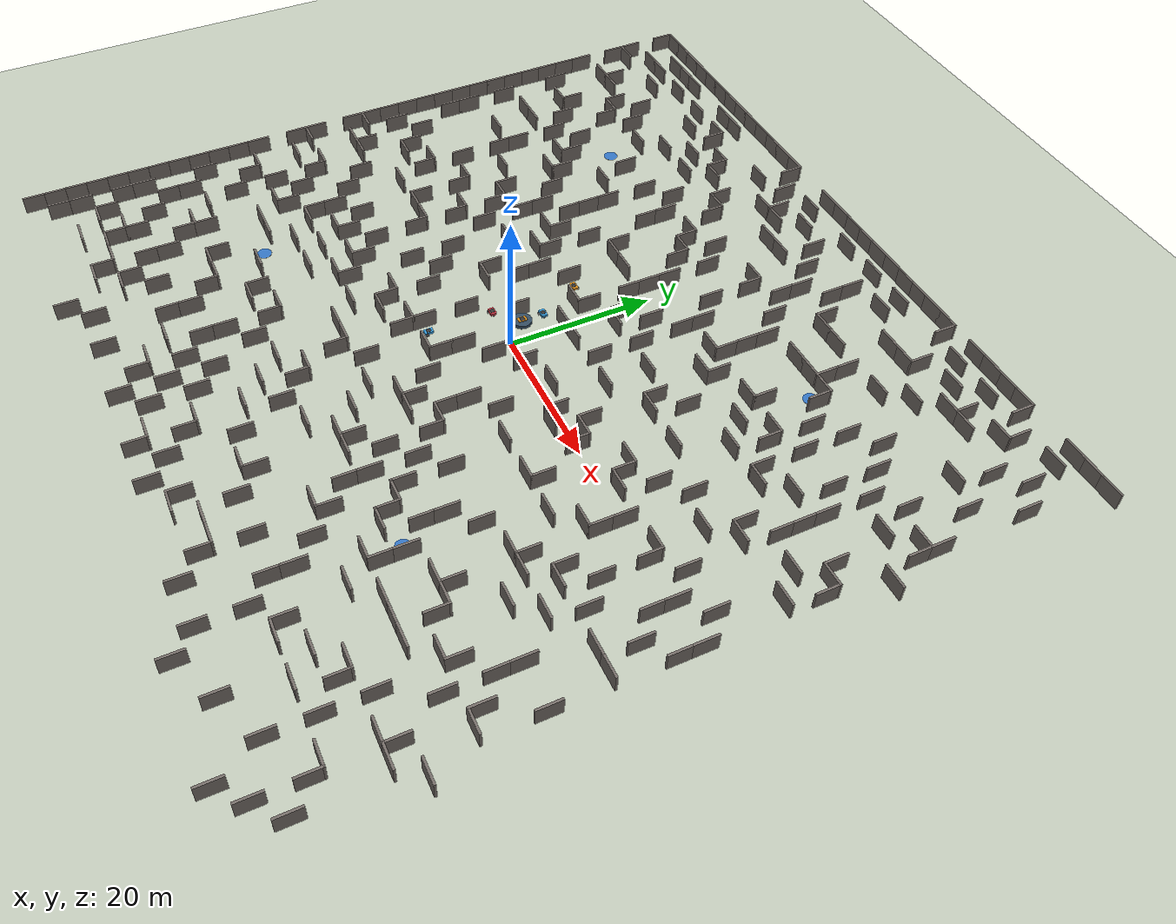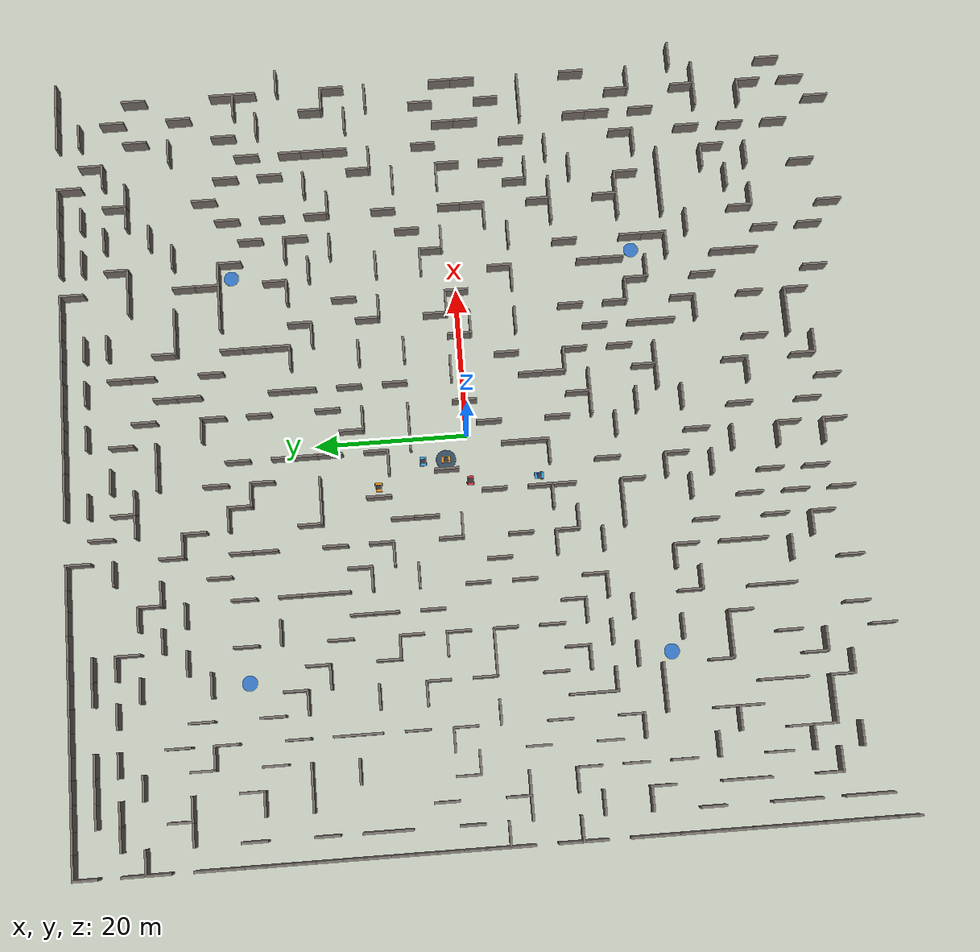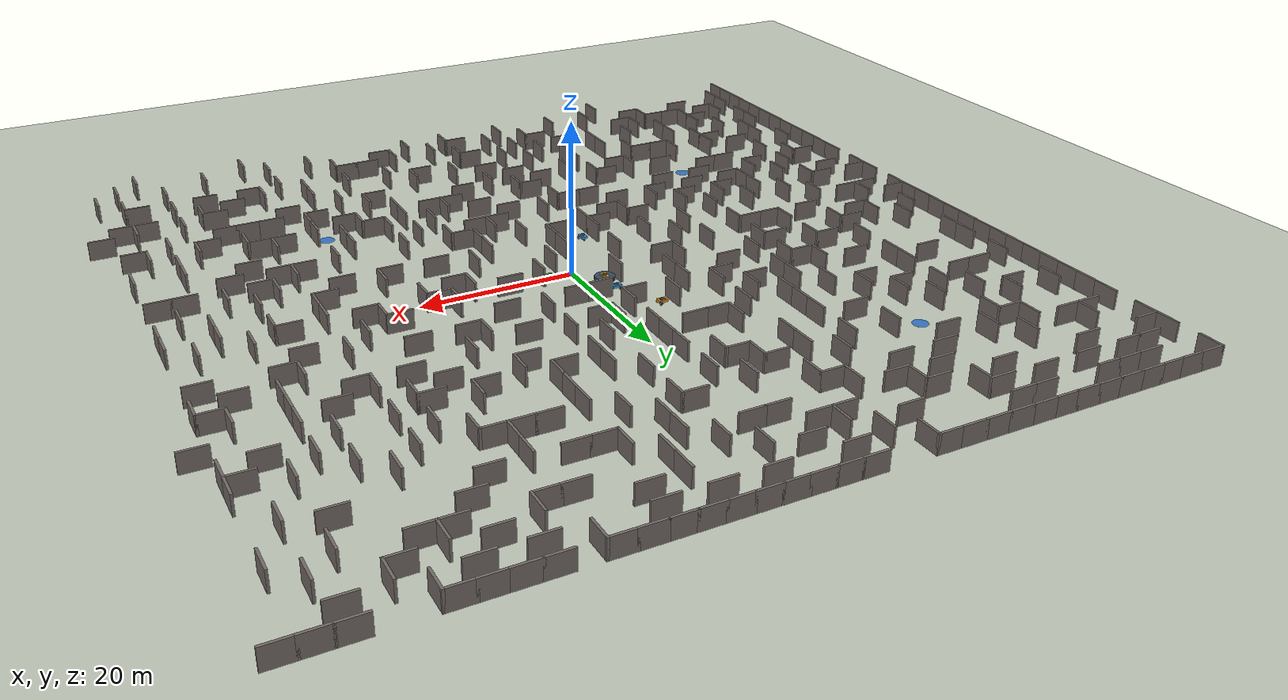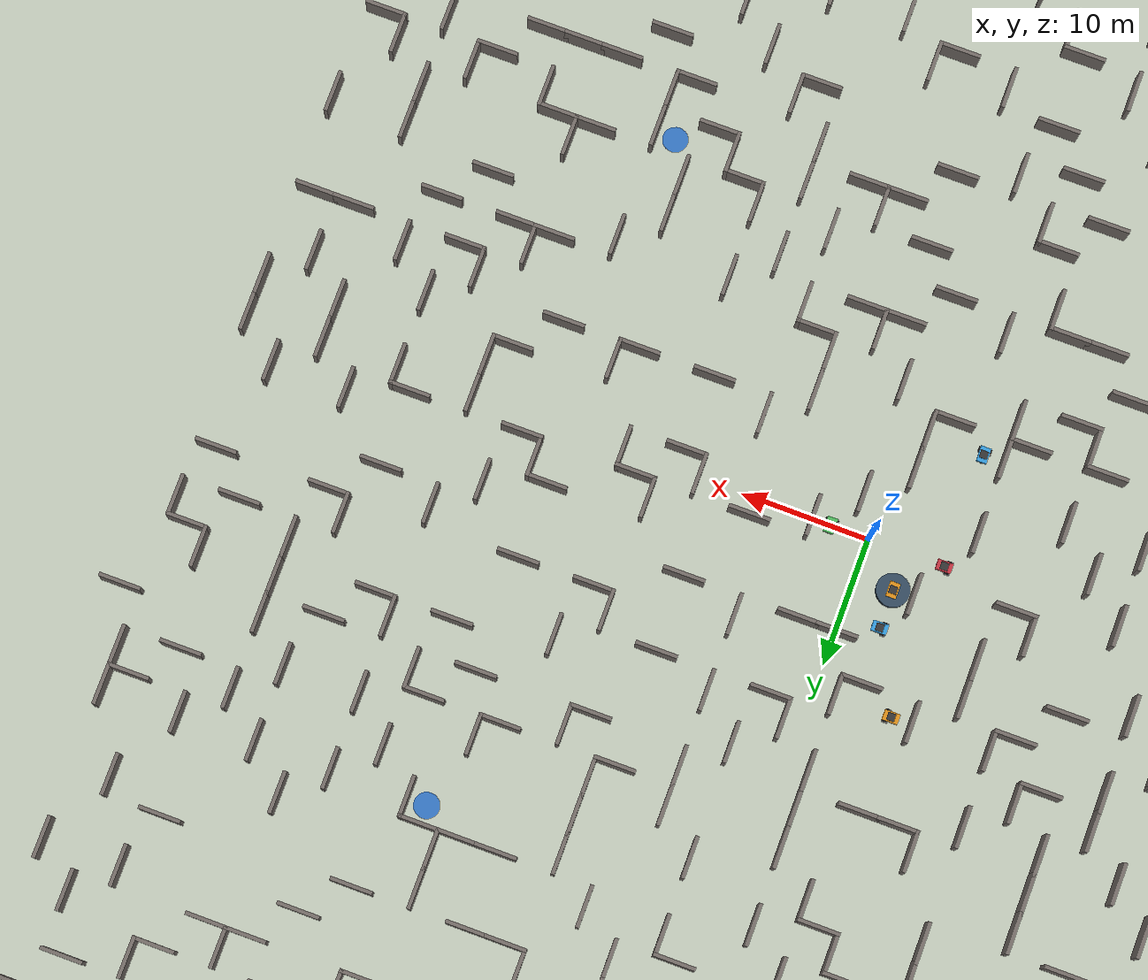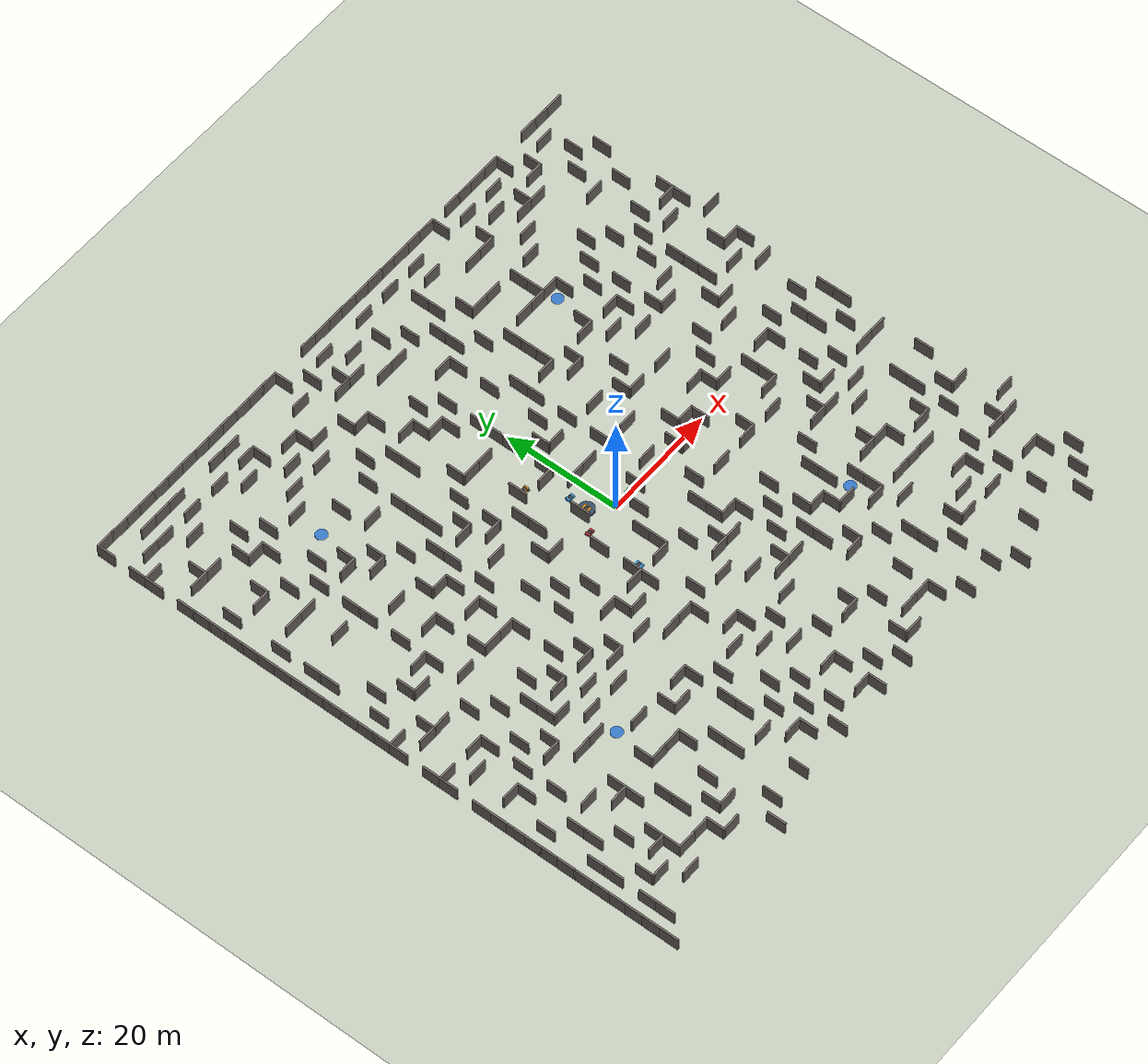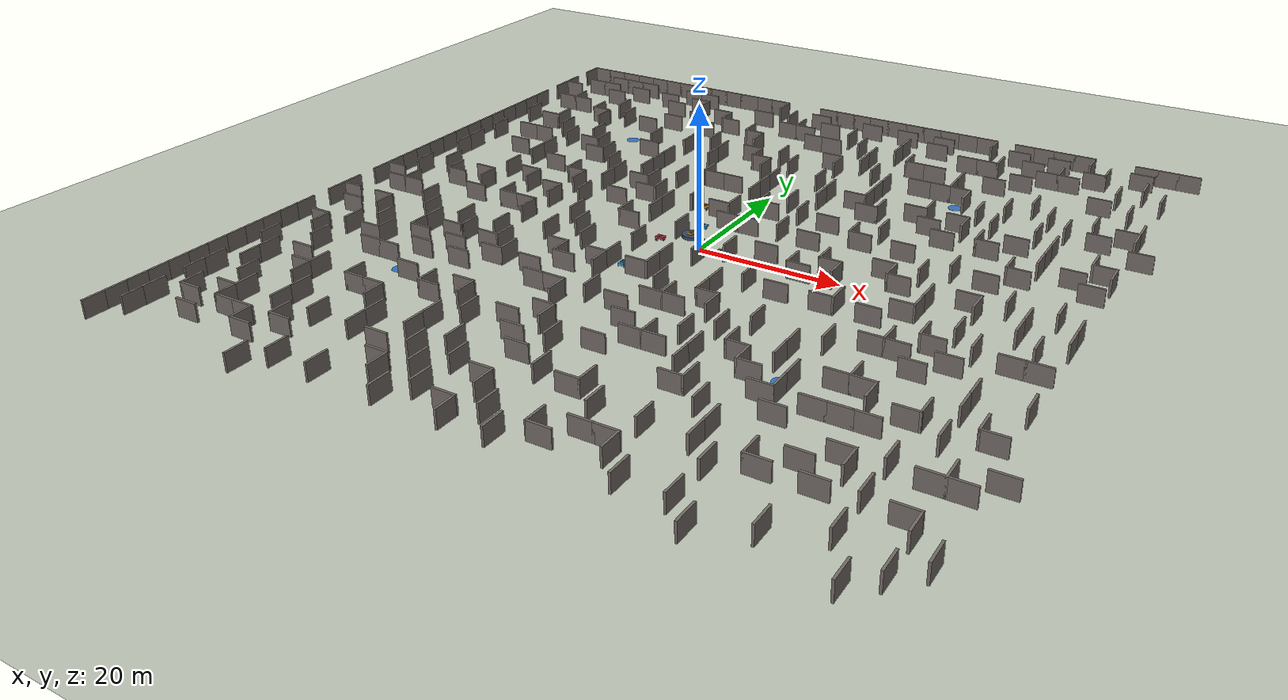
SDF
<sdf version="1.9">
 <world name="swap_world">
  <physics name="4ms" type="ignored">
   <max_step_size>0.004</max_step_size>
   <real_time_factor>1.0</real_time_factor>
  </physics>
  <plugin filename="gz-sim-physics-system" name="gz::sim::systems::Physics"/>
  <plugin filename="gz-sim-scene-broadcaster-system" name="gz::sim::systems::SceneBroadcaster"/>
  <plugin filename="gz-sim-user-commands-system" name="gz::sim::systems::UserCommands"/>
  <wind><linear_velocity>0 0 0</linear_velocity></wind>
  <plugin filename="gz-sim-wind-effects-system" name="gz::sim::systems::WindEffects">
   <force_approximation_scaling_factor>0.1</force_approximation_scaling_factor>
   <horizontal>
    <magnitude><time_for_rise>1.0</time_for_rise></magnitude>
    <direction><time_for_rise>1.0</time_for_rise></direction>
   </horizontal>
  </plugin>
  <light type="directional" name="sun">
   <pose>0 0 10 0 0 0</pose>
   <diffuse>0.8 0.8 0.8 1</diffuse>
   <specular>0.2 0.2 0.2 1</specular>
   <direction>-0.5 0.1 -0.9</direction>
  </light>
  <model name="ground_plane">
   <static>true</static>
   <link name="link">
    <collision name="collision">
     <geometry><plane><normal>0 0 1</normal><size>125 125</size></plane></geometry>
    </collision>
    <visual name="visual">
     <geometry><plane><normal>0 0 1</normal><size>125 125</size></plane></geometry>
     <material><ambient>0.75 0.78 0.72 1</ambient><diffuse>0.75 0.78 0.72 1</diffuse></material>
    </visual>
   </link>
  </model>
  <model name="warehouse">
   <static>true</static>
   <link name="link">
    <pose>-3.00 3.00 0.25 0 0 0</pose>
    <visual name="v">
     <geometry><cylinder><radius>1.3</radius><length>0.5</length></cylinder></geometry>
     <material><ambient>0.2 0.29 0.37 1</ambient><diffuse>0.2 0.29 0.37 1</diffuse></material>
    </visual>
   </link>
  </model>
  <model name="pad_0">
   <static>true</static>
   <link name="link">
    <pose>-30.00 30.00 0.01 0 0 0</pose>
    <visual name="visual">
     <geometry><cylinder><radius>1.0</radius><length>0.02</length></cylinder></geometry>
     <material><ambient>0.2 0.45 0.75 1</ambient><diffuse>0.2 0.45 0.75 1</diffuse></material>
    </visual>
   </link>
  </model>
  <model name="pad_1">
   <static>true</static>
   <link name="link">
    <pose>24.00 30.00 0.01 0 0 0</pose>
    <visual name="visual">
     <geometry><cylinder><radius>1.0</radius><length>0.02</length></cylinder></geometry>
     <material><ambient>0.2 0.45 0.75 1</ambient><diffuse>0.2 0.45 0.75 1</diffuse></material>
    </visual>
   </link>
  </model>
  <model name="pad_2">
   <static>true</static>
   <link name="link">
    <pose>-30.00 -24.00 0.01 0 0 0</pose>
    <visual name="visual">
     <geometry><cylinder><radius>1.0</radius><length>0.02</length></cylinder></geometry>
     <material><ambient>0.2 0.45 0.75 1</ambient><diffuse>0.2 0.45 0.75 1</diffuse></material>
    </visual>
   </link>
  </model>
  <model name="pad_3">
   <static>true</static>
   <link name="link">
    <pose>24.00 -24.00 0.01 0 0 0</pose>
    <visual name="visual">
     <geometry><cylinder><radius>1.0</radius><length>0.02</length></cylinder></geometry>
     <material><ambient>0.2 0.45 0.75 1</ambient><diffuse>0.2 0.45 0.75 1</diffuse></material>
    </visual>
   </link>
  </model>
  <model name="wall_0">
   <static>true</static>
   <link name="l">
    <pose>-52.50 51.00 1.25 0 0 1.5708</pose>
    <collision name="c"><geometry><box><size>3.30 0.3 2.5</size></box></geometry></collision>
    <visual name="v">
     <geometry><box><size>3.30 0.3 2.5</size></box></geometry>
     <material><ambient>0.45 0.42 0.4 1</ambient><diffuse>0.45 0.42 0.4 1</diffuse></material>
    </visual>
   </link>
  </model>
  <model name="wall_1">
   <static>true</static>
   <link name="l">
    <pose>-51.00 52.50 1.25 0 0 0.0000</pose>
    <collision name="c"><geometry><box><size>3.30 0.3 2.5</size></box></geometry></collision>
    <visual name="v">
     <geometry><box><size>3.30 0.3 2.5</size></box></geometry>
     <material><ambient>0.45 0.42 0.4 1</ambient><diffuse>0.45 0.42 0.4 1</diffuse></material>
    </visual>
   </link>
  </model>
  <model name="wall_2">
   <static>true</static>
   <link name="l">
    <pose>-52.50 45.00 1.25 0 0 1.5708</pose>
    <collision name="c"><geometry><box><size>3.30 0.3 2.5</size></box></geometry></collision>
    <visual name="v">
     <geometry><box><size>3.30 0.3 2.5</size></box></geometry>
     <material><ambient>0.45 0.42 0.4 1</ambient><diffuse>0.45 0.42 0.4 1</diffuse></material>
    </visual>
   </link>
  </model>
  <model name="wall_3">
   <static>true</static>
   <link name="l">
    <pose>-52.50 42.00 1.25 0 0 1.5708</pose>
    <collision name="c"><geometry><box><size>3.30 0.3 2.5</size></box></geometry></collision>
    <visual name="v">
     <geometry><box><size>3.30 0.3 2.5</size></box></geometry>
     <material><ambient>0.45 0.42 0.4 1</ambient><diffuse>0.45 0.42 0.4 1</diffuse></material>
    </visual>
   </link>
  </model>
  <model name="wall_4">
   <static>true</static>
   <link name="l">
    <pose>-51.00 43.50 1.25 0 0 0.0000</pose>
    <collision name="c"><geometry><box><size>3.30 0.3 2.5</size></box></geometry></collision>
    <visual name="v">
     <geometry><box><size>3.30 0.3 2.5</size></box></geometry>
     <material><ambient>0.45 0.42 0.4 1</ambient><diffuse>0.45 0.42 0.4 1</diffuse></material>
    </visual>
   </link>
  </model>
  <model name="wall_5">
   <static>true</static>
   <link name="l">
    <pose>-52.50 36.00 1.25 0 0 1.5708</pose>
    <collision name="c"><geometry><box><size>3.30 0.3 2.5</size></box></geometry></collision>
    <visual name="v">
     <geometry><box><size>3.30 0.3 2.5</size></box></geometry>
     <material><ambient>0.45 0.42 0.4 1</ambient><diffuse>0.45 0.42 0.4 1</diffuse></material>
    </visual>
   </link>
  </model>
  <model name="wall_6">
   <static>true</static>
   <link name="l">
    <pose>-52.50 33.00 1.25 0 0 1.5708</pose>
    <collision name="c"><geometry><box><size>3.30 0.3 2.5</size></box></geometry></collision>
    <visual name="v">
     <geometry><box><size>3.30 0.3 2.5</size></box></geometry>
     <material><ambient>0.45 0.42 0.4 1</ambient><diffuse>0.45 0.42 0.4 1</diffuse></material>
    </visual>
   </link>
  </model>
  <model name="wall_7">
   <static>true</static>
   <link name="l">
    <pose>-49.50 30.00 1.25 0 0 1.5708</pose>
    <collision name="c"><geometry><box><size>3.30 0.3 2.5</size></box></geometry></collision>
    <visual name="v">
     <geometry><box><size>3.30 0.3 2.5</size></box></geometry>
     <material><ambient>0.45 0.42 0.4 1</ambient><diffuse>0.45 0.42 0.4 1</diffuse></material>
    </visual>
   </link>
  </model>
  <model name="wall_8">
   <static>true</static>
   <link name="l">
    <pose>-52.50 30.00 1.25 0 0 1.5708</pose>
    <collision name="c"><geometry><box><size>3.30 0.3 2.5</size></box></geometry></collision>
    <visual name="v">
     <geometry><box><size>3.30 0.3 2.5</size></box></geometry>
     <material><ambient>0.45 0.42 0.4 1</ambient><diffuse>0.45 0.42 0.4 1</diffuse></material>
    </visual>
   </link>
  </model>
  <model name="wall_9">
   <static>true</static>
   <link name="l">
    <pose>-52.50 27.00 1.25 0 0 1.5708</pose>
    <collision name="c"><geometry><box><size>3.30 0.3 2.5</size></box></geometry></collision>
    <visual name="v">
     <geometry><box><size>3.30 0.3 2.5</size></box></geometry>
     <material><ambient>0.45 0.42 0.4 1</ambient><diffuse>0.45 0.42 0.4 1</diffuse></material>
    </visual>
   </link>
  </model>
  <model name="wall_10">
   <static>true</static>
   <link name="l">
    <pose>-52.50 24.00 1.25 0 0 1.5708</pose>
    <collision name="c"><geometry><box><size>3.30 0.3 2.5</size></box></geometry></collision>
    <visual name="v">
     <geometry><box><size>3.30 0.3 2.5</size></box></geometry>
     <material><ambient>0.45 0.42 0.4 1</ambient><diffuse>0.45 0.42 0.4 1</diffuse></material>
    </visual>
   </link>
  </model>
  <model name="wall_11">
   <static>true</static>
   <link name="l">
    <pose>-49.50 21.00 1.25 0 0 1.5708</pose>
    <collision name="c"><geometry><box><size>3.30 0.3 2.5</size></box></geometry></collision>
    <visual name="v">
     <geometry><box><size>3.30 0.3 2.5</size></box></geometry>
     <material><ambient>0.45 0.42 0.4 1</ambient><diffuse>0.45 0.42 0.4 1</diffuse></material>
    </visual>
   </link>
  </model>
  <model name="wall_12">
   <static>true</static>
   <link name="l">
    <pose>-52.50 21.00 1.25 0 0 1.5708</pose>
    <collision name="c"><geometry><box><size>3.30 0.3 2.5</size></box></geometry></collision>
    <visual name="v">
     <geometry><box><size>3.30 0.3 2.5</size></box></geometry>
     <material><ambient>0.45 0.42 0.4 1</ambient><diffuse>0.45 0.42 0.4 1</diffuse></material>
    </visual>
   </link>
  </model>
  <model name="wall_13">
   <static>true</static>
   <link name="l">
    <pose>-52.50 18.00 1.25 0 0 1.5708</pose>
    <collision name="c"><geometry><box><size>3.30 0.3 2.5</size></box></geometry></collision>
    <visual name="v">
     <geometry><box><size>3.30 0.3 2.5</size></box></geometry>
     <material><ambient>0.45 0.42 0.4 1</ambient><diffuse>0.45 0.42 0.4 1</diffuse></material>
    </visual>
   </link>
  </model>
  <model name="wall_14">
   <static>true</static>
   <link name="l">
    <pose>-49.50 15.00 1.25 0 0 1.5708</pose>
    <collision name="c"><geometry><box><size>3.30 0.3 2.5</size></box></geometry></collision>
    <visual name="v">
     <geometry><box><size>3.30 0.3 2.5</size></box></geometry>
     <material><ambient>0.45 0.42 0.4 1</ambient><diffuse>0.45 0.42 0.4 1</diffuse></material>
    </visual>
   </link>
  </model>
  <model name="wall_15">
   <static>true</static>
   <link name="l">
    <pose>-52.50 15.00 1.25 0 0 1.5708</pose>
    <collision name="c"><geometry><box><size>3.30 0.3 2.5</size></box></geometry></collision>
    <visual name="v">
     <geometry><box><size>3.30 0.3 2.5</size></box></geometry>
     <material><ambient>0.45 0.42 0.4 1</ambient><diffuse>0.45 0.42 0.4 1</diffuse></material>
    </visual>
   </link>
  </model>
  <model name="wall_16">
   <static>true</static>
   <link name="l">
    <pose>-49.50 12.00 1.25 0 0 1.5708</pose>
    <collision name="c"><geometry><box><size>3.30 0.3 2.5</size></box></geometry></collision>
    <visual name="v">
     <geometry><box><size>3.30 0.3 2.5</size></box></geometry>
     <material><ambient>0.45 0.42 0.4 1</ambient><diffuse>0.45 0.42 0.4 1</diffuse></material>
    </visual>
   </link>
  </model>
  <model name="wall_17">
   <static>true</static>
   <link name="l">
    <pose>-52.50 12.00 1.25 0 0 1.5708</pose>
    <collision name="c"><geometry><box><size>3.30 0.3 2.5</size></box></geometry></collision>
    <visual name="v">
     <geometry><box><size>3.30 0.3 2.5</size></box></geometry>
     <material><ambient>0.45 0.42 0.4 1</ambient><diffuse>0.45 0.42 0.4 1</diffuse></material>
    </visual>
   </link>
  </model>
  <model name="wall_18">
   <static>true</static>
   <link name="l">
    <pose>-52.50 9.00 1.25 0 0 1.5708</pose>
    <collision name="c"><geometry><box><size>3.30 0.3 2.5</size></box></geometry></collision>
    <visual name="v">
     <geometry><box><size>3.30 0.3 2.5</size></box></geometry>
     <material><ambient>0.45 0.42 0.4 1</ambient><diffuse>0.45 0.42 0.4 1</diffuse></material>
    </visual>
   </link>
  </model>
  <model name="wall_19">
   <static>true</static>
   <link name="l">
    <pose>-52.50 6.00 1.25 0 0 1.5708</pose>
    <collision name="c"><geometry><box><size>3.30 0.3 2.5</size></box></geometry></collision>
    <visual name="v">
     <geometry><box><size>3.30 0.3 2.5</size></box></geometry>
     <material><ambient>0.45 0.42 0.4 1</ambient><diffuse>0.45 0.42 0.4 1</diffuse></material>
    </visual>
   </link>
  </model>
  <model name="wall_20">
   <static>true</static>
   <link name="l">
    <pose>-49.50 3.00 1.25 0 0 1.5708</pose>
    <collision name="c"><geometry><box><size>3.30 0.3 2.5</size></box></geometry></collision>
    <visual name="v">
     <geometry><box><size>3.30 0.3 2.5</size></box></geometry>
     <material><ambient>0.45 0.42 0.4 1</ambient><diffuse>0.45 0.42 0.4 1</diffuse></material>
    </visual>
   </link>
  </model>
  <model name="wall_21">
   <static>true</static>
   <link name="l">
    <pose>-52.50 3.00 1.25 0 0 1.5708</pose>
    <collision name="c"><geometry><box><size>3.30 0.3 2.5</size></box></geometry></collision>
    <visual name="v">
     <geometry><box><size>3.30 0.3 2.5</size></box></geometry>
     <material><ambient>0.45 0.42 0.4 1</ambient><diffuse>0.45 0.42 0.4 1</diffuse></material>
    </visual>
   </link>
  </model>
  <model name="wall_22">
   <static>true</static>
   <link name="l">
    <pose>-52.50 -0.00 1.25 0 0 1.5708</pose>
    <collision name="c"><geometry><box><size>3.30 0.3 2.5</size></box></geometry></collision>
    <visual name="v">
     <geometry><box><size>3.30 0.3 2.5</size></box></geometry>
     <material><ambient>0.45 0.42 0.4 1</ambient><diffuse>0.45 0.42 0.4 1</diffuse></material>
    </visual>
   </link>
  </model>
  <model name="wall_23">
   <static>true</static>
   <link name="l">
    <pose>-52.50 -3.00 1.25 0 0 1.5708</pose>
    <collision name="c"><geometry><box><size>3.30 0.3 2.5</size></box></geometry></collision>
    <visual name="v">
     <geometry><box><size>3.30 0.3 2.5</size></box></geometry>
     <material><ambient>0.45 0.42 0.4 1</ambient><diffuse>0.45 0.42 0.4 1</diffuse></material>
    </visual>
   </link>
  </model>
  <model name="wall_24">
   <static>true</static>
   <link name="l">
    <pose>-51.00 -1.50 1.25 0 0 0.0000</pose>
    <collision name="c"><geometry><box><size>3.30 0.3 2.5</size></box></geometry></collision>
    <visual name="v">
     <geometry><box><size>3.30 0.3 2.5</size></box></geometry>
     <material><ambient>0.45 0.42 0.4 1</ambient><diffuse>0.45 0.42 0.4 1</diffuse></material>
    </visual>
   </link>
  </model>
  <model name="wall_25">
   <static>true</static>
   <link name="l">
    <pose>-52.50 -9.00 1.25 0 0 1.5708</pose>
    <collision name="c"><geometry><box><size>3.30 0.3 2.5</size></box></geometry></collision>
    <visual name="v">
     <geometry><box><size>3.30 0.3 2.5</size></box></geometry>
     <material><ambient>0.45 0.42 0.4 1</ambient><diffuse>0.45 0.42 0.4 1</diffuse></material>
    </visual>
   </link>
  </model>
  <model name="wall_26">
   <static>true</static>
   <link name="l">
    <pose>-52.50 -12.00 1.25 0 0 1.5708</pose>
    <collision name="c"><geometry><box><size>3.30 0.3 2.5</size></box></geometry></collision>
    <visual name="v">
     <geometry><box><size>3.30 0.3 2.5</size></box></geometry>
     <material><ambient>0.45 0.42 0.4 1</ambient><diffuse>0.45 0.42 0.4 1</diffuse></material>
    </visual>
   </link>
  </model>
  <model name="wall_27">
   <static>true</static>
   <link name="l">
    <pose>-51.00 -10.50 1.25 0 0 0.0000</pose>
    <collision name="c"><geometry><box><size>3.30 0.3 2.5</size></box></geometry></collision>
    <visual name="v">
     <geometry><box><size>3.30 0.3 2.5</size></box></geometry>
     <material><ambient>0.45 0.42 0.4 1</ambient><diffuse>0.45 0.42 0.4 1</diffuse></material>
    </visual>
   </link>
  </model>
  <model name="wall_28">
   <static>true</static>
   <link name="l">
    <pose>-52.50 -18.00 1.25 0 0 1.5708</pose>
    <collision name="c"><geometry><box><size>3.30 0.3 2.5</size></box></geometry></collision>
    <visual name="v">
     <geometry><box><size>3.30 0.3 2.5</size></box></geometry>
     <material><ambient>0.45 0.42 0.4 1</ambient><diffuse>0.45 0.42 0.4 1</diffuse></material>
    </visual>
   </link>
  </model>
  <model name="wall_29">
   <static>true</static>
   <link name="l">
    <pose>-52.50 -21.00 1.25 0 0 1.5708</pose>
    <collision name="c"><geometry><box><size>3.30 0.3 2.5</size></box></geometry></collision>
    <visual name="v">
     <geometry><box><size>3.30 0.3 2.5</size></box></geometry>
     <material><ambient>0.45 0.42 0.4 1</ambient><diffuse>0.45 0.42 0.4 1</diffuse></material>
    </visual>
   </link>
  </model>
  <model name="wall_30">
   <static>true</static>
   <link name="l">
    <pose>-52.50 -24.00 1.25 0 0 1.5708</pose>
    <collision name="c"><geometry><box><size>3.30 0.3 2.5</size></box></geometry></collision>
    <visual name="v">
     <geometry><box><size>3.30 0.3 2.5</size></box></geometry>
     <material><ambient>0.45 0.42 0.4 1</ambient><diffuse>0.45 0.42 0.4 1</diffuse></material>
    </visual>
   </link>
  </model>
  <model name="wall_31">
   <static>true</static>
   <link name="l">
    <pose>-49.50 -27.00 1.25 0 0 1.5708</pose>
    <collision name="c"><geometry><box><size>3.30 0.3 2.5</size></box></geometry></collision>
    <visual name="v">
     <geometry><box><size>3.30 0.3 2.5</size></box></geometry>
     <material><ambient>0.45 0.42 0.4 1</ambient><diffuse>0.45 0.42 0.4 1</diffuse></material>
    </visual>
   </link>
  </model>
  <model name="wall_32">
   <static>true</static>
   <link name="l">
    <pose>-52.50 -27.00 1.25 0 0 1.5708</pose>
    <collision name="c"><geometry><box><size>3.30 0.3 2.5</size></box></geometry></collision>
    <visual name="v">
     <geometry><box><size>3.30 0.3 2.5</size></box></geometry>
     <material><ambient>0.45 0.42 0.4 1</ambient><diffuse>0.45 0.42 0.4 1</diffuse></material>
    </visual>
   </link>
  </model>
  <model name="wall_33">
   <static>true</static>
   <link name="l">
    <pose>-52.50 -30.00 1.25 0 0 1.5708</pose>
    <collision name="c"><geometry><box><size>3.30 0.3 2.5</size></box></geometry></collision>
    <visual name="v">
     <geometry><box><size>3.30 0.3 2.5</size></box></geometry>
     <material><ambient>0.45 0.42 0.4 1</ambient><diffuse>0.45 0.42 0.4 1</diffuse></material>
    </visual>
   </link>
  </model>
  <model name="wall_34">
   <static>true</static>
   <link name="l">
    <pose>-52.50 -33.00 1.25 0 0 1.5708</pose>
    <collision name="c"><geometry><box><size>3.30 0.3 2.5</size></box></geometry></collision>
    <visual name="v">
     <geometry><box><size>3.30 0.3 2.5</size></box></geometry>
     <material><ambient>0.45 0.42 0.4 1</ambient><diffuse>0.45 0.42 0.4 1</diffuse></material>
    </visual>
   </link>
  </model>
  <model name="wall_35">
   <static>true</static>
   <link name="l">
    <pose>-49.50 -36.00 1.25 0 0 1.5708</pose>
    <collision name="c"><geometry><box><size>3.30 0.3 2.5</size></box></geometry></collision>
    <visual name="v">
     <geometry><box><size>3.30 0.3 2.5</size></box></geometry>
     <material><ambient>0.45 0.42 0.4 1</ambient><diffuse>0.45 0.42 0.4 1</diffuse></material>
    </visual>
   </link>
  </model>
  <model name="wall_36">
   <static>true</static>
   <link name="l">
    <pose>-52.50 -36.00 1.25 0 0 1.5708</pose>
    <collision name="c"><geometry><box><size>3.30 0.3 2.5</size></box></geometry></collision>
    <visual name="v">
     <geometry><box><size>3.30 0.3 2.5</size></box></geometry>
     <material><ambient>0.45 0.42 0.4 1</ambient><diffuse>0.45 0.42 0.4 1</diffuse></material>
    </visual>
   </link>
  </model>
  <model name="wall_37">
   <static>true</static>
   <link name="l">
    <pose>-49.50 -39.00 1.25 0 0 1.5708</pose>
    <collision name="c"><geometry><box><size>3.30 0.3 2.5</size></box></geometry></collision>
    <visual name="v">
     <geometry><box><size>3.30 0.3 2.5</size></box></geometry>
     <material><ambient>0.45 0.42 0.4 1</ambient><diffuse>0.45 0.42 0.4 1</diffuse></material>
    </visual>
   </link>
  </model>
  <model name="wall_38">
   <static>true</static>
   <link name="l">
    <pose>-52.50 -39.00 1.25 0 0 1.5708</pose>
    <collision name="c"><geometry><box><size>3.30 0.3 2.5</size></box></geometry></collision>
    <visual name="v">
     <geometry><box><size>3.30 0.3 2.5</size></box></geometry>
     <material><ambient>0.45 0.42 0.4 1</ambient><diffuse>0.45 0.42 0.4 1</diffuse></material>
    </visual>
   </link>
  </model>
  <model name="wall_39">
   <static>true</static>
   <link name="l">
    <pose>-52.50 -42.00 1.25 0 0 1.5708</pose>
    <collision name="c"><geometry><box><size>3.30 0.3 2.5</size></box></geometry></collision>
    <visual name="v">
     <geometry><box><size>3.30 0.3 2.5</size></box></geometry>
     <material><ambient>0.45 0.42 0.4 1</ambient><diffuse>0.45 0.42 0.4 1</diffuse></material>
    </visual>
   </link>
  </model>
  <model name="wall_40">
   <static>true</static>
   <link name="l">
    <pose>-49.50 -45.00 1.25 0 0 1.5708</pose>
    <collision name="c"><geometry><box><size>3.30 0.3 2.5</size></box></geometry></collision>
    <visual name="v">
     <geometry><box><size>3.30 0.3 2.5</size></box></geometry>
     <material><ambient>0.45 0.42 0.4 1</ambient><diffuse>0.45 0.42 0.4 1</diffuse></material>
    </visual>
   </link>
  </model>
  <model name="wall_41">
   <static>true</static>
   <link name="l">
    <pose>-52.50 -45.00 1.25 0 0 1.5708</pose>
    <collision name="c"><geometry><box><size>3.30 0.3 2.5</size></box></geometry></collision>
    <visual name="v">
     <geometry><box><size>3.30 0.3 2.5</size></box></geometry>
     <material><ambient>0.45 0.42 0.4 1</ambient><diffuse>0.45 0.42 0.4 1</diffuse></material>
    </visual>
   </link>
  </model>
  <model name="wall_42">
   <static>true</static>
   <link name="l">
    <pose>-49.50 -48.00 1.25 0 0 1.5708</pose>
    <collision name="c"><geometry><box><size>3.30 0.3 2.5</size></box></geometry></collision>
    <visual name="v">
     <geometry><box><size>3.30 0.3 2.5</size></box></geometry>
     <material><ambient>0.45 0.42 0.4 1</ambient><diffuse>0.45 0.42 0.4 1</diffuse></material>
    </visual>
   </link>
  </model>
  <model name="wall_43">
   <static>true</static>
   <link name="l">
    <pose>-52.50 -48.00 1.25 0 0 1.5708</pose>
    <collision name="c"><geometry><box><size>3.30 0.3 2.5</size></box></geometry></collision>
    <visual name="v">
     <geometry><box><size>3.30 0.3 2.5</size></box></geometry>
     <material><ambient>0.45 0.42 0.4 1</ambient><diffuse>0.45 0.42 0.4 1</diffuse></material>
    </visual>
   </link>
  </model>
  <model name="wall_44">
   <static>true</static>
   <link name="l">
    <pose>-52.50 -51.00 1.25 0 0 1.5708</pose>
    <collision name="c"><geometry><box><size>3.30 0.3 2.5</size></box></geometry></collision>
    <visual name="v">
     <geometry><box><size>3.30 0.3 2.5</size></box></geometry>
     <material><ambient>0.45 0.42 0.4 1</ambient><diffuse>0.45 0.42 0.4 1</diffuse></material>
    </visual>
   </link>
  </model>
  <model name="wall_45">
   <static>true</static>
   <link name="l">
    <pose>-48.00 52.50 1.25 0 0 0.0000</pose>
    <collision name="c"><geometry><box><size>3.30 0.3 2.5</size></box></geometry></collision>
    <visual name="v">
     <geometry><box><size>3.30 0.3 2.5</size></box></geometry>
     <material><ambient>0.45 0.42 0.4 1</ambient><diffuse>0.45 0.42 0.4 1</diffuse></material>
    </visual>
   </link>
  </model>
  <model name="wall_46">
   <static>true</static>
   <link name="l">
    <pose>-48.00 46.50 1.25 0 0 0.0000</pose>
    <collision name="c"><geometry><box><size>3.30 0.3 2.5</size></box></geometry></collision>
    <visual name="v">
     <geometry><box><size>3.30 0.3 2.5</size></box></geometry>
     <material><ambient>0.45 0.42 0.4 1</ambient><diffuse>0.45 0.42 0.4 1</diffuse></material>
    </visual>
   </link>
  </model>
  <model name="wall_47">
   <static>true</static>
   <link name="l">
    <pose>-46.50 39.00 1.25 0 0 1.5708</pose>
    <collision name="c"><geometry><box><size>3.30 0.3 2.5</size></box></geometry></collision>
    <visual name="v">
     <geometry><box><size>3.30 0.3 2.5</size></box></geometry>
     <material><ambient>0.45 0.42 0.4 1</ambient><diffuse>0.45 0.42 0.4 1</diffuse></material>
    </visual>
   </link>
  </model>
  <model name="wall_48">
   <static>true</static>
   <link name="l">
    <pose>-48.00 37.50 1.25 0 0 0.0000</pose>
    <collision name="c"><geometry><box><size>3.30 0.3 2.5</size></box></geometry></collision>
    <visual name="v">
     <geometry><box><size>3.30 0.3 2.5</size></box></geometry>
     <material><ambient>0.45 0.42 0.4 1</ambient><diffuse>0.45 0.42 0.4 1</diffuse></material>
    </visual>
   </link>
  </model>
  <model name="wall_49">
   <static>true</static>
   <link name="l">
    <pose>-46.50 6.00 1.25 0 0 1.5708</pose>
    <collision name="c"><geometry><box><size>3.30 0.3 2.5</size></box></geometry></collision>
    <visual name="v">
     <geometry><box><size>3.30 0.3 2.5</size></box></geometry>
     <material><ambient>0.45 0.42 0.4 1</ambient><diffuse>0.45 0.42 0.4 1</diffuse></material>
    </visual>
   </link>
  </model>
  <model name="wall_50">
   <static>true</static>
   <link name="l">
    <pose>-46.50 -3.00 1.25 0 0 1.5708</pose>
    <collision name="c"><geometry><box><size>3.30 0.3 2.5</size></box></geometry></collision>
    <visual name="v">
     <geometry><box><size>3.30 0.3 2.5</size></box></geometry>
     <material><ambient>0.45 0.42 0.4 1</ambient><diffuse>0.45 0.42 0.4 1</diffuse></material>
    </visual>
   </link>
  </model>
  <model name="wall_51">
   <static>true</static>
   <link name="l">
    <pose>-48.00 -4.50 1.25 0 0 0.0000</pose>
    <collision name="c"><geometry><box><size>3.30 0.3 2.5</size></box></geometry></collision>
    <visual name="v">
     <geometry><box><size>3.30 0.3 2.5</size></box></geometry>
     <material><ambient>0.45 0.42 0.4 1</ambient><diffuse>0.45 0.42 0.4 1</diffuse></material>
    </visual>
   </link>
  </model>
  <model name="wall_52">
   <static>true</static>
   <link name="l">
    <pose>-48.00 -13.50 1.25 0 0 0.0000</pose>
    <collision name="c"><geometry><box><size>3.30 0.3 2.5</size></box></geometry></collision>
    <visual name="v">
     <geometry><box><size>3.30 0.3 2.5</size></box></geometry>
     <material><ambient>0.45 0.42 0.4 1</ambient><diffuse>0.45 0.42 0.4 1</diffuse></material>
    </visual>
   </link>
  </model>
  <model name="wall_53">
   <static>true</static>
   <link name="l">
    <pose>-46.50 -21.00 1.25 0 0 1.5708</pose>
    <collision name="c"><geometry><box><size>3.30 0.3 2.5</size></box></geometry></collision>
    <visual name="v">
     <geometry><box><size>3.30 0.3 2.5</size></box></geometry>
     <material><ambient>0.45 0.42 0.4 1</ambient><diffuse>0.45 0.42 0.4 1</diffuse></material>
    </visual>
   </link>
  </model>
  <model name="wall_54">
   <static>true</static>
   <link name="l">
    <pose>-48.00 -19.50 1.25 0 0 0.0000</pose>
    <collision name="c"><geometry><box><size>3.30 0.3 2.5</size></box></geometry></collision>
    <visual name="v">
     <geometry><box><size>3.30 0.3 2.5</size></box></geometry>
     <material><ambient>0.45 0.42 0.4 1</ambient><diffuse>0.45 0.42 0.4 1</diffuse></material>
    </visual>
   </link>
  </model>
  <model name="wall_55">
   <static>true</static>
   <link name="l">
    <pose>-46.50 -30.00 1.25 0 0 1.5708</pose>
    <collision name="c"><geometry><box><size>3.30 0.3 2.5</size></box></geometry></collision>
    <visual name="v">
     <geometry><box><size>3.30 0.3 2.5</size></box></geometry>
     <material><ambient>0.45 0.42 0.4 1</ambient><diffuse>0.45 0.42 0.4 1</diffuse></material>
    </visual>
   </link>
  </model>
  <model name="wall_56">
   <static>true</static>
   <link name="l">
    <pose>-46.50 -33.00 1.25 0 0 1.5708</pose>
    <collision name="c"><geometry><box><size>3.30 0.3 2.5</size></box></geometry></collision>
    <visual name="v">
     <geometry><box><size>3.30 0.3 2.5</size></box></geometry>
     <material><ambient>0.45 0.42 0.4 1</ambient><diffuse>0.45 0.42 0.4 1</diffuse></material>
    </visual>
   </link>
  </model>
  <model name="wall_57">
   <static>true</static>
   <link name="l">
    <pose>-46.50 -42.00 1.25 0 0 1.5708</pose>
    <collision name="c"><geometry><box><size>3.30 0.3 2.5</size></box></geometry></collision>
    <visual name="v">
     <geometry><box><size>3.30 0.3 2.5</size></box></geometry>
     <material><ambient>0.45 0.42 0.4 1</ambient><diffuse>0.45 0.42 0.4 1</diffuse></material>
    </visual>
   </link>
  </model>
  <model name="wall_58">
   <static>true</static>
   <link name="l">
    <pose>-45.00 52.50 1.25 0 0 0.0000</pose>
    <collision name="c"><geometry><box><size>3.30 0.3 2.5</size></box></geometry></collision>
    <visual name="v">
     <geometry><box><size>3.30 0.3 2.5</size></box></geometry>
     <material><ambient>0.45 0.42 0.4 1</ambient><diffuse>0.45 0.42 0.4 1</diffuse></material>
    </visual>
   </link>
  </model>
  <model name="wall_59">
   <static>true</static>
   <link name="l">
    <pose>-45.00 49.50 1.25 0 0 0.0000</pose>
    <collision name="c"><geometry><box><size>3.30 0.3 2.5</size></box></geometry></collision>
    <visual name="v">
     <geometry><box><size>3.30 0.3 2.5</size></box></geometry>
     <material><ambient>0.45 0.42 0.4 1</ambient><diffuse>0.45 0.42 0.4 1</diffuse></material>
    </visual>
   </link>
  </model>
  <model name="wall_60">
   <static>true</static>
   <link name="l">
    <pose>-45.00 46.50 1.25 0 0 0.0000</pose>
    <collision name="c"><geometry><box><size>3.30 0.3 2.5</size></box></geometry></collision>
    <visual name="v">
     <geometry><box><size>3.30 0.3 2.5</size></box></geometry>
     <material><ambient>0.45 0.42 0.4 1</ambient><diffuse>0.45 0.42 0.4 1</diffuse></material>
    </visual>
   </link>
  </model>
  <model name="wall_61">
   <static>true</static>
   <link name="l">
    <pose>-45.00 37.50 1.25 0 0 0.0000</pose>
    <collision name="c"><geometry><box><size>3.30 0.3 2.5</size></box></geometry></collision>
    <visual name="v">
     <geometry><box><size>3.30 0.3 2.5</size></box></geometry>
     <material><ambient>0.45 0.42 0.4 1</ambient><diffuse>0.45 0.42 0.4 1</diffuse></material>
    </visual>
   </link>
  </model>
  <model name="wall_62">
   <static>true</static>
   <link name="l">
    <pose>-43.50 30.00 1.25 0 0 1.5708</pose>
    <collision name="c"><geometry><box><size>3.30 0.3 2.5</size></box></geometry></collision>
    <visual name="v">
     <geometry><box><size>3.30 0.3 2.5</size></box></geometry>
     <material><ambient>0.45 0.42 0.4 1</ambient><diffuse>0.45 0.42 0.4 1</diffuse></material>
    </visual>
   </link>
  </model>
  <model name="wall_63">
   <static>true</static>
   <link name="l">
    <pose>-45.00 28.50 1.25 0 0 0.0000</pose>
    <collision name="c"><geometry><box><size>3.30 0.3 2.5</size></box></geometry></collision>
    <visual name="v">
     <geometry><box><size>3.30 0.3 2.5</size></box></geometry>
     <material><ambient>0.45 0.42 0.4 1</ambient><diffuse>0.45 0.42 0.4 1</diffuse></material>
    </visual>
   </link>
  </model>
  <model name="wall_64">
   <static>true</static>
   <link name="l">
    <pose>-45.00 22.50 1.25 0 0 0.0000</pose>
    <collision name="c"><geometry><box><size>3.30 0.3 2.5</size></box></geometry></collision>
    <visual name="v">
     <geometry><box><size>3.30 0.3 2.5</size></box></geometry>
     <material><ambient>0.45 0.42 0.4 1</ambient><diffuse>0.45 0.42 0.4 1</diffuse></material>
    </visual>
   </link>
  </model>
  <model name="wall_65">
   <static>true</static>
   <link name="l">
    <pose>-43.50 3.00 1.25 0 0 1.5708</pose>
    <collision name="c"><geometry><box><size>3.30 0.3 2.5</size></box></geometry></collision>
    <visual name="v">
     <geometry><box><size>3.30 0.3 2.5</size></box></geometry>
     <material><ambient>0.45 0.42 0.4 1</ambient><diffuse>0.45 0.42 0.4 1</diffuse></material>
    </visual>
   </link>
  </model>
  <model name="wall_66">
   <static>true</static>
   <link name="l">
    <pose>-45.00 -4.50 1.25 0 0 0.0000</pose>
    <collision name="c"><geometry><box><size>3.30 0.3 2.5</size></box></geometry></collision>
    <visual name="v">
     <geometry><box><size>3.30 0.3 2.5</size></box></geometry>
     <material><ambient>0.45 0.42 0.4 1</ambient><diffuse>0.45 0.42 0.4 1</diffuse></material>
    </visual>
   </link>
  </model>
  <model name="wall_67">
   <static>true</static>
   <link name="l">
    <pose>-43.50 -12.00 1.25 0 0 1.5708</pose>
    <collision name="c"><geometry><box><size>3.30 0.3 2.5</size></box></geometry></collision>
    <visual name="v">
     <geometry><box><size>3.30 0.3 2.5</size></box></geometry>
     <material><ambient>0.45 0.42 0.4 1</ambient><diffuse>0.45 0.42 0.4 1</diffuse></material>
    </visual>
   </link>
  </model>
  <model name="wall_68">
   <static>true</static>
   <link name="l">
    <pose>-45.00 -10.50 1.25 0 0 0.0000</pose>
    <collision name="c"><geometry><box><size>3.30 0.3 2.5</size></box></geometry></collision>
    <visual name="v">
     <geometry><box><size>3.30 0.3 2.5</size></box></geometry>
     <material><ambient>0.45 0.42 0.4 1</ambient><diffuse>0.45 0.42 0.4 1</diffuse></material>
    </visual>
   </link>
  </model>
  <model name="wall_69">
   <static>true</static>
   <link name="l">
    <pose>-43.50 -18.00 1.25 0 0 1.5708</pose>
    <collision name="c"><geometry><box><size>3.30 0.3 2.5</size></box></geometry></collision>
    <visual name="v">
     <geometry><box><size>3.30 0.3 2.5</size></box></geometry>
     <material><ambient>0.45 0.42 0.4 1</ambient><diffuse>0.45 0.42 0.4 1</diffuse></material>
    </visual>
   </link>
  </model>
  <model name="wall_70">
   <static>true</static>
   <link name="l">
    <pose>-43.50 -24.00 1.25 0 0 1.5708</pose>
    <collision name="c"><geometry><box><size>3.30 0.3 2.5</size></box></geometry></collision>
    <visual name="v">
     <geometry><box><size>3.30 0.3 2.5</size></box></geometry>
     <material><ambient>0.45 0.42 0.4 1</ambient><diffuse>0.45 0.42 0.4 1</diffuse></material>
    </visual>
   </link>
  </model>
  <model name="wall_71">
   <static>true</static>
   <link name="l">
    <pose>-43.50 -36.00 1.25 0 0 1.5708</pose>
    <collision name="c"><geometry><box><size>3.30 0.3 2.5</size></box></geometry></collision>
    <visual name="v">
     <geometry><box><size>3.30 0.3 2.5</size></box></geometry>
     <material><ambient>0.45 0.42 0.4 1</ambient><diffuse>0.45 0.42 0.4 1</diffuse></material>
    </visual>
   </link>
  </model>
  <model name="wall_72">
   <static>true</static>
   <link name="l">
    <pose>-45.00 -43.50 1.25 0 0 0.0000</pose>
    <collision name="c"><geometry><box><size>3.30 0.3 2.5</size></box></geometry></collision>
    <visual name="v">
     <geometry><box><size>3.30 0.3 2.5</size></box></geometry>
     <material><ambient>0.45 0.42 0.4 1</ambient><diffuse>0.45 0.42 0.4 1</diffuse></material>
    </visual>
   </link>
  </model>
  <model name="wall_73">
   <static>true</static>
   <link name="l">
    <pose>-42.00 52.50 1.25 0 0 0.0000</pose>
    <collision name="c"><geometry><box><size>3.30 0.3 2.5</size></box></geometry></collision>
    <visual name="v">
     <geometry><box><size>3.30 0.3 2.5</size></box></geometry>
     <material><ambient>0.45 0.42 0.4 1</ambient><diffuse>0.45 0.42 0.4 1</diffuse></material>
    </visual>
   </link>
  </model>
  <model name="wall_74">
   <static>true</static>
   <link name="l">
    <pose>-42.00 49.50 1.25 0 0 0.0000</pose>
    <collision name="c"><geometry><box><size>3.30 0.3 2.5</size></box></geometry></collision>
    <visual name="v">
     <geometry><box><size>3.30 0.3 2.5</size></box></geometry>
     <material><ambient>0.45 0.42 0.4 1</ambient><diffuse>0.45 0.42 0.4 1</diffuse></material>
    </visual>
   </link>
  </model>
  <model name="wall_75">
   <static>true</static>
   <link name="l">
    <pose>-42.00 43.50 1.25 0 0 0.0000</pose>
    <collision name="c"><geometry><box><size>3.30 0.3 2.5</size></box></geometry></collision>
    <visual name="v">
     <geometry><box><size>3.30 0.3 2.5</size></box></geometry>
     <material><ambient>0.45 0.42 0.4 1</ambient><diffuse>0.45 0.42 0.4 1</diffuse></material>
    </visual>
   </link>
  </model>
  <model name="wall_76">
   <static>true</static>
   <link name="l">
    <pose>-40.50 36.00 1.25 0 0 1.5708</pose>
    <collision name="c"><geometry><box><size>3.30 0.3 2.5</size></box></geometry></collision>
    <visual name="v">
     <geometry><box><size>3.30 0.3 2.5</size></box></geometry>
     <material><ambient>0.45 0.42 0.4 1</ambient><diffuse>0.45 0.42 0.4 1</diffuse></material>
    </visual>
   </link>
  </model>
  <model name="wall_77">
   <static>true</static>
   <link name="l">
    <pose>-40.50 27.00 1.25 0 0 1.5708</pose>
    <collision name="c"><geometry><box><size>3.30 0.3 2.5</size></box></geometry></collision>
    <visual name="v">
     <geometry><box><size>3.30 0.3 2.5</size></box></geometry>
     <material><ambient>0.45 0.42 0.4 1</ambient><diffuse>0.45 0.42 0.4 1</diffuse></material>
    </visual>
   </link>
  </model>
  <model name="wall_78">
   <static>true</static>
   <link name="l">
    <pose>-42.00 22.50 1.25 0 0 0.0000</pose>
    <collision name="c"><geometry><box><size>3.30 0.3 2.5</size></box></geometry></collision>
    <visual name="v">
     <geometry><box><size>3.30 0.3 2.5</size></box></geometry>
     <material><ambient>0.45 0.42 0.4 1</ambient><diffuse>0.45 0.42 0.4 1</diffuse></material>
    </visual>
   </link>
  </model>
  <model name="wall_79">
   <static>true</static>
   <link name="l">
    <pose>-42.00 16.50 1.25 0 0 0.0000</pose>
    <collision name="c"><geometry><box><size>3.30 0.3 2.5</size></box></geometry></collision>
    <visual name="v">
     <geometry><box><size>3.30 0.3 2.5</size></box></geometry>
     <material><ambient>0.45 0.42 0.4 1</ambient><diffuse>0.45 0.42 0.4 1</diffuse></material>
    </visual>
   </link>
  </model>
  <model name="wall_80">
   <static>true</static>
   <link name="l">
    <pose>-42.00 1.50 1.25 0 0 0.0000</pose>
    <collision name="c"><geometry><box><size>3.30 0.3 2.5</size></box></geometry></collision>
    <visual name="v">
     <geometry><box><size>3.30 0.3 2.5</size></box></geometry>
     <material><ambient>0.45 0.42 0.4 1</ambient><diffuse>0.45 0.42 0.4 1</diffuse></material>
    </visual>
   </link>
  </model>
  <model name="wall_81">
   <static>true</static>
   <link name="l">
    <pose>-40.50 -6.00 1.25 0 0 1.5708</pose>
    <collision name="c"><geometry><box><size>3.30 0.3 2.5</size></box></geometry></collision>
    <visual name="v">
     <geometry><box><size>3.30 0.3 2.5</size></box></geometry>
     <material><ambient>0.45 0.42 0.4 1</ambient><diffuse>0.45 0.42 0.4 1</diffuse></material>
    </visual>
   </link>
  </model>
  <model name="wall_82">
   <static>true</static>
   <link name="l">
    <pose>-40.50 -15.00 1.25 0 0 1.5708</pose>
    <collision name="c"><geometry><box><size>3.30 0.3 2.5</size></box></geometry></collision>
    <visual name="v">
     <geometry><box><size>3.30 0.3 2.5</size></box></geometry>
     <material><ambient>0.45 0.42 0.4 1</ambient><diffuse>0.45 0.42 0.4 1</diffuse></material>
    </visual>
   </link>
  </model>
  <model name="wall_83">
   <static>true</static>
   <link name="l">
    <pose>-42.00 -28.50 1.25 0 0 0.0000</pose>
    <collision name="c"><geometry><box><size>3.30 0.3 2.5</size></box></geometry></collision>
    <visual name="v">
     <geometry><box><size>3.30 0.3 2.5</size></box></geometry>
     <material><ambient>0.45 0.42 0.4 1</ambient><diffuse>0.45 0.42 0.4 1</diffuse></material>
    </visual>
   </link>
  </model>
  <model name="wall_84">
   <static>true</static>
   <link name="l">
    <pose>-40.50 -39.00 1.25 0 0 1.5708</pose>
    <collision name="c"><geometry><box><size>3.30 0.3 2.5</size></box></geometry></collision>
    <visual name="v">
     <geometry><box><size>3.30 0.3 2.5</size></box></geometry>
     <material><ambient>0.45 0.42 0.4 1</ambient><diffuse>0.45 0.42 0.4 1</diffuse></material>
    </visual>
   </link>
  </model>
  <model name="wall_85">
   <static>true</static>
   <link name="l">
    <pose>-40.50 -42.00 1.25 0 0 1.5708</pose>
    <collision name="c"><geometry><box><size>3.30 0.3 2.5</size></box></geometry></collision>
    <visual name="v">
     <geometry><box><size>3.30 0.3 2.5</size></box></geometry>
     <material><ambient>0.45 0.42 0.4 1</ambient><diffuse>0.45 0.42 0.4 1</diffuse></material>
    </visual>
   </link>
  </model>
  <model name="wall_86">
   <static>true</static>
   <link name="l">
    <pose>-42.00 -40.50 1.25 0 0 0.0000</pose>
    <collision name="c"><geometry><box><size>3.30 0.3 2.5</size></box></geometry></collision>
    <visual name="v">
     <geometry><box><size>3.30 0.3 2.5</size></box></geometry>
     <material><ambient>0.45 0.42 0.4 1</ambient><diffuse>0.45 0.42 0.4 1</diffuse></material>
    </visual>
   </link>
  </model>
  <model name="wall_87">
   <static>true</static>
   <link name="l">
    <pose>-42.00 -46.50 1.25 0 0 0.0000</pose>
    <collision name="c"><geometry><box><size>3.30 0.3 2.5</size></box></geometry></collision>
    <visual name="v">
     <geometry><box><size>3.30 0.3 2.5</size></box></geometry>
     <material><ambient>0.45 0.42 0.4 1</ambient><diffuse>0.45 0.42 0.4 1</diffuse></material>
    </visual>
   </link>
  </model>
  <model name="wall_88">
   <static>true</static>
   <link name="l">
    <pose>-39.00 52.50 1.25 0 0 0.0000</pose>
    <collision name="c"><geometry><box><size>3.30 0.3 2.5</size></box></geometry></collision>
    <visual name="v">
     <geometry><box><size>3.30 0.3 2.5</size></box></geometry>
     <material><ambient>0.45 0.42 0.4 1</ambient><diffuse>0.45 0.42 0.4 1</diffuse></material>
    </visual>
   </link>
  </model>
  <model name="wall_89">
   <static>true</static>
   <link name="l">
    <pose>-39.00 49.50 1.25 0 0 0.0000</pose>
    <collision name="c"><geometry><box><size>3.30 0.3 2.5</size></box></geometry></collision>
    <visual name="v">
     <geometry><box><size>3.30 0.3 2.5</size></box></geometry>
     <material><ambient>0.45 0.42 0.4 1</ambient><diffuse>0.45 0.42 0.4 1</diffuse></material>
    </visual>
   </link>
  </model>
  <model name="wall_90">
   <static>true</static>
   <link name="l">
    <pose>-39.00 46.50 1.25 0 0 0.0000</pose>
    <collision name="c"><geometry><box><size>3.30 0.3 2.5</size></box></geometry></collision>
    <visual name="v">
     <geometry><box><size>3.30 0.3 2.5</size></box></geometry>
     <material><ambient>0.45 0.42 0.4 1</ambient><diffuse>0.45 0.42 0.4 1</diffuse></material>
    </visual>
   </link>
  </model>
  <model name="wall_91">
   <static>true</static>
   <link name="l">
    <pose>-37.50 39.00 1.25 0 0 1.5708</pose>
    <collision name="c"><geometry><box><size>3.30 0.3 2.5</size></box></geometry></collision>
    <visual name="v">
     <geometry><box><size>3.30 0.3 2.5</size></box></geometry>
     <material><ambient>0.45 0.42 0.4 1</ambient><diffuse>0.45 0.42 0.4 1</diffuse></material>
    </visual>
   </link>
  </model>
  <model name="wall_92">
   <static>true</static>
   <link name="l">
    <pose>-37.50 33.00 1.25 0 0 1.5708</pose>
    <collision name="c"><geometry><box><size>3.30 0.3 2.5</size></box></geometry></collision>
    <visual name="v">
     <geometry><box><size>3.30 0.3 2.5</size></box></geometry>
     <material><ambient>0.45 0.42 0.4 1</ambient><diffuse>0.45 0.42 0.4 1</diffuse></material>
    </visual>
   </link>
  </model>
  <model name="wall_93">
   <static>true</static>
   <link name="l">
    <pose>-39.00 34.50 1.25 0 0 0.0000</pose>
    <collision name="c"><geometry><box><size>3.30 0.3 2.5</size></box></geometry></collision>
    <visual name="v">
     <geometry><box><size>3.30 0.3 2.5</size></box></geometry>
     <material><ambient>0.45 0.42 0.4 1</ambient><diffuse>0.45 0.42 0.4 1</diffuse></material>
    </visual>
   </link>
  </model>
  <model name="wall_94">
   <static>true</static>
   <link name="l">
    <pose>-37.50 24.00 1.25 0 0 1.5708</pose>
    <collision name="c"><geometry><box><size>3.30 0.3 2.5</size></box></geometry></collision>
    <visual name="v">
     <geometry><box><size>3.30 0.3 2.5</size></box></geometry>
     <material><ambient>0.45 0.42 0.4 1</ambient><diffuse>0.45 0.42 0.4 1</diffuse></material>
    </visual>
   </link>
  </model>
  <model name="wall_95">
   <static>true</static>
   <link name="l">
    <pose>-37.50 18.00 1.25 0 0 1.5708</pose>
    <collision name="c"><geometry><box><size>3.30 0.3 2.5</size></box></geometry></collision>
    <visual name="v">
     <geometry><box><size>3.30 0.3 2.5</size></box></geometry>
     <material><ambient>0.45 0.42 0.4 1</ambient><diffuse>0.45 0.42 0.4 1</diffuse></material>
    </visual>
   </link>
  </model>
  <model name="wall_96">
   <static>true</static>
   <link name="l">
    <pose>-37.50 15.00 1.25 0 0 1.5708</pose>
    <collision name="c"><geometry><box><size>3.30 0.3 2.5</size></box></geometry></collision>
    <visual name="v">
     <geometry><box><size>3.30 0.3 2.5</size></box></geometry>
     <material><ambient>0.45 0.42 0.4 1</ambient><diffuse>0.45 0.42 0.4 1</diffuse></material>
    </visual>
   </link>
  </model>
  <model name="wall_97">
   <static>true</static>
   <link name="l">
    <pose>-37.50 9.00 1.25 0 0 1.5708</pose>
    <collision name="c"><geometry><box><size>3.30 0.3 2.5</size></box></geometry></collision>
    <visual name="v">
     <geometry><box><size>3.30 0.3 2.5</size></box></geometry>
     <material><ambient>0.45 0.42 0.4 1</ambient><diffuse>0.45 0.42 0.4 1</diffuse></material>
    </visual>
   </link>
  </model>
  <model name="wall_98">
   <static>true</static>
   <link name="l">
    <pose>-37.50 3.00 1.25 0 0 1.5708</pose>
    <collision name="c"><geometry><box><size>3.30 0.3 2.5</size></box></geometry></collision>
    <visual name="v">
     <geometry><box><size>3.30 0.3 2.5</size></box></geometry>
     <material><ambient>0.45 0.42 0.4 1</ambient><diffuse>0.45 0.42 0.4 1</diffuse></material>
    </visual>
   </link>
  </model>
  <model name="wall_99">
   <static>true</static>
   <link name="l">
    <pose>-39.00 4.50 1.25 0 0 0.0000</pose>
    <collision name="c"><geometry><box><size>3.30 0.3 2.5</size></box></geometry></collision>
    <visual name="v">
     <geometry><box><size>3.30 0.3 2.5</size></box></geometry>
     <material><ambient>0.45 0.42 0.4 1</ambient><diffuse>0.45 0.42 0.4 1</diffuse></material>
    </visual>
   </link>
  </model>
  <model name="wall_100">
   <static>true</static>
   <link name="l">
    <pose>-37.50 -9.00 1.25 0 0 1.5708</pose>
    <collision name="c"><geometry><box><size>3.30 0.3 2.5</size></box></geometry></collision>
    <visual name="v">
     <geometry><box><size>3.30 0.3 2.5</size></box></geometry>
     <material><ambient>0.45 0.42 0.4 1</ambient><diffuse>0.45 0.42 0.4 1</diffuse></material>
    </visual>
   </link>
  </model>
  <model name="wall_101">
   <static>true</static>
   <link name="l">
    <pose>-37.50 -18.00 1.25 0 0 1.5708</pose>
    <collision name="c"><geometry><box><size>3.30 0.3 2.5</size></box></geometry></collision>
    <visual name="v">
     <geometry><box><size>3.30 0.3 2.5</size></box></geometry>
     <material><ambient>0.45 0.42 0.4 1</ambient><diffuse>0.45 0.42 0.4 1</diffuse></material>
    </visual>
   </link>
  </model>
  <model name="wall_102">
   <static>true</static>
   <link name="l">
    <pose>-39.00 -19.50 1.25 0 0 0.0000</pose>
    <collision name="c"><geometry><box><size>3.30 0.3 2.5</size></box></geometry></collision>
    <visual name="v">
     <geometry><box><size>3.30 0.3 2.5</size></box></geometry>
     <material><ambient>0.45 0.42 0.4 1</ambient><diffuse>0.45 0.42 0.4 1</diffuse></material>
    </visual>
   </link>
  </model>
  <model name="wall_103">
   <static>true</static>
   <link name="l">
    <pose>-37.50 -30.00 1.25 0 0 1.5708</pose>
    <collision name="c"><geometry><box><size>3.30 0.3 2.5</size></box></geometry></collision>
    <visual name="v">
     <geometry><box><size>3.30 0.3 2.5</size></box></geometry>
     <material><ambient>0.45 0.42 0.4 1</ambient><diffuse>0.45 0.42 0.4 1</diffuse></material>
    </visual>
   </link>
  </model>
  <model name="wall_104">
   <static>true</static>
   <link name="l">
    <pose>-37.50 -33.00 1.25 0 0 1.5708</pose>
    <collision name="c"><geometry><box><size>3.30 0.3 2.5</size></box></geometry></collision>
    <visual name="v">
     <geometry><box><size>3.30 0.3 2.5</size></box></geometry>
     <material><ambient>0.45 0.42 0.4 1</ambient><diffuse>0.45 0.42 0.4 1</diffuse></material>
    </visual>
   </link>
  </model>
  <model name="wall_105">
   <static>true</static>
   <link name="l">
    <pose>-39.00 -31.50 1.25 0 0 0.0000</pose>
    <collision name="c"><geometry><box><size>3.30 0.3 2.5</size></box></geometry></collision>
    <visual name="v">
     <geometry><box><size>3.30 0.3 2.5</size></box></geometry>
     <material><ambient>0.45 0.42 0.4 1</ambient><diffuse>0.45 0.42 0.4 1</diffuse></material>
    </visual>
   </link>
  </model>
  <model name="wall_106">
   <static>true</static>
   <link name="l">
    <pose>-39.00 -43.50 1.25 0 0 0.0000</pose>
    <collision name="c"><geometry><box><size>3.30 0.3 2.5</size></box></geometry></collision>
    <visual name="v">
     <geometry><box><size>3.30 0.3 2.5</size></box></geometry>
     <material><ambient>0.45 0.42 0.4 1</ambient><diffuse>0.45 0.42 0.4 1</diffuse></material>
    </visual>
   </link>
  </model>
  <model name="wall_107">
   <static>true</static>
   <link name="l">
    <pose>-36.00 52.50 1.25 0 0 0.0000</pose>
    <collision name="c"><geometry><box><size>3.30 0.3 2.5</size></box></geometry></collision>
    <visual name="v">
     <geometry><box><size>3.30 0.3 2.5</size></box></geometry>
     <material><ambient>0.45 0.42 0.4 1</ambient><diffuse>0.45 0.42 0.4 1</diffuse></material>
    </visual>
   </link>
  </model>
  <model name="wall_108">
   <static>true</static>
   <link name="l">
    <pose>-34.50 36.00 1.25 0 0 1.5708</pose>
    <collision name="c"><geometry><box><size>3.30 0.3 2.5</size></box></geometry></collision>
    <visual name="v">
     <geometry><box><size>3.30 0.3 2.5</size></box></geometry>
     <material><ambient>0.45 0.42 0.4 1</ambient><diffuse>0.45 0.42 0.4 1</diffuse></material>
    </visual>
   </link>
  </model>
  <model name="wall_109">
   <static>true</static>
   <link name="l">
    <pose>-34.50 27.00 1.25 0 0 1.5708</pose>
    <collision name="c"><geometry><box><size>3.30 0.3 2.5</size></box></geometry></collision>
    <visual name="v">
     <geometry><box><size>3.30 0.3 2.5</size></box></geometry>
     <material><ambient>0.45 0.42 0.4 1</ambient><diffuse>0.45 0.42 0.4 1</diffuse></material>
    </visual>
   </link>
  </model>
  <model name="wall_110">
   <static>true</static>
   <link name="l">
    <pose>-36.00 -1.50 1.25 0 0 0.0000</pose>
    <collision name="c"><geometry><box><size>3.30 0.3 2.5</size></box></geometry></collision>
    <visual name="v">
     <geometry><box><size>3.30 0.3 2.5</size></box></geometry>
     <material><ambient>0.45 0.42 0.4 1</ambient><diffuse>0.45 0.42 0.4 1</diffuse></material>
    </visual>
   </link>
  </model>
  <model name="wall_111">
   <static>true</static>
   <link name="l">
    <pose>-34.50 -12.00 1.25 0 0 1.5708</pose>
    <collision name="c"><geometry><box><size>3.30 0.3 2.5</size></box></geometry></collision>
    <visual name="v">
     <geometry><box><size>3.30 0.3 2.5</size></box></geometry>
     <material><ambient>0.45 0.42 0.4 1</ambient><diffuse>0.45 0.42 0.4 1</diffuse></material>
    </visual>
   </link>
  </model>
  <model name="wall_112">
   <static>true</static>
   <link name="l">
    <pose>-34.50 -15.00 1.25 0 0 1.5708</pose>
    <collision name="c"><geometry><box><size>3.30 0.3 2.5</size></box></geometry></collision>
    <visual name="v">
     <geometry><box><size>3.30 0.3 2.5</size></box></geometry>
     <material><ambient>0.45 0.42 0.4 1</ambient><diffuse>0.45 0.42 0.4 1</diffuse></material>
    </visual>
   </link>
  </model>
  <model name="wall_113">
   <static>true</static>
   <link name="l">
    <pose>-36.00 -22.50 1.25 0 0 0.0000</pose>
    <collision name="c"><geometry><box><size>3.30 0.3 2.5</size></box></geometry></collision>
    <visual name="v">
     <geometry><box><size>3.30 0.3 2.5</size></box></geometry>
     <material><ambient>0.45 0.42 0.4 1</ambient><diffuse>0.45 0.42 0.4 1</diffuse></material>
    </visual>
   </link>
  </model>
  <model name="wall_114">
   <static>true</static>
   <link name="l">
    <pose>-34.50 -36.00 1.25 0 0 1.5708</pose>
    <collision name="c"><geometry><box><size>3.30 0.3 2.5</size></box></geometry></collision>
    <visual name="v">
     <geometry><box><size>3.30 0.3 2.5</size></box></geometry>
     <material><ambient>0.45 0.42 0.4 1</ambient><diffuse>0.45 0.42 0.4 1</diffuse></material>
    </visual>
   </link>
  </model>
  <model name="wall_115">
   <static>true</static>
   <link name="l">
    <pose>-34.50 -39.00 1.25 0 0 1.5708</pose>
    <collision name="c"><geometry><box><size>3.30 0.3 2.5</size></box></geometry></collision>
    <visual name="v">
     <geometry><box><size>3.30 0.3 2.5</size></box></geometry>
     <material><ambient>0.45 0.42 0.4 1</ambient><diffuse>0.45 0.42 0.4 1</diffuse></material>
    </visual>
   </link>
  </model>
  <model name="wall_116">
   <static>true</static>
   <link name="l">
    <pose>-34.50 -45.00 1.25 0 0 1.5708</pose>
    <collision name="c"><geometry><box><size>3.30 0.3 2.5</size></box></geometry></collision>
    <visual name="v">
     <geometry><box><size>3.30 0.3 2.5</size></box></geometry>
     <material><ambient>0.45 0.42 0.4 1</ambient><diffuse>0.45 0.42 0.4 1</diffuse></material>
    </visual>
   </link>
  </model>
  <model name="wall_117">
   <static>true</static>
   <link name="l">
    <pose>-36.00 -43.50 1.25 0 0 0.0000</pose>
    <collision name="c"><geometry><box><size>3.30 0.3 2.5</size></box></geometry></collision>
    <visual name="v">
     <geometry><box><size>3.30 0.3 2.5</size></box></geometry>
     <material><ambient>0.45 0.42 0.4 1</ambient><diffuse>0.45 0.42 0.4 1</diffuse></material>
    </visual>
   </link>
  </model>
  <model name="wall_118">
   <static>true</static>
   <link name="l">
    <pose>-33.00 52.50 1.25 0 0 0.0000</pose>
    <collision name="c"><geometry><box><size>3.30 0.3 2.5</size></box></geometry></collision>
    <visual name="v">
     <geometry><box><size>3.30 0.3 2.5</size></box></geometry>
     <material><ambient>0.45 0.42 0.4 1</ambient><diffuse>0.45 0.42 0.4 1</diffuse></material>
    </visual>
   </link>
  </model>
  <model name="wall_119">
   <static>true</static>
   <link name="l">
    <pose>-33.00 46.50 1.25 0 0 0.0000</pose>
    <collision name="c"><geometry><box><size>3.30 0.3 2.5</size></box></geometry></collision>
    <visual name="v">
     <geometry><box><size>3.30 0.3 2.5</size></box></geometry>
     <material><ambient>0.45 0.42 0.4 1</ambient><diffuse>0.45 0.42 0.4 1</diffuse></material>
    </visual>
   </link>
  </model>
  <model name="wall_120">
   <static>true</static>
   <link name="l">
    <pose>-31.50 24.00 1.25 0 0 1.5708</pose>
    <collision name="c"><geometry><box><size>3.30 0.3 2.5</size></box></geometry></collision>
    <visual name="v">
     <geometry><box><size>3.30 0.3 2.5</size></box></geometry>
     <material><ambient>0.45 0.42 0.4 1</ambient><diffuse>0.45 0.42 0.4 1</diffuse></material>
    </visual>
   </link>
  </model>
  <model name="wall_121">
   <static>true</static>
   <link name="l">
    <pose>-33.00 22.50 1.25 0 0 0.0000</pose>
    <collision name="c"><geometry><box><size>3.30 0.3 2.5</size></box></geometry></collision>
    <visual name="v">
     <geometry><box><size>3.30 0.3 2.5</size></box></geometry>
     <material><ambient>0.45 0.42 0.4 1</ambient><diffuse>0.45 0.42 0.4 1</diffuse></material>
    </visual>
   </link>
  </model>
  <model name="wall_122">
   <static>true</static>
   <link name="l">
    <pose>-33.00 13.50 1.25 0 0 0.0000</pose>
    <collision name="c"><geometry><box><size>3.30 0.3 2.5</size></box></geometry></collision>
    <visual name="v">
     <geometry><box><size>3.30 0.3 2.5</size></box></geometry>
     <material><ambient>0.45 0.42 0.4 1</ambient><diffuse>0.45 0.42 0.4 1</diffuse></material>
    </visual>
   </link>
  </model>
  <model name="wall_123">
   <static>true</static>
   <link name="l">
    <pose>-31.50 6.00 1.25 0 0 1.5708</pose>
    <collision name="c"><geometry><box><size>3.30 0.3 2.5</size></box></geometry></collision>
    <visual name="v">
     <geometry><box><size>3.30 0.3 2.5</size></box></geometry>
     <material><ambient>0.45 0.42 0.4 1</ambient><diffuse>0.45 0.42 0.4 1</diffuse></material>
    </visual>
   </link>
  </model>
  <model name="wall_124">
   <static>true</static>
   <link name="l">
    <pose>-33.00 7.50 1.25 0 0 0.0000</pose>
    <collision name="c"><geometry><box><size>3.30 0.3 2.5</size></box></geometry></collision>
    <visual name="v">
     <geometry><box><size>3.30 0.3 2.5</size></box></geometry>
     <material><ambient>0.45 0.42 0.4 1</ambient><diffuse>0.45 0.42 0.4 1</diffuse></material>
    </visual>
   </link>
  </model>
  <model name="wall_125">
   <static>true</static>
   <link name="l">
    <pose>-31.50 -0.00 1.25 0 0 1.5708</pose>
    <collision name="c"><geometry><box><size>3.30 0.3 2.5</size></box></geometry></collision>
    <visual name="v">
     <geometry><box><size>3.30 0.3 2.5</size></box></geometry>
     <material><ambient>0.45 0.42 0.4 1</ambient><diffuse>0.45 0.42 0.4 1</diffuse></material>
    </visual>
   </link>
  </model>
  <model name="wall_126">
   <static>true</static>
   <link name="l">
    <pose>-31.50 -9.00 1.25 0 0 1.5708</pose>
    <collision name="c"><geometry><box><size>3.30 0.3 2.5</size></box></geometry></collision>
    <visual name="v">
     <geometry><box><size>3.30 0.3 2.5</size></box></geometry>
     <material><ambient>0.45 0.42 0.4 1</ambient><diffuse>0.45 0.42 0.4 1</diffuse></material>
    </visual>
   </link>
  </model>
  <model name="wall_127">
   <static>true</static>
   <link name="l">
    <pose>-33.00 -16.50 1.25 0 0 0.0000</pose>
    <collision name="c"><geometry><box><size>3.30 0.3 2.5</size></box></geometry></collision>
    <visual name="v">
     <geometry><box><size>3.30 0.3 2.5</size></box></geometry>
     <material><ambient>0.45 0.42 0.4 1</ambient><diffuse>0.45 0.42 0.4 1</diffuse></material>
    </visual>
   </link>
  </model>
  <model name="wall_128">
   <static>true</static>
   <link name="l">
    <pose>-33.00 -22.50 1.25 0 0 0.0000</pose>
    <collision name="c"><geometry><box><size>3.30 0.3 2.5</size></box></geometry></collision>
    <visual name="v">
     <geometry><box><size>3.30 0.3 2.5</size></box></geometry>
     <material><ambient>0.45 0.42 0.4 1</ambient><diffuse>0.45 0.42 0.4 1</diffuse></material>
    </visual>
   </link>
  </model>
  <model name="wall_129">
   <static>true</static>
   <link name="l">
    <pose>-31.50 -30.00 1.25 0 0 1.5708</pose>
    <collision name="c"><geometry><box><size>3.30 0.3 2.5</size></box></geometry></collision>
    <visual name="v">
     <geometry><box><size>3.30 0.3 2.5</size></box></geometry>
     <material><ambient>0.45 0.42 0.4 1</ambient><diffuse>0.45 0.42 0.4 1</diffuse></material>
    </visual>
   </link>
  </model>
  <model name="wall_130">
   <static>true</static>
   <link name="l">
    <pose>-31.50 -42.00 1.25 0 0 1.5708</pose>
    <collision name="c"><geometry><box><size>3.30 0.3 2.5</size></box></geometry></collision>
    <visual name="v">
     <geometry><box><size>3.30 0.3 2.5</size></box></geometry>
     <material><ambient>0.45 0.42 0.4 1</ambient><diffuse>0.45 0.42 0.4 1</diffuse></material>
    </visual>
   </link>
  </model>
  <model name="wall_131">
   <static>true</static>
   <link name="l">
    <pose>-33.00 -46.50 1.25 0 0 0.0000</pose>
    <collision name="c"><geometry><box><size>3.30 0.3 2.5</size></box></geometry></collision>
    <visual name="v">
     <geometry><box><size>3.30 0.3 2.5</size></box></geometry>
     <material><ambient>0.45 0.42 0.4 1</ambient><diffuse>0.45 0.42 0.4 1</diffuse></material>
    </visual>
   </link>
  </model>
  <model name="wall_132">
   <static>true</static>
   <link name="l">
    <pose>-30.00 52.50 1.25 0 0 0.0000</pose>
    <collision name="c"><geometry><box><size>3.30 0.3 2.5</size></box></geometry></collision>
    <visual name="v">
     <geometry><box><size>3.30 0.3 2.5</size></box></geometry>
     <material><ambient>0.45 0.42 0.4 1</ambient><diffuse>0.45 0.42 0.4 1</diffuse></material>
    </visual>
   </link>
  </model>
  <model name="wall_133">
   <static>true</static>
   <link name="l">
    <pose>-30.00 49.50 1.25 0 0 0.0000</pose>
    <collision name="c"><geometry><box><size>3.30 0.3 2.5</size></box></geometry></collision>
    <visual name="v">
     <geometry><box><size>3.30 0.3 2.5</size></box></geometry>
     <material><ambient>0.45 0.42 0.4 1</ambient><diffuse>0.45 0.42 0.4 1</diffuse></material>
    </visual>
   </link>
  </model>
  <model name="wall_134">
   <static>true</static>
   <link name="l">
    <pose>-30.00 43.50 1.25 0 0 0.0000</pose>
    <collision name="c"><geometry><box><size>3.30 0.3 2.5</size></box></geometry></collision>
    <visual name="v">
     <geometry><box><size>3.30 0.3 2.5</size></box></geometry>
     <material><ambient>0.45 0.42 0.4 1</ambient><diffuse>0.45 0.42 0.4 1</diffuse></material>
    </visual>
   </link>
  </model>
  <model name="wall_135">
   <static>true</static>
   <link name="l">
    <pose>-30.00 34.50 1.25 0 0 0.0000</pose>
    <collision name="c"><geometry><box><size>3.30 0.3 2.5</size></box></geometry></collision>
    <visual name="v">
     <geometry><box><size>3.30 0.3 2.5</size></box></geometry>
     <material><ambient>0.45 0.42 0.4 1</ambient><diffuse>0.45 0.42 0.4 1</diffuse></material>
    </visual>
   </link>
  </model>
  <model name="wall_136">
   <static>true</static>
   <link name="l">
    <pose>-28.50 21.00 1.25 0 0 1.5708</pose>
    <collision name="c"><geometry><box><size>3.30 0.3 2.5</size></box></geometry></collision>
    <visual name="v">
     <geometry><box><size>3.30 0.3 2.5</size></box></geometry>
     <material><ambient>0.45 0.42 0.4 1</ambient><diffuse>0.45 0.42 0.4 1</diffuse></material>
    </visual>
   </link>
  </model>
  <model name="wall_137">
   <static>true</static>
   <link name="l">
    <pose>-30.00 19.50 1.25 0 0 0.0000</pose>
    <collision name="c"><geometry><box><size>3.30 0.3 2.5</size></box></geometry></collision>
    <visual name="v">
     <geometry><box><size>3.30 0.3 2.5</size></box></geometry>
     <material><ambient>0.45 0.42 0.4 1</ambient><diffuse>0.45 0.42 0.4 1</diffuse></material>
    </visual>
   </link>
  </model>
  <model name="wall_138">
   <static>true</static>
   <link name="l">
    <pose>-28.50 12.00 1.25 0 0 1.5708</pose>
    <collision name="c"><geometry><box><size>3.30 0.3 2.5</size></box></geometry></collision>
    <visual name="v">
     <geometry><box><size>3.30 0.3 2.5</size></box></geometry>
     <material><ambient>0.45 0.42 0.4 1</ambient><diffuse>0.45 0.42 0.4 1</diffuse></material>
    </visual>
   </link>
  </model>
  <model name="wall_139">
   <static>true</static>
   <link name="l">
    <pose>-30.00 -1.50 1.25 0 0 0.0000</pose>
    <collision name="c"><geometry><box><size>3.30 0.3 2.5</size></box></geometry></collision>
    <visual name="v">
     <geometry><box><size>3.30 0.3 2.5</size></box></geometry>
     <material><ambient>0.45 0.42 0.4 1</ambient><diffuse>0.45 0.42 0.4 1</diffuse></material>
    </visual>
   </link>
  </model>
  <model name="wall_140">
   <static>true</static>
   <link name="l">
    <pose>-28.50 -12.00 1.25 0 0 1.5708</pose>
    <collision name="c"><geometry><box><size>3.30 0.3 2.5</size></box></geometry></collision>
    <visual name="v">
     <geometry><box><size>3.30 0.3 2.5</size></box></geometry>
     <material><ambient>0.45 0.42 0.4 1</ambient><diffuse>0.45 0.42 0.4 1</diffuse></material>
    </visual>
   </link>
  </model>
  <model name="wall_141">
   <static>true</static>
   <link name="l">
    <pose>-30.00 -13.50 1.25 0 0 0.0000</pose>
    <collision name="c"><geometry><box><size>3.30 0.3 2.5</size></box></geometry></collision>
    <visual name="v">
     <geometry><box><size>3.30 0.3 2.5</size></box></geometry>
     <material><ambient>0.45 0.42 0.4 1</ambient><diffuse>0.45 0.42 0.4 1</diffuse></material>
    </visual>
   </link>
  </model>
  <model name="wall_142">
   <static>true</static>
   <link name="l">
    <pose>-30.00 -19.50 1.25 0 0 0.0000</pose>
    <collision name="c"><geometry><box><size>3.30 0.3 2.5</size></box></geometry></collision>
    <visual name="v">
     <geometry><box><size>3.30 0.3 2.5</size></box></geometry>
     <material><ambient>0.45 0.42 0.4 1</ambient><diffuse>0.45 0.42 0.4 1</diffuse></material>
    </visual>
   </link>
  </model>
  <model name="wall_143">
   <static>true</static>
   <link name="l">
    <pose>-30.00 -31.50 1.25 0 0 0.0000</pose>
    <collision name="c"><geometry><box><size>3.30 0.3 2.5</size></box></geometry></collision>
    <visual name="v">
     <geometry><box><size>3.30 0.3 2.5</size></box></geometry>
     <material><ambient>0.45 0.42 0.4 1</ambient><diffuse>0.45 0.42 0.4 1</diffuse></material>
    </visual>
   </link>
  </model>
  <model name="wall_144">
   <static>true</static>
   <link name="l">
    <pose>-28.50 -39.00 1.25 0 0 1.5708</pose>
    <collision name="c"><geometry><box><size>3.30 0.3 2.5</size></box></geometry></collision>
    <visual name="v">
     <geometry><box><size>3.30 0.3 2.5</size></box></geometry>
     <material><ambient>0.45 0.42 0.4 1</ambient><diffuse>0.45 0.42 0.4 1</diffuse></material>
    </visual>
   </link>
  </model>
  <model name="wall_145">
   <static>true</static>
   <link name="l">
    <pose>-30.00 -43.50 1.25 0 0 0.0000</pose>
    <collision name="c"><geometry><box><size>3.30 0.3 2.5</size></box></geometry></collision>
    <visual name="v">
     <geometry><box><size>3.30 0.3 2.5</size></box></geometry>
     <material><ambient>0.45 0.42 0.4 1</ambient><diffuse>0.45 0.42 0.4 1</diffuse></material>
    </visual>
   </link>
  </model>
  <model name="wall_146">
   <static>true</static>
   <link name="l">
    <pose>-28.50 -51.00 1.25 0 0 1.5708</pose>
    <collision name="c"><geometry><box><size>3.30 0.3 2.5</size></box></geometry></collision>
    <visual name="v">
     <geometry><box><size>3.30 0.3 2.5</size></box></geometry>
     <material><ambient>0.45 0.42 0.4 1</ambient><diffuse>0.45 0.42 0.4 1</diffuse></material>
    </visual>
   </link>
  </model>
  <model name="wall_147">
   <static>true</static>
   <link name="l">
    <pose>-27.00 52.50 1.25 0 0 0.0000</pose>
    <collision name="c"><geometry><box><size>3.30 0.3 2.5</size></box></geometry></collision>
    <visual name="v">
     <geometry><box><size>3.30 0.3 2.5</size></box></geometry>
     <material><ambient>0.45 0.42 0.4 1</ambient><diffuse>0.45 0.42 0.4 1</diffuse></material>
    </visual>
   </link>
  </model>
  <model name="wall_148">
   <static>true</static>
   <link name="l">
    <pose>-27.00 49.50 1.25 0 0 0.0000</pose>
    <collision name="c"><geometry><box><size>3.30 0.3 2.5</size></box></geometry></collision>
    <visual name="v">
     <geometry><box><size>3.30 0.3 2.5</size></box></geometry>
     <material><ambient>0.45 0.42 0.4 1</ambient><diffuse>0.45 0.42 0.4 1</diffuse></material>
    </visual>
   </link>
  </model>
  <model name="wall_149">
   <static>true</static>
   <link name="l">
    <pose>-25.50 45.00 1.25 0 0 1.5708</pose>
    <collision name="c"><geometry><box><size>3.30 0.3 2.5</size></box></geometry></collision>
    <visual name="v">
     <geometry><box><size>3.30 0.3 2.5</size></box></geometry>
     <material><ambient>0.45 0.42 0.4 1</ambient><diffuse>0.45 0.42 0.4 1</diffuse></material>
    </visual>
   </link>
  </model>
  <model name="wall_150">
   <static>true</static>
   <link name="l">
    <pose>-27.00 46.50 1.25 0 0 0.0000</pose>
    <collision name="c"><geometry><box><size>3.30 0.3 2.5</size></box></geometry></collision>
    <visual name="v">
     <geometry><box><size>3.30 0.3 2.5</size></box></geometry>
     <material><ambient>0.45 0.42 0.4 1</ambient><diffuse>0.45 0.42 0.4 1</diffuse></material>
    </visual>
   </link>
  </model>
  <model name="wall_151">
   <static>true</static>
   <link name="l">
    <pose>-27.00 37.50 1.25 0 0 0.0000</pose>
    <collision name="c"><geometry><box><size>3.30 0.3 2.5</size></box></geometry></collision>
    <visual name="v">
     <geometry><box><size>3.30 0.3 2.5</size></box></geometry>
     <material><ambient>0.45 0.42 0.4 1</ambient><diffuse>0.45 0.42 0.4 1</diffuse></material>
    </visual>
   </link>
  </model>
  <model name="wall_152">
   <static>true</static>
   <link name="l">
    <pose>-25.50 30.00 1.25 0 0 1.5708</pose>
    <collision name="c"><geometry><box><size>3.30 0.3 2.5</size></box></geometry></collision>
    <visual name="v">
     <geometry><box><size>3.30 0.3 2.5</size></box></geometry>
     <material><ambient>0.45 0.42 0.4 1</ambient><diffuse>0.45 0.42 0.4 1</diffuse></material>
    </visual>
   </link>
  </model>
  <model name="wall_153">
   <static>true</static>
   <link name="l">
    <pose>-25.50 18.00 1.25 0 0 1.5708</pose>
    <collision name="c"><geometry><box><size>3.30 0.3 2.5</size></box></geometry></collision>
    <visual name="v">
     <geometry><box><size>3.30 0.3 2.5</size></box></geometry>
     <material><ambient>0.45 0.42 0.4 1</ambient><diffuse>0.45 0.42 0.4 1</diffuse></material>
    </visual>
   </link>
  </model>
  <model name="wall_154">
   <static>true</static>
   <link name="l">
    <pose>-25.50 9.00 1.25 0 0 1.5708</pose>
    <collision name="c"><geometry><box><size>3.30 0.3 2.5</size></box></geometry></collision>
    <visual name="v">
     <geometry><box><size>3.30 0.3 2.5</size></box></geometry>
     <material><ambient>0.45 0.42 0.4 1</ambient><diffuse>0.45 0.42 0.4 1</diffuse></material>
    </visual>
   </link>
  </model>
  <model name="wall_155">
   <static>true</static>
   <link name="l">
    <pose>-27.00 10.50 1.25 0 0 0.0000</pose>
    <collision name="c"><geometry><box><size>3.30 0.3 2.5</size></box></geometry></collision>
    <visual name="v">
     <geometry><box><size>3.30 0.3 2.5</size></box></geometry>
     <material><ambient>0.45 0.42 0.4 1</ambient><diffuse>0.45 0.42 0.4 1</diffuse></material>
    </visual>
   </link>
  </model>
  <model name="wall_156">
   <static>true</static>
   <link name="l">
    <pose>-25.50 3.00 1.25 0 0 1.5708</pose>
    <collision name="c"><geometry><box><size>3.30 0.3 2.5</size></box></geometry></collision>
    <visual name="v">
     <geometry><box><size>3.30 0.3 2.5</size></box></geometry>
     <material><ambient>0.45 0.42 0.4 1</ambient><diffuse>0.45 0.42 0.4 1</diffuse></material>
    </visual>
   </link>
  </model>
  <model name="wall_157">
   <static>true</static>
   <link name="l">
    <pose>-27.00 4.50 1.25 0 0 0.0000</pose>
    <collision name="c"><geometry><box><size>3.30 0.3 2.5</size></box></geometry></collision>
    <visual name="v">
     <geometry><box><size>3.30 0.3 2.5</size></box></geometry>
     <material><ambient>0.45 0.42 0.4 1</ambient><diffuse>0.45 0.42 0.4 1</diffuse></material>
    </visual>
   </link>
  </model>
  <model name="wall_158">
   <static>true</static>
   <link name="l">
    <pose>-25.50 -3.00 1.25 0 0 1.5708</pose>
    <collision name="c"><geometry><box><size>3.30 0.3 2.5</size></box></geometry></collision>
    <visual name="v">
     <geometry><box><size>3.30 0.3 2.5</size></box></geometry>
     <material><ambient>0.45 0.42 0.4 1</ambient><diffuse>0.45 0.42 0.4 1</diffuse></material>
    </visual>
   </link>
  </model>
  <model name="wall_159">
   <static>true</static>
   <link name="l">
    <pose>-27.00 -1.50 1.25 0 0 0.0000</pose>
    <collision name="c"><geometry><box><size>3.30 0.3 2.5</size></box></geometry></collision>
    <visual name="v">
     <geometry><box><size>3.30 0.3 2.5</size></box></geometry>
     <material><ambient>0.45 0.42 0.4 1</ambient><diffuse>0.45 0.42 0.4 1</diffuse></material>
    </visual>
   </link>
  </model>
  <model name="wall_160">
   <static>true</static>
   <link name="l">
    <pose>-25.50 -9.00 1.25 0 0 1.5708</pose>
    <collision name="c"><geometry><box><size>3.30 0.3 2.5</size></box></geometry></collision>
    <visual name="v">
     <geometry><box><size>3.30 0.3 2.5</size></box></geometry>
     <material><ambient>0.45 0.42 0.4 1</ambient><diffuse>0.45 0.42 0.4 1</diffuse></material>
    </visual>
   </link>
  </model>
  <model name="wall_161">
   <static>true</static>
   <link name="l">
    <pose>-27.00 -16.50 1.25 0 0 0.0000</pose>
    <collision name="c"><geometry><box><size>3.30 0.3 2.5</size></box></geometry></collision>
    <visual name="v">
     <geometry><box><size>3.30 0.3 2.5</size></box></geometry>
     <material><ambient>0.45 0.42 0.4 1</ambient><diffuse>0.45 0.42 0.4 1</diffuse></material>
    </visual>
   </link>
  </model>
  <model name="wall_162">
   <static>true</static>
   <link name="l">
    <pose>-27.00 -25.50 1.25 0 0 0.0000</pose>
    <collision name="c"><geometry><box><size>3.30 0.3 2.5</size></box></geometry></collision>
    <visual name="v">
     <geometry><box><size>3.30 0.3 2.5</size></box></geometry>
     <material><ambient>0.45 0.42 0.4 1</ambient><diffuse>0.45 0.42 0.4 1</diffuse></material>
    </visual>
   </link>
  </model>
  <model name="wall_163">
   <static>true</static>
   <link name="l">
    <pose>-25.50 -33.00 1.25 0 0 1.5708</pose>
    <collision name="c"><geometry><box><size>3.30 0.3 2.5</size></box></geometry></collision>
    <visual name="v">
     <geometry><box><size>3.30 0.3 2.5</size></box></geometry>
     <material><ambient>0.45 0.42 0.4 1</ambient><diffuse>0.45 0.42 0.4 1</diffuse></material>
    </visual>
   </link>
  </model>
  <model name="wall_164">
   <static>true</static>
   <link name="l">
    <pose>-27.00 -31.50 1.25 0 0 0.0000</pose>
    <collision name="c"><geometry><box><size>3.30 0.3 2.5</size></box></geometry></collision>
    <visual name="v">
     <geometry><box><size>3.30 0.3 2.5</size></box></geometry>
     <material><ambient>0.45 0.42 0.4 1</ambient><diffuse>0.45 0.42 0.4 1</diffuse></material>
    </visual>
   </link>
  </model>
  <model name="wall_165">
   <static>true</static>
   <link name="l">
    <pose>-25.50 -48.00 1.25 0 0 1.5708</pose>
    <collision name="c"><geometry><box><size>3.30 0.3 2.5</size></box></geometry></collision>
    <visual name="v">
     <geometry><box><size>3.30 0.3 2.5</size></box></geometry>
     <material><ambient>0.45 0.42 0.4 1</ambient><diffuse>0.45 0.42 0.4 1</diffuse></material>
    </visual>
   </link>
  </model>
  <model name="wall_166">
   <static>true</static>
   <link name="l">
    <pose>-24.00 52.50 1.25 0 0 0.0000</pose>
    <collision name="c"><geometry><box><size>3.30 0.3 2.5</size></box></geometry></collision>
    <visual name="v">
     <geometry><box><size>3.30 0.3 2.5</size></box></geometry>
     <material><ambient>0.45 0.42 0.4 1</ambient><diffuse>0.45 0.42 0.4 1</diffuse></material>
    </visual>
   </link>
  </model>
  <model name="wall_167">
   <static>true</static>
   <link name="l">
    <pose>-24.00 40.50 1.25 0 0 0.0000</pose>
    <collision name="c"><geometry><box><size>3.30 0.3 2.5</size></box></geometry></collision>
    <visual name="v">
     <geometry><box><size>3.30 0.3 2.5</size></box></geometry>
     <material><ambient>0.45 0.42 0.4 1</ambient><diffuse>0.45 0.42 0.4 1</diffuse></material>
    </visual>
   </link>
  </model>
  <model name="wall_168">
   <static>true</static>
   <link name="l">
    <pose>-24.00 25.50 1.25 0 0 0.0000</pose>
    <collision name="c"><geometry><box><size>3.30 0.3 2.5</size></box></geometry></collision>
    <visual name="v">
     <geometry><box><size>3.30 0.3 2.5</size></box></geometry>
     <material><ambient>0.45 0.42 0.4 1</ambient><diffuse>0.45 0.42 0.4 1</diffuse></material>
    </visual>
   </link>
  </model>
  <model name="wall_169">
   <static>true</static>
   <link name="l">
    <pose>-22.50 15.00 1.25 0 0 1.5708</pose>
    <collision name="c"><geometry><box><size>3.30 0.3 2.5</size></box></geometry></collision>
    <visual name="v">
     <geometry><box><size>3.30 0.3 2.5</size></box></geometry>
     <material><ambient>0.45 0.42 0.4 1</ambient><diffuse>0.45 0.42 0.4 1</diffuse></material>
    </visual>
   </link>
  </model>
  <model name="wall_170">
   <static>true</static>
   <link name="l">
    <pose>-22.50 12.00 1.25 0 0 1.5708</pose>
    <collision name="c"><geometry><box><size>3.30 0.3 2.5</size></box></geometry></collision>
    <visual name="v">
     <geometry><box><size>3.30 0.3 2.5</size></box></geometry>
     <material><ambient>0.45 0.42 0.4 1</ambient><diffuse>0.45 0.42 0.4 1</diffuse></material>
    </visual>
   </link>
  </model>
  <model name="wall_171">
   <static>true</static>
   <link name="l">
    <pose>-22.50 6.00 1.25 0 0 1.5708</pose>
    <collision name="c"><geometry><box><size>3.30 0.3 2.5</size></box></geometry></collision>
    <visual name="v">
     <geometry><box><size>3.30 0.3 2.5</size></box></geometry>
     <material><ambient>0.45 0.42 0.4 1</ambient><diffuse>0.45 0.42 0.4 1</diffuse></material>
    </visual>
   </link>
  </model>
  <model name="wall_172">
   <static>true</static>
   <link name="l">
    <pose>-22.50 -12.00 1.25 0 0 1.5708</pose>
    <collision name="c"><geometry><box><size>3.30 0.3 2.5</size></box></geometry></collision>
    <visual name="v">
     <geometry><box><size>3.30 0.3 2.5</size></box></geometry>
     <material><ambient>0.45 0.42 0.4 1</ambient><diffuse>0.45 0.42 0.4 1</diffuse></material>
    </visual>
   </link>
  </model>
  <model name="wall_173">
   <static>true</static>
   <link name="l">
    <pose>-24.00 -13.50 1.25 0 0 0.0000</pose>
    <collision name="c"><geometry><box><size>3.30 0.3 2.5</size></box></geometry></collision>
    <visual name="v">
     <geometry><box><size>3.30 0.3 2.5</size></box></geometry>
     <material><ambient>0.45 0.42 0.4 1</ambient><diffuse>0.45 0.42 0.4 1</diffuse></material>
    </visual>
   </link>
  </model>
  <model name="wall_174">
   <static>true</static>
   <link name="l">
    <pose>-24.00 -19.50 1.25 0 0 0.0000</pose>
    <collision name="c"><geometry><box><size>3.30 0.3 2.5</size></box></geometry></collision>
    <visual name="v">
     <geometry><box><size>3.30 0.3 2.5</size></box></geometry>
     <material><ambient>0.45 0.42 0.4 1</ambient><diffuse>0.45 0.42 0.4 1</diffuse></material>
    </visual>
   </link>
  </model>
  <model name="wall_175">
   <static>true</static>
   <link name="l">
    <pose>-22.50 -27.00 1.25 0 0 1.5708</pose>
    <collision name="c"><geometry><box><size>3.30 0.3 2.5</size></box></geometry></collision>
    <visual name="v">
     <geometry><box><size>3.30 0.3 2.5</size></box></geometry>
     <material><ambient>0.45 0.42 0.4 1</ambient><diffuse>0.45 0.42 0.4 1</diffuse></material>
    </visual>
   </link>
  </model>
  <model name="wall_176">
   <static>true</static>
   <link name="l">
    <pose>-22.50 -36.00 1.25 0 0 1.5708</pose>
    <collision name="c"><geometry><box><size>3.30 0.3 2.5</size></box></geometry></collision>
    <visual name="v">
     <geometry><box><size>3.30 0.3 2.5</size></box></geometry>
     <material><ambient>0.45 0.42 0.4 1</ambient><diffuse>0.45 0.42 0.4 1</diffuse></material>
    </visual>
   </link>
  </model>
  <model name="wall_177">
   <static>true</static>
   <link name="l">
    <pose>-22.50 -39.00 1.25 0 0 1.5708</pose>
    <collision name="c"><geometry><box><size>3.30 0.3 2.5</size></box></geometry></collision>
    <visual name="v">
     <geometry><box><size>3.30 0.3 2.5</size></box></geometry>
     <material><ambient>0.45 0.42 0.4 1</ambient><diffuse>0.45 0.42 0.4 1</diffuse></material>
    </visual>
   </link>
  </model>
  <model name="wall_178">
   <static>true</static>
   <link name="l">
    <pose>-21.00 52.50 1.25 0 0 0.0000</pose>
    <collision name="c"><geometry><box><size>3.30 0.3 2.5</size></box></geometry></collision>
    <visual name="v">
     <geometry><box><size>3.30 0.3 2.5</size></box></geometry>
     <material><ambient>0.45 0.42 0.4 1</ambient><diffuse>0.45 0.42 0.4 1</diffuse></material>
    </visual>
   </link>
  </model>
  <model name="wall_179">
   <static>true</static>
   <link name="l">
    <pose>-19.50 42.00 1.25 0 0 1.5708</pose>
    <collision name="c"><geometry><box><size>3.30 0.3 2.5</size></box></geometry></collision>
    <visual name="v">
     <geometry><box><size>3.30 0.3 2.5</size></box></geometry>
     <material><ambient>0.45 0.42 0.4 1</ambient><diffuse>0.45 0.42 0.4 1</diffuse></material>
    </visual>
   </link>
  </model>
  <model name="wall_180">
   <static>true</static>
   <link name="l">
    <pose>-21.00 43.50 1.25 0 0 0.0000</pose>
    <collision name="c"><geometry><box><size>3.30 0.3 2.5</size></box></geometry></collision>
    <visual name="v">
     <geometry><box><size>3.30 0.3 2.5</size></box></geometry>
     <material><ambient>0.45 0.42 0.4 1</ambient><diffuse>0.45 0.42 0.4 1</diffuse></material>
    </visual>
   </link>
  </model>
  <model name="wall_181">
   <static>true</static>
   <link name="l">
    <pose>-21.00 37.50 1.25 0 0 0.0000</pose>
    <collision name="c"><geometry><box><size>3.30 0.3 2.5</size></box></geometry></collision>
    <visual name="v">
     <geometry><box><size>3.30 0.3 2.5</size></box></geometry>
     <material><ambient>0.45 0.42 0.4 1</ambient><diffuse>0.45 0.42 0.4 1</diffuse></material>
    </visual>
   </link>
  </model>
  <model name="wall_182">
   <static>true</static>
   <link name="l">
    <pose>-19.50 30.00 1.25 0 0 1.5708</pose>
    <collision name="c"><geometry><box><size>3.30 0.3 2.5</size></box></geometry></collision>
    <visual name="v">
     <geometry><box><size>3.30 0.3 2.5</size></box></geometry>
     <material><ambient>0.45 0.42 0.4 1</ambient><diffuse>0.45 0.42 0.4 1</diffuse></material>
    </visual>
   </link>
  </model>
  <model name="wall_183">
   <static>true</static>
   <link name="l">
    <pose>-19.50 24.00 1.25 0 0 1.5708</pose>
    <collision name="c"><geometry><box><size>3.30 0.3 2.5</size></box></geometry></collision>
    <visual name="v">
     <geometry><box><size>3.30 0.3 2.5</size></box></geometry>
     <material><ambient>0.45 0.42 0.4 1</ambient><diffuse>0.45 0.42 0.4 1</diffuse></material>
    </visual>
   </link>
  </model>
  <model name="wall_184">
   <static>true</static>
   <link name="l">
    <pose>-19.50 21.00 1.25 0 0 1.5708</pose>
    <collision name="c"><geometry><box><size>3.30 0.3 2.5</size></box></geometry></collision>
    <visual name="v">
     <geometry><box><size>3.30 0.3 2.5</size></box></geometry>
     <material><ambient>0.45 0.42 0.4 1</ambient><diffuse>0.45 0.42 0.4 1</diffuse></material>
    </visual>
   </link>
  </model>
  <model name="wall_185">
   <static>true</static>
   <link name="l">
    <pose>-19.50 18.00 1.25 0 0 1.5708</pose>
    <collision name="c"><geometry><box><size>3.30 0.3 2.5</size></box></geometry></collision>
    <visual name="v">
     <geometry><box><size>3.30 0.3 2.5</size></box></geometry>
     <material><ambient>0.45 0.42 0.4 1</ambient><diffuse>0.45 0.42 0.4 1</diffuse></material>
    </visual>
   </link>
  </model>
  <model name="wall_186">
   <static>true</static>
   <link name="l">
    <pose>-19.50 -0.00 1.25 0 0 1.5708</pose>
    <collision name="c"><geometry><box><size>3.30 0.3 2.5</size></box></geometry></collision>
    <visual name="v">
     <geometry><box><size>3.30 0.3 2.5</size></box></geometry>
     <material><ambient>0.45 0.42 0.4 1</ambient><diffuse>0.45 0.42 0.4 1</diffuse></material>
    </visual>
   </link>
  </model>
  <model name="wall_187">
   <static>true</static>
   <link name="l">
    <pose>-19.50 -6.00 1.25 0 0 1.5708</pose>
    <collision name="c"><geometry><box><size>3.30 0.3 2.5</size></box></geometry></collision>
    <visual name="v">
     <geometry><box><size>3.30 0.3 2.5</size></box></geometry>
     <material><ambient>0.45 0.42 0.4 1</ambient><diffuse>0.45 0.42 0.4 1</diffuse></material>
    </visual>
   </link>
  </model>
  <model name="wall_188">
   <static>true</static>
   <link name="l">
    <pose>-19.50 -15.00 1.25 0 0 1.5708</pose>
    <collision name="c"><geometry><box><size>3.30 0.3 2.5</size></box></geometry></collision>
    <visual name="v">
     <geometry><box><size>3.30 0.3 2.5</size></box></geometry>
     <material><ambient>0.45 0.42 0.4 1</ambient><diffuse>0.45 0.42 0.4 1</diffuse></material>
    </visual>
   </link>
  </model>
  <model name="wall_189">
   <static>true</static>
   <link name="l">
    <pose>-21.00 -16.50 1.25 0 0 0.0000</pose>
    <collision name="c"><geometry><box><size>3.30 0.3 2.5</size></box></geometry></collision>
    <visual name="v">
     <geometry><box><size>3.30 0.3 2.5</size></box></geometry>
     <material><ambient>0.45 0.42 0.4 1</ambient><diffuse>0.45 0.42 0.4 1</diffuse></material>
    </visual>
   </link>
  </model>
  <model name="wall_190">
   <static>true</static>
   <link name="l">
    <pose>-21.00 -28.50 1.25 0 0 0.0000</pose>
    <collision name="c"><geometry><box><size>3.30 0.3 2.5</size></box></geometry></collision>
    <visual name="v">
     <geometry><box><size>3.30 0.3 2.5</size></box></geometry>
     <material><ambient>0.45 0.42 0.4 1</ambient><diffuse>0.45 0.42 0.4 1</diffuse></material>
    </visual>
   </link>
  </model>
  <model name="wall_191">
   <static>true</static>
   <link name="l">
    <pose>-19.50 -48.00 1.25 0 0 1.5708</pose>
    <collision name="c"><geometry><box><size>3.30 0.3 2.5</size></box></geometry></collision>
    <visual name="v">
     <geometry><box><size>3.30 0.3 2.5</size></box></geometry>
     <material><ambient>0.45 0.42 0.4 1</ambient><diffuse>0.45 0.42 0.4 1</diffuse></material>
    </visual>
   </link>
  </model>
  <model name="wall_192">
   <static>true</static>
   <link name="l">
    <pose>-18.00 52.50 1.25 0 0 0.0000</pose>
    <collision name="c"><geometry><box><size>3.30 0.3 2.5</size></box></geometry></collision>
    <visual name="v">
     <geometry><box><size>3.30 0.3 2.5</size></box></geometry>
     <material><ambient>0.45 0.42 0.4 1</ambient><diffuse>0.45 0.42 0.4 1</diffuse></material>
    </visual>
   </link>
  </model>
  <model name="wall_193">
   <static>true</static>
   <link name="l">
    <pose>-18.00 40.50 1.25 0 0 0.0000</pose>
    <collision name="c"><geometry><box><size>3.30 0.3 2.5</size></box></geometry></collision>
    <visual name="v">
     <geometry><box><size>3.30 0.3 2.5</size></box></geometry>
     <material><ambient>0.45 0.42 0.4 1</ambient><diffuse>0.45 0.42 0.4 1</diffuse></material>
    </visual>
   </link>
  </model>
  <model name="wall_194">
   <static>true</static>
   <link name="l">
    <pose>-16.50 33.00 1.25 0 0 1.5708</pose>
    <collision name="c"><geometry><box><size>3.30 0.3 2.5</size></box></geometry></collision>
    <visual name="v">
     <geometry><box><size>3.30 0.3 2.5</size></box></geometry>
     <material><ambient>0.45 0.42 0.4 1</ambient><diffuse>0.45 0.42 0.4 1</diffuse></material>
    </visual>
   </link>
  </model>
  <model name="wall_195">
   <static>true</static>
   <link name="l">
    <pose>-16.50 15.00 1.25 0 0 1.5708</pose>
    <collision name="c"><geometry><box><size>3.30 0.3 2.5</size></box></geometry></collision>
    <visual name="v">
     <geometry><box><size>3.30 0.3 2.5</size></box></geometry>
     <material><ambient>0.45 0.42 0.4 1</ambient><diffuse>0.45 0.42 0.4 1</diffuse></material>
    </visual>
   </link>
  </model>
  <model name="wall_196">
   <static>true</static>
   <link name="l">
    <pose>-18.00 13.50 1.25 0 0 0.0000</pose>
    <collision name="c"><geometry><box><size>3.30 0.3 2.5</size></box></geometry></collision>
    <visual name="v">
     <geometry><box><size>3.30 0.3 2.5</size></box></geometry>
     <material><ambient>0.45 0.42 0.4 1</ambient><diffuse>0.45 0.42 0.4 1</diffuse></material>
    </visual>
   </link>
  </model>
  <model name="wall_197">
   <static>true</static>
   <link name="l">
    <pose>-18.00 7.50 1.25 0 0 0.0000</pose>
    <collision name="c"><geometry><box><size>3.30 0.3 2.5</size></box></geometry></collision>
    <visual name="v">
     <geometry><box><size>3.30 0.3 2.5</size></box></geometry>
     <material><ambient>0.45 0.42 0.4 1</ambient><diffuse>0.45 0.42 0.4 1</diffuse></material>
    </visual>
   </link>
  </model>
  <model name="wall_198">
   <static>true</static>
   <link name="l">
    <pose>-16.50 -3.00 1.25 0 0 1.5708</pose>
    <collision name="c"><geometry><box><size>3.30 0.3 2.5</size></box></geometry></collision>
    <visual name="v">
     <geometry><box><size>3.30 0.3 2.5</size></box></geometry>
     <material><ambient>0.45 0.42 0.4 1</ambient><diffuse>0.45 0.42 0.4 1</diffuse></material>
    </visual>
   </link>
  </model>
  <model name="wall_199">
   <static>true</static>
   <link name="l">
    <pose>-16.50 -27.00 1.25 0 0 1.5708</pose>
    <collision name="c"><geometry><box><size>3.30 0.3 2.5</size></box></geometry></collision>
    <visual name="v">
     <geometry><box><size>3.30 0.3 2.5</size></box></geometry>
     <material><ambient>0.45 0.42 0.4 1</ambient><diffuse>0.45 0.42 0.4 1</diffuse></material>
    </visual>
   </link>
  </model>
  <model name="wall_200">
   <static>true</static>
   <link name="l">
    <pose>-18.00 -25.50 1.25 0 0 0.0000</pose>
    <collision name="c"><geometry><box><size>3.30 0.3 2.5</size></box></geometry></collision>
    <visual name="v">
     <geometry><box><size>3.30 0.3 2.5</size></box></geometry>
     <material><ambient>0.45 0.42 0.4 1</ambient><diffuse>0.45 0.42 0.4 1</diffuse></material>
    </visual>
   </link>
  </model>
  <model name="wall_201">
   <static>true</static>
   <link name="l">
    <pose>-16.50 -33.00 1.25 0 0 1.5708</pose>
    <collision name="c"><geometry><box><size>3.30 0.3 2.5</size></box></geometry></collision>
    <visual name="v">
     <geometry><box><size>3.30 0.3 2.5</size></box></geometry>
     <material><ambient>0.45 0.42 0.4 1</ambient><diffuse>0.45 0.42 0.4 1</diffuse></material>
    </visual>
   </link>
  </model>
  <model name="wall_202">
   <static>true</static>
   <link name="l">
    <pose>-16.50 -36.00 1.25 0 0 1.5708</pose>
    <collision name="c"><geometry><box><size>3.30 0.3 2.5</size></box></geometry></collision>
    <visual name="v">
     <geometry><box><size>3.30 0.3 2.5</size></box></geometry>
     <material><ambient>0.45 0.42 0.4 1</ambient><diffuse>0.45 0.42 0.4 1</diffuse></material>
    </visual>
   </link>
  </model>
  <model name="wall_203">
   <static>true</static>
   <link name="l">
    <pose>-18.00 -40.50 1.25 0 0 0.0000</pose>
    <collision name="c"><geometry><box><size>3.30 0.3 2.5</size></box></geometry></collision>
    <visual name="v">
     <geometry><box><size>3.30 0.3 2.5</size></box></geometry>
     <material><ambient>0.45 0.42 0.4 1</ambient><diffuse>0.45 0.42 0.4 1</diffuse></material>
    </visual>
   </link>
  </model>
  <model name="wall_204">
   <static>true</static>
   <link name="l">
    <pose>-13.50 51.00 1.25 0 0 1.5708</pose>
    <collision name="c"><geometry><box><size>3.30 0.3 2.5</size></box></geometry></collision>
    <visual name="v">
     <geometry><box><size>3.30 0.3 2.5</size></box></geometry>
     <material><ambient>0.45 0.42 0.4 1</ambient><diffuse>0.45 0.42 0.4 1</diffuse></material>
    </visual>
   </link>
  </model>
  <model name="wall_205">
   <static>true</static>
   <link name="l">
    <pose>-15.00 52.50 1.25 0 0 0.0000</pose>
    <collision name="c"><geometry><box><size>3.30 0.3 2.5</size></box></geometry></collision>
    <visual name="v">
     <geometry><box><size>3.30 0.3 2.5</size></box></geometry>
     <material><ambient>0.45 0.42 0.4 1</ambient><diffuse>0.45 0.42 0.4 1</diffuse></material>
    </visual>
   </link>
  </model>
  <model name="wall_206">
   <static>true</static>
   <link name="l">
    <pose>-15.00 46.50 1.25 0 0 0.0000</pose>
    <collision name="c"><geometry><box><size>3.30 0.3 2.5</size></box></geometry></collision>
    <visual name="v">
     <geometry><box><size>3.30 0.3 2.5</size></box></geometry>
     <material><ambient>0.45 0.42 0.4 1</ambient><diffuse>0.45 0.42 0.4 1</diffuse></material>
    </visual>
   </link>
  </model>
  <model name="wall_207">
   <static>true</static>
   <link name="l">
    <pose>-13.50 39.00 1.25 0 0 1.5708</pose>
    <collision name="c"><geometry><box><size>3.30 0.3 2.5</size></box></geometry></collision>
    <visual name="v">
     <geometry><box><size>3.30 0.3 2.5</size></box></geometry>
     <material><ambient>0.45 0.42 0.4 1</ambient><diffuse>0.45 0.42 0.4 1</diffuse></material>
    </visual>
   </link>
  </model>
  <model name="wall_208">
   <static>true</static>
   <link name="l">
    <pose>-13.50 30.00 1.25 0 0 1.5708</pose>
    <collision name="c"><geometry><box><size>3.30 0.3 2.5</size></box></geometry></collision>
    <visual name="v">
     <geometry><box><size>3.30 0.3 2.5</size></box></geometry>
     <material><ambient>0.45 0.42 0.4 1</ambient><diffuse>0.45 0.42 0.4 1</diffuse></material>
    </visual>
   </link>
  </model>
  <model name="wall_209">
   <static>true</static>
   <link name="l">
    <pose>-13.50 27.00 1.25 0 0 1.5708</pose>
    <collision name="c"><geometry><box><size>3.30 0.3 2.5</size></box></geometry></collision>
    <visual name="v">
     <geometry><box><size>3.30 0.3 2.5</size></box></geometry>
     <material><ambient>0.45 0.42 0.4 1</ambient><diffuse>0.45 0.42 0.4 1</diffuse></material>
    </visual>
   </link>
  </model>
  <model name="wall_210">
   <static>true</static>
   <link name="l">
    <pose>-13.50 18.00 1.25 0 0 1.5708</pose>
    <collision name="c"><geometry><box><size>3.30 0.3 2.5</size></box></geometry></collision>
    <visual name="v">
     <geometry><box><size>3.30 0.3 2.5</size></box></geometry>
     <material><ambient>0.45 0.42 0.4 1</ambient><diffuse>0.45 0.42 0.4 1</diffuse></material>
    </visual>
   </link>
  </model>
  <model name="wall_211">
   <static>true</static>
   <link name="l">
    <pose>-13.50 12.00 1.25 0 0 1.5708</pose>
    <collision name="c"><geometry><box><size>3.30 0.3 2.5</size></box></geometry></collision>
    <visual name="v">
     <geometry><box><size>3.30 0.3 2.5</size></box></geometry>
     <material><ambient>0.45 0.42 0.4 1</ambient><diffuse>0.45 0.42 0.4 1</diffuse></material>
    </visual>
   </link>
  </model>
  <model name="wall_212">
   <static>true</static>
   <link name="l">
    <pose>-15.00 10.50 1.25 0 0 0.0000</pose>
    <collision name="c"><geometry><box><size>3.30 0.3 2.5</size></box></geometry></collision>
    <visual name="v">
     <geometry><box><size>3.30 0.3 2.5</size></box></geometry>
     <material><ambient>0.45 0.42 0.4 1</ambient><diffuse>0.45 0.42 0.4 1</diffuse></material>
    </visual>
   </link>
  </model>
  <model name="wall_213">
   <static>true</static>
   <link name="l">
    <pose>-13.50 3.00 1.25 0 0 1.5708</pose>
    <collision name="c"><geometry><box><size>3.30 0.3 2.5</size></box></geometry></collision>
    <visual name="v">
     <geometry><box><size>3.30 0.3 2.5</size></box></geometry>
     <material><ambient>0.45 0.42 0.4 1</ambient><diffuse>0.45 0.42 0.4 1</diffuse></material>
    </visual>
   </link>
  </model>
  <model name="wall_214">
   <static>true</static>
   <link name="l">
    <pose>-13.50 -6.00 1.25 0 0 1.5708</pose>
    <collision name="c"><geometry><box><size>3.30 0.3 2.5</size></box></geometry></collision>
    <visual name="v">
     <geometry><box><size>3.30 0.3 2.5</size></box></geometry>
     <material><ambient>0.45 0.42 0.4 1</ambient><diffuse>0.45 0.42 0.4 1</diffuse></material>
    </visual>
   </link>
  </model>
  <model name="wall_215">
   <static>true</static>
   <link name="l">
    <pose>-13.50 -12.00 1.25 0 0 1.5708</pose>
    <collision name="c"><geometry><box><size>3.30 0.3 2.5</size></box></geometry></collision>
    <visual name="v">
     <geometry><box><size>3.30 0.3 2.5</size></box></geometry>
     <material><ambient>0.45 0.42 0.4 1</ambient><diffuse>0.45 0.42 0.4 1</diffuse></material>
    </visual>
   </link>
  </model>
  <model name="wall_216">
   <static>true</static>
   <link name="l">
    <pose>-15.00 -10.50 1.25 0 0 0.0000</pose>
    <collision name="c"><geometry><box><size>3.30 0.3 2.5</size></box></geometry></collision>
    <visual name="v">
     <geometry><box><size>3.30 0.3 2.5</size></box></geometry>
     <material><ambient>0.45 0.42 0.4 1</ambient><diffuse>0.45 0.42 0.4 1</diffuse></material>
    </visual>
   </link>
  </model>
  <model name="wall_217">
   <static>true</static>
   <link name="l">
    <pose>-15.00 -16.50 1.25 0 0 0.0000</pose>
    <collision name="c"><geometry><box><size>3.30 0.3 2.5</size></box></geometry></collision>
    <visual name="v">
     <geometry><box><size>3.30 0.3 2.5</size></box></geometry>
     <material><ambient>0.45 0.42 0.4 1</ambient><diffuse>0.45 0.42 0.4 1</diffuse></material>
    </visual>
   </link>
  </model>
  <model name="wall_218">
   <static>true</static>
   <link name="l">
    <pose>-13.50 -30.00 1.25 0 0 1.5708</pose>
    <collision name="c"><geometry><box><size>3.30 0.3 2.5</size></box></geometry></collision>
    <visual name="v">
     <geometry><box><size>3.30 0.3 2.5</size></box></geometry>
     <material><ambient>0.45 0.42 0.4 1</ambient><diffuse>0.45 0.42 0.4 1</diffuse></material>
    </visual>
   </link>
  </model>
  <model name="wall_219">
   <static>true</static>
   <link name="l">
    <pose>-13.50 -39.00 1.25 0 0 1.5708</pose>
    <collision name="c"><geometry><box><size>3.30 0.3 2.5</size></box></geometry></collision>
    <visual name="v">
     <geometry><box><size>3.30 0.3 2.5</size></box></geometry>
     <material><ambient>0.45 0.42 0.4 1</ambient><diffuse>0.45 0.42 0.4 1</diffuse></material>
    </visual>
   </link>
  </model>
  <model name="wall_220">
   <static>true</static>
   <link name="l">
    <pose>-13.50 -45.00 1.25 0 0 1.5708</pose>
    <collision name="c"><geometry><box><size>3.30 0.3 2.5</size></box></geometry></collision>
    <visual name="v">
     <geometry><box><size>3.30 0.3 2.5</size></box></geometry>
     <material><ambient>0.45 0.42 0.4 1</ambient><diffuse>0.45 0.42 0.4 1</diffuse></material>
    </visual>
   </link>
  </model>
  <model name="wall_221">
   <static>true</static>
   <link name="l">
    <pose>-15.00 -43.50 1.25 0 0 0.0000</pose>
    <collision name="c"><geometry><box><size>3.30 0.3 2.5</size></box></geometry></collision>
    <visual name="v">
     <geometry><box><size>3.30 0.3 2.5</size></box></geometry>
     <material><ambient>0.45 0.42 0.4 1</ambient><diffuse>0.45 0.42 0.4 1</diffuse></material>
    </visual>
   </link>
  </model>
  <model name="wall_222">
   <static>true</static>
   <link name="l">
    <pose>-10.50 48.00 1.25 0 0 1.5708</pose>
    <collision name="c"><geometry><box><size>3.30 0.3 2.5</size></box></geometry></collision>
    <visual name="v">
     <geometry><box><size>3.30 0.3 2.5</size></box></geometry>
     <material><ambient>0.45 0.42 0.4 1</ambient><diffuse>0.45 0.42 0.4 1</diffuse></material>
    </visual>
   </link>
  </model>
  <model name="wall_223">
   <static>true</static>
   <link name="l">
    <pose>-10.50 36.00 1.25 0 0 1.5708</pose>
    <collision name="c"><geometry><box><size>3.30 0.3 2.5</size></box></geometry></collision>
    <visual name="v">
     <geometry><box><size>3.30 0.3 2.5</size></box></geometry>
     <material><ambient>0.45 0.42 0.4 1</ambient><diffuse>0.45 0.42 0.4 1</diffuse></material>
    </visual>
   </link>
  </model>
  <model name="wall_224">
   <static>true</static>
   <link name="l">
    <pose>-12.00 37.50 1.25 0 0 0.0000</pose>
    <collision name="c"><geometry><box><size>3.30 0.3 2.5</size></box></geometry></collision>
    <visual name="v">
     <geometry><box><size>3.30 0.3 2.5</size></box></geometry>
     <material><ambient>0.45 0.42 0.4 1</ambient><diffuse>0.45 0.42 0.4 1</diffuse></material>
    </visual>
   </link>
  </model>
  <model name="wall_225">
   <static>true</static>
   <link name="l">
    <pose>-10.50 21.00 1.25 0 0 1.5708</pose>
    <collision name="c"><geometry><box><size>3.30 0.3 2.5</size></box></geometry></collision>
    <visual name="v">
     <geometry><box><size>3.30 0.3 2.5</size></box></geometry>
     <material><ambient>0.45 0.42 0.4 1</ambient><diffuse>0.45 0.42 0.4 1</diffuse></material>
    </visual>
   </link>
  </model>
  <model name="wall_226">
   <static>true</static>
   <link name="l">
    <pose>-10.50 9.00 1.25 0 0 1.5708</pose>
    <collision name="c"><geometry><box><size>3.30 0.3 2.5</size></box></geometry></collision>
    <visual name="v">
     <geometry><box><size>3.30 0.3 2.5</size></box></geometry>
     <material><ambient>0.45 0.42 0.4 1</ambient><diffuse>0.45 0.42 0.4 1</diffuse></material>
    </visual>
   </link>
  </model>
  <model name="wall_227">
   <static>true</static>
   <link name="l">
    <pose>-10.50 6.00 1.25 0 0 1.5708</pose>
    <collision name="c"><geometry><box><size>3.30 0.3 2.5</size></box></geometry></collision>
    <visual name="v">
     <geometry><box><size>3.30 0.3 2.5</size></box></geometry>
     <material><ambient>0.45 0.42 0.4 1</ambient><diffuse>0.45 0.42 0.4 1</diffuse></material>
    </visual>
   </link>
  </model>
  <model name="wall_228">
   <static>true</static>
   <link name="l">
    <pose>-12.00 1.50 1.25 0 0 0.0000</pose>
    <collision name="c"><geometry><box><size>3.30 0.3 2.5</size></box></geometry></collision>
    <visual name="v">
     <geometry><box><size>3.30 0.3 2.5</size></box></geometry>
     <material><ambient>0.45 0.42 0.4 1</ambient><diffuse>0.45 0.42 0.4 1</diffuse></material>
    </visual>
   </link>
  </model>
  <model name="wall_229">
   <static>true</static>
   <link name="l">
    <pose>-12.00 -13.50 1.25 0 0 0.0000</pose>
    <collision name="c"><geometry><box><size>3.30 0.3 2.5</size></box></geometry></collision>
    <visual name="v">
     <geometry><box><size>3.30 0.3 2.5</size></box></geometry>
     <material><ambient>0.45 0.42 0.4 1</ambient><diffuse>0.45 0.42 0.4 1</diffuse></material>
    </visual>
   </link>
  </model>
  <model name="wall_230">
   <static>true</static>
   <link name="l">
    <pose>-12.00 -19.50 1.25 0 0 0.0000</pose>
    <collision name="c"><geometry><box><size>3.30 0.3 2.5</size></box></geometry></collision>
    <visual name="v">
     <geometry><box><size>3.30 0.3 2.5</size></box></geometry>
     <material><ambient>0.45 0.42 0.4 1</ambient><diffuse>0.45 0.42 0.4 1</diffuse></material>
    </visual>
   </link>
  </model>
  <model name="wall_231">
   <static>true</static>
   <link name="l">
    <pose>-10.50 -36.00 1.25 0 0 1.5708</pose>
    <collision name="c"><geometry><box><size>3.30 0.3 2.5</size></box></geometry></collision>
    <visual name="v">
     <geometry><box><size>3.30 0.3 2.5</size></box></geometry>
     <material><ambient>0.45 0.42 0.4 1</ambient><diffuse>0.45 0.42 0.4 1</diffuse></material>
    </visual>
   </link>
  </model>
  <model name="wall_232">
   <static>true</static>
   <link name="l">
    <pose>-10.50 -42.00 1.25 0 0 1.5708</pose>
    <collision name="c"><geometry><box><size>3.30 0.3 2.5</size></box></geometry></collision>
    <visual name="v">
     <geometry><box><size>3.30 0.3 2.5</size></box></geometry>
     <material><ambient>0.45 0.42 0.4 1</ambient><diffuse>0.45 0.42 0.4 1</diffuse></material>
    </visual>
   </link>
  </model>
  <model name="wall_233">
   <static>true</static>
   <link name="l">
    <pose>-10.50 -48.00 1.25 0 0 1.5708</pose>
    <collision name="c"><geometry><box><size>3.30 0.3 2.5</size></box></geometry></collision>
    <visual name="v">
     <geometry><box><size>3.30 0.3 2.5</size></box></geometry>
     <material><ambient>0.45 0.42 0.4 1</ambient><diffuse>0.45 0.42 0.4 1</diffuse></material>
    </visual>
   </link>
  </model>
  <model name="wall_234">
   <static>true</static>
   <link name="l">
    <pose>-7.50 45.00 1.25 0 0 1.5708</pose>
    <collision name="c"><geometry><box><size>3.30 0.3 2.5</size></box></geometry></collision>
    <visual name="v">
     <geometry><box><size>3.30 0.3 2.5</size></box></geometry>
     <material><ambient>0.45 0.42 0.4 1</ambient><diffuse>0.45 0.42 0.4 1</diffuse></material>
    </visual>
   </link>
  </model>
  <model name="wall_235">
   <static>true</static>
   <link name="l">
    <pose>-9.00 43.50 1.25 0 0 0.0000</pose>
    <collision name="c"><geometry><box><size>3.30 0.3 2.5</size></box></geometry></collision>
    <visual name="v">
     <geometry><box><size>3.30 0.3 2.5</size></box></geometry>
     <material><ambient>0.45 0.42 0.4 1</ambient><diffuse>0.45 0.42 0.4 1</diffuse></material>
    </visual>
   </link>
  </model>
  <model name="wall_236">
   <static>true</static>
   <link name="l">
    <pose>-7.50 30.00 1.25 0 0 1.5708</pose>
    <collision name="c"><geometry><box><size>3.30 0.3 2.5</size></box></geometry></collision>
    <visual name="v">
     <geometry><box><size>3.30 0.3 2.5</size></box></geometry>
     <material><ambient>0.45 0.42 0.4 1</ambient><diffuse>0.45 0.42 0.4 1</diffuse></material>
    </visual>
   </link>
  </model>
  <model name="wall_237">
   <static>true</static>
   <link name="l">
    <pose>-9.00 31.50 1.25 0 0 0.0000</pose>
    <collision name="c"><geometry><box><size>3.30 0.3 2.5</size></box></geometry></collision>
    <visual name="v">
     <geometry><box><size>3.30 0.3 2.5</size></box></geometry>
     <material><ambient>0.45 0.42 0.4 1</ambient><diffuse>0.45 0.42 0.4 1</diffuse></material>
    </visual>
   </link>
  </model>
  <model name="wall_238">
   <static>true</static>
   <link name="l">
    <pose>-9.00 19.50 1.25 0 0 0.0000</pose>
    <collision name="c"><geometry><box><size>3.30 0.3 2.5</size></box></geometry></collision>
    <visual name="v">
     <geometry><box><size>3.30 0.3 2.5</size></box></geometry>
     <material><ambient>0.45 0.42 0.4 1</ambient><diffuse>0.45 0.42 0.4 1</diffuse></material>
    </visual>
   </link>
  </model>
  <model name="wall_239">
   <static>true</static>
   <link name="l">
    <pose>-7.50 12.00 1.25 0 0 1.5708</pose>
    <collision name="c"><geometry><box><size>3.30 0.3 2.5</size></box></geometry></collision>
    <visual name="v">
     <geometry><box><size>3.30 0.3 2.5</size></box></geometry>
     <material><ambient>0.45 0.42 0.4 1</ambient><diffuse>0.45 0.42 0.4 1</diffuse></material>
    </visual>
   </link>
  </model>
  <model name="wall_240">
   <static>true</static>
   <link name="l">
    <pose>-7.50 -3.00 1.25 0 0 1.5708</pose>
    <collision name="c"><geometry><box><size>3.30 0.3 2.5</size></box></geometry></collision>
    <visual name="v">
     <geometry><box><size>3.30 0.3 2.5</size></box></geometry>
     <material><ambient>0.45 0.42 0.4 1</ambient><diffuse>0.45 0.42 0.4 1</diffuse></material>
    </visual>
   </link>
  </model>
  <model name="wall_241">
   <static>true</static>
   <link name="l">
    <pose>-7.50 -9.00 1.25 0 0 1.5708</pose>
    <collision name="c"><geometry><box><size>3.30 0.3 2.5</size></box></geometry></collision>
    <visual name="v">
     <geometry><box><size>3.30 0.3 2.5</size></box></geometry>
     <material><ambient>0.45 0.42 0.4 1</ambient><diffuse>0.45 0.42 0.4 1</diffuse></material>
    </visual>
   </link>
  </model>
  <model name="wall_242">
   <static>true</static>
   <link name="l">
    <pose>-7.50 -12.00 1.25 0 0 1.5708</pose>
    <collision name="c"><geometry><box><size>3.30 0.3 2.5</size></box></geometry></collision>
    <visual name="v">
     <geometry><box><size>3.30 0.3 2.5</size></box></geometry>
     <material><ambient>0.45 0.42 0.4 1</ambient><diffuse>0.45 0.42 0.4 1</diffuse></material>
    </visual>
   </link>
  </model>
  <model name="wall_243">
   <static>true</static>
   <link name="l">
    <pose>-9.00 -10.50 1.25 0 0 0.0000</pose>
    <collision name="c"><geometry><box><size>3.30 0.3 2.5</size></box></geometry></collision>
    <visual name="v">
     <geometry><box><size>3.30 0.3 2.5</size></box></geometry>
     <material><ambient>0.45 0.42 0.4 1</ambient><diffuse>0.45 0.42 0.4 1</diffuse></material>
    </visual>
   </link>
  </model>
  <model name="wall_244">
   <static>true</static>
   <link name="l">
    <pose>-7.50 -21.00 1.25 0 0 1.5708</pose>
    <collision name="c"><geometry><box><size>3.30 0.3 2.5</size></box></geometry></collision>
    <visual name="v">
     <geometry><box><size>3.30 0.3 2.5</size></box></geometry>
     <material><ambient>0.45 0.42 0.4 1</ambient><diffuse>0.45 0.42 0.4 1</diffuse></material>
    </visual>
   </link>
  </model>
  <model name="wall_245">
   <static>true</static>
   <link name="l">
    <pose>-9.00 -19.50 1.25 0 0 0.0000</pose>
    <collision name="c"><geometry><box><size>3.30 0.3 2.5</size></box></geometry></collision>
    <visual name="v">
     <geometry><box><size>3.30 0.3 2.5</size></box></geometry>
     <material><ambient>0.45 0.42 0.4 1</ambient><diffuse>0.45 0.42 0.4 1</diffuse></material>
    </visual>
   </link>
  </model>
  <model name="wall_246">
   <static>true</static>
   <link name="l">
    <pose>-9.00 -28.50 1.25 0 0 0.0000</pose>
    <collision name="c"><geometry><box><size>3.30 0.3 2.5</size></box></geometry></collision>
    <visual name="v">
     <geometry><box><size>3.30 0.3 2.5</size></box></geometry>
     <material><ambient>0.45 0.42 0.4 1</ambient><diffuse>0.45 0.42 0.4 1</diffuse></material>
    </visual>
   </link>
  </model>
  <model name="wall_247">
   <static>true</static>
   <link name="l">
    <pose>-7.50 -39.00 1.25 0 0 1.5708</pose>
    <collision name="c"><geometry><box><size>3.30 0.3 2.5</size></box></geometry></collision>
    <visual name="v">
     <geometry><box><size>3.30 0.3 2.5</size></box></geometry>
     <material><ambient>0.45 0.42 0.4 1</ambient><diffuse>0.45 0.42 0.4 1</diffuse></material>
    </visual>
   </link>
  </model>
  <model name="wall_248">
   <static>true</static>
   <link name="l">
    <pose>-7.50 -45.00 1.25 0 0 1.5708</pose>
    <collision name="c"><geometry><box><size>3.30 0.3 2.5</size></box></geometry></collision>
    <visual name="v">
     <geometry><box><size>3.30 0.3 2.5</size></box></geometry>
     <material><ambient>0.45 0.42 0.4 1</ambient><diffuse>0.45 0.42 0.4 1</diffuse></material>
    </visual>
   </link>
  </model>
  <model name="wall_249">
   <static>true</static>
   <link name="l">
    <pose>-6.00 52.50 1.25 0 0 0.0000</pose>
    <collision name="c"><geometry><box><size>3.30 0.3 2.5</size></box></geometry></collision>
    <visual name="v">
     <geometry><box><size>3.30 0.3 2.5</size></box></geometry>
     <material><ambient>0.45 0.42 0.4 1</ambient><diffuse>0.45 0.42 0.4 1</diffuse></material>
    </visual>
   </link>
  </model>
  <model name="wall_250">
   <static>true</static>
   <link name="l">
    <pose>-6.00 49.50 1.25 0 0 0.0000</pose>
    <collision name="c"><geometry><box><size>3.30 0.3 2.5</size></box></geometry></collision>
    <visual name="v">
     <geometry><box><size>3.30 0.3 2.5</size></box></geometry>
     <material><ambient>0.45 0.42 0.4 1</ambient><diffuse>0.45 0.42 0.4 1</diffuse></material>
    </visual>
   </link>
  </model>
  <model name="wall_251">
   <static>true</static>
   <link name="l">
    <pose>-6.00 43.50 1.25 0 0 0.0000</pose>
    <collision name="c"><geometry><box><size>3.30 0.3 2.5</size></box></geometry></collision>
    <visual name="v">
     <geometry><box><size>3.30 0.3 2.5</size></box></geometry>
     <material><ambient>0.45 0.42 0.4 1</ambient><diffuse>0.45 0.42 0.4 1</diffuse></material>
    </visual>
   </link>
  </model>
  <model name="wall_252">
   <static>true</static>
   <link name="l">
    <pose>-4.50 33.00 1.25 0 0 1.5708</pose>
    <collision name="c"><geometry><box><size>3.30 0.3 2.5</size></box></geometry></collision>
    <visual name="v">
     <geometry><box><size>3.30 0.3 2.5</size></box></geometry>
     <material><ambient>0.45 0.42 0.4 1</ambient><diffuse>0.45 0.42 0.4 1</diffuse></material>
    </visual>
   </link>
  </model>
  <model name="wall_253">
   <static>true</static>
   <link name="l">
    <pose>-4.50 27.00 1.25 0 0 1.5708</pose>
    <collision name="c"><geometry><box><size>3.30 0.3 2.5</size></box></geometry></collision>
    <visual name="v">
     <geometry><box><size>3.30 0.3 2.5</size></box></geometry>
     <material><ambient>0.45 0.42 0.4 1</ambient><diffuse>0.45 0.42 0.4 1</diffuse></material>
    </visual>
   </link>
  </model>
  <model name="wall_254">
   <static>true</static>
   <link name="l">
    <pose>-6.00 28.50 1.25 0 0 0.0000</pose>
    <collision name="c"><geometry><box><size>3.30 0.3 2.5</size></box></geometry></collision>
    <visual name="v">
     <geometry><box><size>3.30 0.3 2.5</size></box></geometry>
     <material><ambient>0.45 0.42 0.4 1</ambient><diffuse>0.45 0.42 0.4 1</diffuse></material>
    </visual>
   </link>
  </model>
  <model name="wall_255">
   <static>true</static>
   <link name="l">
    <pose>-6.00 19.50 1.25 0 0 0.0000</pose>
    <collision name="c"><geometry><box><size>3.30 0.3 2.5</size></box></geometry></collision>
    <visual name="v">
     <geometry><box><size>3.30 0.3 2.5</size></box></geometry>
     <material><ambient>0.45 0.42 0.4 1</ambient><diffuse>0.45 0.42 0.4 1</diffuse></material>
    </visual>
   </link>
  </model>
  <model name="wall_256">
   <static>true</static>
   <link name="l">
    <pose>-4.50 3.00 1.25 0 0 1.5708</pose>
    <collision name="c"><geometry><box><size>3.30 0.3 2.5</size></box></geometry></collision>
    <visual name="v">
     <geometry><box><size>3.30 0.3 2.5</size></box></geometry>
     <material><ambient>0.45 0.42 0.4 1</ambient><diffuse>0.45 0.42 0.4 1</diffuse></material>
    </visual>
   </link>
  </model>
  <model name="wall_257">
   <static>true</static>
   <link name="l">
    <pose>-4.50 -18.00 1.25 0 0 1.5708</pose>
    <collision name="c"><geometry><box><size>3.30 0.3 2.5</size></box></geometry></collision>
    <visual name="v">
     <geometry><box><size>3.30 0.3 2.5</size></box></geometry>
     <material><ambient>0.45 0.42 0.4 1</ambient><diffuse>0.45 0.42 0.4 1</diffuse></material>
    </visual>
   </link>
  </model>
  <model name="wall_258">
   <static>true</static>
   <link name="l">
    <pose>-4.50 -27.00 1.25 0 0 1.5708</pose>
    <collision name="c"><geometry><box><size>3.30 0.3 2.5</size></box></geometry></collision>
    <visual name="v">
     <geometry><box><size>3.30 0.3 2.5</size></box></geometry>
     <material><ambient>0.45 0.42 0.4 1</ambient><diffuse>0.45 0.42 0.4 1</diffuse></material>
    </visual>
   </link>
  </model>
  <model name="wall_259">
   <static>true</static>
   <link name="l">
    <pose>-6.00 -25.50 1.25 0 0 0.0000</pose>
    <collision name="c"><geometry><box><size>3.30 0.3 2.5</size></box></geometry></collision>
    <visual name="v">
     <geometry><box><size>3.30 0.3 2.5</size></box></geometry>
     <material><ambient>0.45 0.42 0.4 1</ambient><diffuse>0.45 0.42 0.4 1</diffuse></material>
    </visual>
   </link>
  </model>
  <model name="wall_260">
   <static>true</static>
   <link name="l">
    <pose>-6.00 -31.50 1.25 0 0 0.0000</pose>
    <collision name="c"><geometry><box><size>3.30 0.3 2.5</size></box></geometry></collision>
    <visual name="v">
     <geometry><box><size>3.30 0.3 2.5</size></box></geometry>
     <material><ambient>0.45 0.42 0.4 1</ambient><diffuse>0.45 0.42 0.4 1</diffuse></material>
    </visual>
   </link>
  </model>
  <model name="wall_261">
   <static>true</static>
   <link name="l">
    <pose>-3.00 52.50 1.25 0 0 0.0000</pose>
    <collision name="c"><geometry><box><size>3.30 0.3 2.5</size></box></geometry></collision>
    <visual name="v">
     <geometry><box><size>3.30 0.3 2.5</size></box></geometry>
     <material><ambient>0.45 0.42 0.4 1</ambient><diffuse>0.45 0.42 0.4 1</diffuse></material>
    </visual>
   </link>
  </model>
  <model name="wall_262">
   <static>true</static>
   <link name="l">
    <pose>-3.00 46.50 1.25 0 0 0.0000</pose>
    <collision name="c"><geometry><box><size>3.30 0.3 2.5</size></box></geometry></collision>
    <visual name="v">
     <geometry><box><size>3.30 0.3 2.5</size></box></geometry>
     <material><ambient>0.45 0.42 0.4 1</ambient><diffuse>0.45 0.42 0.4 1</diffuse></material>
    </visual>
   </link>
  </model>
  <model name="wall_263">
   <static>true</static>
   <link name="l">
    <pose>-3.00 40.50 1.25 0 0 0.0000</pose>
    <collision name="c"><geometry><box><size>3.30 0.3 2.5</size></box></geometry></collision>
    <visual name="v">
     <geometry><box><size>3.30 0.3 2.5</size></box></geometry>
     <material><ambient>0.45 0.42 0.4 1</ambient><diffuse>0.45 0.42 0.4 1</diffuse></material>
    </visual>
   </link>
  </model>
  <model name="wall_264">
   <static>true</static>
   <link name="l">
    <pose>-1.50 30.00 1.25 0 0 1.5708</pose>
    <collision name="c"><geometry><box><size>3.30 0.3 2.5</size></box></geometry></collision>
    <visual name="v">
     <geometry><box><size>3.30 0.3 2.5</size></box></geometry>
     <material><ambient>0.45 0.42 0.4 1</ambient><diffuse>0.45 0.42 0.4 1</diffuse></material>
    </visual>
   </link>
  </model>
  <model name="wall_265">
   <static>true</static>
   <link name="l">
    <pose>-1.50 24.00 1.25 0 0 1.5708</pose>
    <collision name="c"><geometry><box><size>3.30 0.3 2.5</size></box></geometry></collision>
    <visual name="v">
     <geometry><box><size>3.30 0.3 2.5</size></box></geometry>
     <material><ambient>0.45 0.42 0.4 1</ambient><diffuse>0.45 0.42 0.4 1</diffuse></material>
    </visual>
   </link>
  </model>
  <model name="wall_266">
   <static>true</static>
   <link name="l">
    <pose>-1.50 21.00 1.25 0 0 1.5708</pose>
    <collision name="c"><geometry><box><size>3.30 0.3 2.5</size></box></geometry></collision>
    <visual name="v">
     <geometry><box><size>3.30 0.3 2.5</size></box></geometry>
     <material><ambient>0.45 0.42 0.4 1</ambient><diffuse>0.45 0.42 0.4 1</diffuse></material>
    </visual>
   </link>
  </model>
  <model name="wall_267">
   <static>true</static>
   <link name="l">
    <pose>-1.50 18.00 1.25 0 0 1.5708</pose>
    <collision name="c"><geometry><box><size>3.30 0.3 2.5</size></box></geometry></collision>
    <visual name="v">
     <geometry><box><size>3.30 0.3 2.5</size></box></geometry>
     <material><ambient>0.45 0.42 0.4 1</ambient><diffuse>0.45 0.42 0.4 1</diffuse></material>
    </visual>
   </link>
  </model>
  <model name="wall_268">
   <static>true</static>
   <link name="l">
    <pose>-1.50 12.00 1.25 0 0 1.5708</pose>
    <collision name="c"><geometry><box><size>3.30 0.3 2.5</size></box></geometry></collision>
    <visual name="v">
     <geometry><box><size>3.30 0.3 2.5</size></box></geometry>
     <material><ambient>0.45 0.42 0.4 1</ambient><diffuse>0.45 0.42 0.4 1</diffuse></material>
    </visual>
   </link>
  </model>
  <model name="wall_269">
   <static>true</static>
   <link name="l">
    <pose>-3.00 10.50 1.25 0 0 0.0000</pose>
    <collision name="c"><geometry><box><size>3.30 0.3 2.5</size></box></geometry></collision>
    <visual name="v">
     <geometry><box><size>3.30 0.3 2.5</size></box></geometry>
     <material><ambient>0.45 0.42 0.4 1</ambient><diffuse>0.45 0.42 0.4 1</diffuse></material>
    </visual>
   </link>
  </model>
  <model name="wall_270">
   <static>true</static>
   <link name="l">
    <pose>-1.50 -6.00 1.25 0 0 1.5708</pose>
    <collision name="c"><geometry><box><size>3.30 0.3 2.5</size></box></geometry></collision>
    <visual name="v">
     <geometry><box><size>3.30 0.3 2.5</size></box></geometry>
     <material><ambient>0.45 0.42 0.4 1</ambient><diffuse>0.45 0.42 0.4 1</diffuse></material>
    </visual>
   </link>
  </model>
  <model name="wall_271">
   <static>true</static>
   <link name="l">
    <pose>-1.50 -9.00 1.25 0 0 1.5708</pose>
    <collision name="c"><geometry><box><size>3.30 0.3 2.5</size></box></geometry></collision>
    <visual name="v">
     <geometry><box><size>3.30 0.3 2.5</size></box></geometry>
     <material><ambient>0.45 0.42 0.4 1</ambient><diffuse>0.45 0.42 0.4 1</diffuse></material>
    </visual>
   </link>
  </model>
  <model name="wall_272">
   <static>true</static>
   <link name="l">
    <pose>-3.00 -10.50 1.25 0 0 0.0000</pose>
    <collision name="c"><geometry><box><size>3.30 0.3 2.5</size></box></geometry></collision>
    <visual name="v">
     <geometry><box><size>3.30 0.3 2.5</size></box></geometry>
     <material><ambient>0.45 0.42 0.4 1</ambient><diffuse>0.45 0.42 0.4 1</diffuse></material>
    </visual>
   </link>
  </model>
  <model name="wall_273">
   <static>true</static>
   <link name="l">
    <pose>-1.50 -30.00 1.25 0 0 1.5708</pose>
    <collision name="c"><geometry><box><size>3.30 0.3 2.5</size></box></geometry></collision>
    <visual name="v">
     <geometry><box><size>3.30 0.3 2.5</size></box></geometry>
     <material><ambient>0.45 0.42 0.4 1</ambient><diffuse>0.45 0.42 0.4 1</diffuse></material>
    </visual>
   </link>
  </model>
  <model name="wall_274">
   <static>true</static>
   <link name="l">
    <pose>-3.00 -34.50 1.25 0 0 0.0000</pose>
    <collision name="c"><geometry><box><size>3.30 0.3 2.5</size></box></geometry></collision>
    <visual name="v">
     <geometry><box><size>3.30 0.3 2.5</size></box></geometry>
     <material><ambient>0.45 0.42 0.4 1</ambient><diffuse>0.45 0.42 0.4 1</diffuse></material>
    </visual>
   </link>
  </model>
  <model name="wall_275">
   <static>true</static>
   <link name="l">
    <pose>-1.50 -42.00 1.25 0 0 1.5708</pose>
    <collision name="c"><geometry><box><size>3.30 0.3 2.5</size></box></geometry></collision>
    <visual name="v">
     <geometry><box><size>3.30 0.3 2.5</size></box></geometry>
     <material><ambient>0.45 0.42 0.4 1</ambient><diffuse>0.45 0.42 0.4 1</diffuse></material>
    </visual>
   </link>
  </model>
  <model name="wall_276">
   <static>true</static>
   <link name="l">
    <pose>-3.00 -40.50 1.25 0 0 0.0000</pose>
    <collision name="c"><geometry><box><size>3.30 0.3 2.5</size></box></geometry></collision>
    <visual name="v">
     <geometry><box><size>3.30 0.3 2.5</size></box></geometry>
     <material><ambient>0.45 0.42 0.4 1</ambient><diffuse>0.45 0.42 0.4 1</diffuse></material>
    </visual>
   </link>
  </model>
  <model name="wall_277">
   <static>true</static>
   <link name="l">
    <pose>-1.50 -48.00 1.25 0 0 1.5708</pose>
    <collision name="c"><geometry><box><size>3.30 0.3 2.5</size></box></geometry></collision>
    <visual name="v">
     <geometry><box><size>3.30 0.3 2.5</size></box></geometry>
     <material><ambient>0.45 0.42 0.4 1</ambient><diffuse>0.45 0.42 0.4 1</diffuse></material>
    </visual>
   </link>
  </model>
  <model name="wall_278">
   <static>true</static>
   <link name="l">
    <pose>-3.00 -46.50 1.25 0 0 0.0000</pose>
    <collision name="c"><geometry><box><size>3.30 0.3 2.5</size></box></geometry></collision>
    <visual name="v">
     <geometry><box><size>3.30 0.3 2.5</size></box></geometry>
     <material><ambient>0.45 0.42 0.4 1</ambient><diffuse>0.45 0.42 0.4 1</diffuse></material>
    </visual>
   </link>
  </model>
  <model name="wall_279">
   <static>true</static>
   <link name="l">
    <pose>0.00 52.50 1.25 0 0 0.0000</pose>
    <collision name="c"><geometry><box><size>3.30 0.3 2.5</size></box></geometry></collision>
    <visual name="v">
     <geometry><box><size>3.30 0.3 2.5</size></box></geometry>
     <material><ambient>0.45 0.42 0.4 1</ambient><diffuse>0.45 0.42 0.4 1</diffuse></material>
    </visual>
   </link>
  </model>
  <model name="wall_280">
   <static>true</static>
   <link name="l">
    <pose>1.50 45.00 1.25 0 0 1.5708</pose>
    <collision name="c"><geometry><box><size>3.30 0.3 2.5</size></box></geometry></collision>
    <visual name="v">
     <geometry><box><size>3.30 0.3 2.5</size></box></geometry>
     <material><ambient>0.45 0.42 0.4 1</ambient><diffuse>0.45 0.42 0.4 1</diffuse></material>
    </visual>
   </link>
  </model>
  <model name="wall_281">
   <static>true</static>
   <link name="l">
    <pose>0.00 40.50 1.25 0 0 0.0000</pose>
    <collision name="c"><geometry><box><size>3.30 0.3 2.5</size></box></geometry></collision>
    <visual name="v">
     <geometry><box><size>3.30 0.3 2.5</size></box></geometry>
     <material><ambient>0.45 0.42 0.4 1</ambient><diffuse>0.45 0.42 0.4 1</diffuse></material>
    </visual>
   </link>
  </model>
  <model name="wall_282">
   <static>true</static>
   <link name="l">
    <pose>1.50 15.00 1.25 0 0 1.5708</pose>
    <collision name="c"><geometry><box><size>3.30 0.3 2.5</size></box></geometry></collision>
    <visual name="v">
     <geometry><box><size>3.30 0.3 2.5</size></box></geometry>
     <material><ambient>0.45 0.42 0.4 1</ambient><diffuse>0.45 0.42 0.4 1</diffuse></material>
    </visual>
   </link>
  </model>
  <model name="wall_283">
   <static>true</static>
   <link name="l">
    <pose>0.00 7.50 1.25 0 0 0.0000</pose>
    <collision name="c"><geometry><box><size>3.30 0.3 2.5</size></box></geometry></collision>
    <visual name="v">
     <geometry><box><size>3.30 0.3 2.5</size></box></geometry>
     <material><ambient>0.45 0.42 0.4 1</ambient><diffuse>0.45 0.42 0.4 1</diffuse></material>
    </visual>
   </link>
  </model>
  <model name="wall_284">
   <static>true</static>
   <link name="l">
    <pose>1.50 -3.00 1.25 0 0 1.5708</pose>
    <collision name="c"><geometry><box><size>3.30 0.3 2.5</size></box></geometry></collision>
    <visual name="v">
     <geometry><box><size>3.30 0.3 2.5</size></box></geometry>
     <material><ambient>0.45 0.42 0.4 1</ambient><diffuse>0.45 0.42 0.4 1</diffuse></material>
    </visual>
   </link>
  </model>
  <model name="wall_285">
   <static>true</static>
   <link name="l">
    <pose>1.50 -12.00 1.25 0 0 1.5708</pose>
    <collision name="c"><geometry><box><size>3.30 0.3 2.5</size></box></geometry></collision>
    <visual name="v">
     <geometry><box><size>3.30 0.3 2.5</size></box></geometry>
     <material><ambient>0.45 0.42 0.4 1</ambient><diffuse>0.45 0.42 0.4 1</diffuse></material>
    </visual>
   </link>
  </model>
  <model name="wall_286">
   <static>true</static>
   <link name="l">
    <pose>0.00 -19.50 1.25 0 0 0.0000</pose>
    <collision name="c"><geometry><box><size>3.30 0.3 2.5</size></box></geometry></collision>
    <visual name="v">
     <geometry><box><size>3.30 0.3 2.5</size></box></geometry>
     <material><ambient>0.45 0.42 0.4 1</ambient><diffuse>0.45 0.42 0.4 1</diffuse></material>
    </visual>
   </link>
  </model>
  <model name="wall_287">
   <static>true</static>
   <link name="l">
    <pose>1.50 -36.00 1.25 0 0 1.5708</pose>
    <collision name="c"><geometry><box><size>3.30 0.3 2.5</size></box></geometry></collision>
    <visual name="v">
     <geometry><box><size>3.30 0.3 2.5</size></box></geometry>
     <material><ambient>0.45 0.42 0.4 1</ambient><diffuse>0.45 0.42 0.4 1</diffuse></material>
    </visual>
   </link>
  </model>
  <model name="wall_288">
   <static>true</static>
   <link name="l">
    <pose>1.50 -45.00 1.25 0 0 1.5708</pose>
    <collision name="c"><geometry><box><size>3.30 0.3 2.5</size></box></geometry></collision>
    <visual name="v">
     <geometry><box><size>3.30 0.3 2.5</size></box></geometry>
     <material><ambient>0.45 0.42 0.4 1</ambient><diffuse>0.45 0.42 0.4 1</diffuse></material>
    </visual>
   </link>
  </model>
  <model name="wall_289">
   <static>true</static>
   <link name="l">
    <pose>3.00 52.50 1.25 0 0 0.0000</pose>
    <collision name="c"><geometry><box><size>3.30 0.3 2.5</size></box></geometry></collision>
    <visual name="v">
     <geometry><box><size>3.30 0.3 2.5</size></box></geometry>
     <material><ambient>0.45 0.42 0.4 1</ambient><diffuse>0.45 0.42 0.4 1</diffuse></material>
    </visual>
   </link>
  </model>
  <model name="wall_290">
   <static>true</static>
   <link name="l">
    <pose>3.00 49.50 1.25 0 0 0.0000</pose>
    <collision name="c"><geometry><box><size>3.30 0.3 2.5</size></box></geometry></collision>
    <visual name="v">
     <geometry><box><size>3.30 0.3 2.5</size></box></geometry>
     <material><ambient>0.45 0.42 0.4 1</ambient><diffuse>0.45 0.42 0.4 1</diffuse></material>
    </visual>
   </link>
  </model>
  <model name="wall_291">
   <static>true</static>
   <link name="l">
    <pose>4.50 42.00 1.25 0 0 1.5708</pose>
    <collision name="c"><geometry><box><size>3.30 0.3 2.5</size></box></geometry></collision>
    <visual name="v">
     <geometry><box><size>3.30 0.3 2.5</size></box></geometry>
     <material><ambient>0.45 0.42 0.4 1</ambient><diffuse>0.45 0.42 0.4 1</diffuse></material>
    </visual>
   </link>
  </model>
  <model name="wall_292">
   <static>true</static>
   <link name="l">
    <pose>4.50 33.00 1.25 0 0 1.5708</pose>
    <collision name="c"><geometry><box><size>3.30 0.3 2.5</size></box></geometry></collision>
    <visual name="v">
     <geometry><box><size>3.30 0.3 2.5</size></box></geometry>
     <material><ambient>0.45 0.42 0.4 1</ambient><diffuse>0.45 0.42 0.4 1</diffuse></material>
    </visual>
   </link>
  </model>
  <model name="wall_293">
   <static>true</static>
   <link name="l">
    <pose>3.00 34.50 1.25 0 0 0.0000</pose>
    <collision name="c"><geometry><box><size>3.30 0.3 2.5</size></box></geometry></collision>
    <visual name="v">
     <geometry><box><size>3.30 0.3 2.5</size></box></geometry>
     <material><ambient>0.45 0.42 0.4 1</ambient><diffuse>0.45 0.42 0.4 1</diffuse></material>
    </visual>
   </link>
  </model>
  <model name="wall_294">
   <static>true</static>
   <link name="l">
    <pose>4.50 27.00 1.25 0 0 1.5708</pose>
    <collision name="c"><geometry><box><size>3.30 0.3 2.5</size></box></geometry></collision>
    <visual name="v">
     <geometry><box><size>3.30 0.3 2.5</size></box></geometry>
     <material><ambient>0.45 0.42 0.4 1</ambient><diffuse>0.45 0.42 0.4 1</diffuse></material>
    </visual>
   </link>
  </model>
  <model name="wall_295">
   <static>true</static>
   <link name="l">
    <pose>4.50 18.00 1.25 0 0 1.5708</pose>
    <collision name="c"><geometry><box><size>3.30 0.3 2.5</size></box></geometry></collision>
    <visual name="v">
     <geometry><box><size>3.30 0.3 2.5</size></box></geometry>
     <material><ambient>0.45 0.42 0.4 1</ambient><diffuse>0.45 0.42 0.4 1</diffuse></material>
    </visual>
   </link>
  </model>
  <model name="wall_296">
   <static>true</static>
   <link name="l">
    <pose>3.00 13.50 1.25 0 0 0.0000</pose>
    <collision name="c"><geometry><box><size>3.30 0.3 2.5</size></box></geometry></collision>
    <visual name="v">
     <geometry><box><size>3.30 0.3 2.5</size></box></geometry>
     <material><ambient>0.45 0.42 0.4 1</ambient><diffuse>0.45 0.42 0.4 1</diffuse></material>
    </visual>
   </link>
  </model>
  <model name="wall_297">
   <static>true</static>
   <link name="l">
    <pose>3.00 7.50 1.25 0 0 0.0000</pose>
    <collision name="c"><geometry><box><size>3.30 0.3 2.5</size></box></geometry></collision>
    <visual name="v">
     <geometry><box><size>3.30 0.3 2.5</size></box></geometry>
     <material><ambient>0.45 0.42 0.4 1</ambient><diffuse>0.45 0.42 0.4 1</diffuse></material>
    </visual>
   </link>
  </model>
  <model name="wall_298">
   <static>true</static>
   <link name="l">
    <pose>4.50 -0.00 1.25 0 0 1.5708</pose>
    <collision name="c"><geometry><box><size>3.30 0.3 2.5</size></box></geometry></collision>
    <visual name="v">
     <geometry><box><size>3.30 0.3 2.5</size></box></geometry>
     <material><ambient>0.45 0.42 0.4 1</ambient><diffuse>0.45 0.42 0.4 1</diffuse></material>
    </visual>
   </link>
  </model>
  <model name="wall_299">
   <static>true</static>
   <link name="l">
    <pose>4.50 -15.00 1.25 0 0 1.5708</pose>
    <collision name="c"><geometry><box><size>3.30 0.3 2.5</size></box></geometry></collision>
    <visual name="v">
     <geometry><box><size>3.30 0.3 2.5</size></box></geometry>
     <material><ambient>0.45 0.42 0.4 1</ambient><diffuse>0.45 0.42 0.4 1</diffuse></material>
    </visual>
   </link>
  </model>
  <model name="wall_300">
   <static>true</static>
   <link name="l">
    <pose>3.00 -16.50 1.25 0 0 0.0000</pose>
    <collision name="c"><geometry><box><size>3.30 0.3 2.5</size></box></geometry></collision>
    <visual name="v">
     <geometry><box><size>3.30 0.3 2.5</size></box></geometry>
     <material><ambient>0.45 0.42 0.4 1</ambient><diffuse>0.45 0.42 0.4 1</diffuse></material>
    </visual>
   </link>
  </model>
  <model name="wall_301">
   <static>true</static>
   <link name="l">
    <pose>3.00 -22.50 1.25 0 0 0.0000</pose>
    <collision name="c"><geometry><box><size>3.30 0.3 2.5</size></box></geometry></collision>
    <visual name="v">
     <geometry><box><size>3.30 0.3 2.5</size></box></geometry>
     <material><ambient>0.45 0.42 0.4 1</ambient><diffuse>0.45 0.42 0.4 1</diffuse></material>
    </visual>
   </link>
  </model>
  <model name="wall_302">
   <static>true</static>
   <link name="l">
    <pose>3.00 -28.50 1.25 0 0 0.0000</pose>
    <collision name="c"><geometry><box><size>3.30 0.3 2.5</size></box></geometry></collision>
    <visual name="v">
     <geometry><box><size>3.30 0.3 2.5</size></box></geometry>
     <material><ambient>0.45 0.42 0.4 1</ambient><diffuse>0.45 0.42 0.4 1</diffuse></material>
    </visual>
   </link>
  </model>
  <model name="wall_303">
   <static>true</static>
   <link name="l">
    <pose>4.50 -48.00 1.25 0 0 1.5708</pose>
    <collision name="c"><geometry><box><size>3.30 0.3 2.5</size></box></geometry></collision>
    <visual name="v">
     <geometry><box><size>3.30 0.3 2.5</size></box></geometry>
     <material><ambient>0.45 0.42 0.4 1</ambient><diffuse>0.45 0.42 0.4 1</diffuse></material>
    </visual>
   </link>
  </model>
  <model name="wall_304">
   <static>true</static>
   <link name="l">
    <pose>6.00 52.50 1.25 0 0 0.0000</pose>
    <collision name="c"><geometry><box><size>3.30 0.3 2.5</size></box></geometry></collision>
    <visual name="v">
     <geometry><box><size>3.30 0.3 2.5</size></box></geometry>
     <material><ambient>0.45 0.42 0.4 1</ambient><diffuse>0.45 0.42 0.4 1</diffuse></material>
    </visual>
   </link>
  </model>
  <model name="wall_305">
   <static>true</static>
   <link name="l">
    <pose>7.50 39.00 1.25 0 0 1.5708</pose>
    <collision name="c"><geometry><box><size>3.30 0.3 2.5</size></box></geometry></collision>
    <visual name="v">
     <geometry><box><size>3.30 0.3 2.5</size></box></geometry>
     <material><ambient>0.45 0.42 0.4 1</ambient><diffuse>0.45 0.42 0.4 1</diffuse></material>
    </visual>
   </link>
  </model>
  <model name="wall_306">
   <static>true</static>
   <link name="l">
    <pose>7.50 36.00 1.25 0 0 1.5708</pose>
    <collision name="c"><geometry><box><size>3.30 0.3 2.5</size></box></geometry></collision>
    <visual name="v">
     <geometry><box><size>3.30 0.3 2.5</size></box></geometry>
     <material><ambient>0.45 0.42 0.4 1</ambient><diffuse>0.45 0.42 0.4 1</diffuse></material>
    </visual>
   </link>
  </model>
  <model name="wall_307">
   <static>true</static>
   <link name="l">
    <pose>7.50 24.00 1.25 0 0 1.5708</pose>
    <collision name="c"><geometry><box><size>3.30 0.3 2.5</size></box></geometry></collision>
    <visual name="v">
     <geometry><box><size>3.30 0.3 2.5</size></box></geometry>
     <material><ambient>0.45 0.42 0.4 1</ambient><diffuse>0.45 0.42 0.4 1</diffuse></material>
    </visual>
   </link>
  </model>
  <model name="wall_308">
   <static>true</static>
   <link name="l">
    <pose>7.50 21.00 1.25 0 0 1.5708</pose>
    <collision name="c"><geometry><box><size>3.30 0.3 2.5</size></box></geometry></collision>
    <visual name="v">
     <geometry><box><size>3.30 0.3 2.5</size></box></geometry>
     <material><ambient>0.45 0.42 0.4 1</ambient><diffuse>0.45 0.42 0.4 1</diffuse></material>
    </visual>
   </link>
  </model>
  <model name="wall_309">
   <static>true</static>
   <link name="l">
    <pose>7.50 15.00 1.25 0 0 1.5708</pose>
    <collision name="c"><geometry><box><size>3.30 0.3 2.5</size></box></geometry></collision>
    <visual name="v">
     <geometry><box><size>3.30 0.3 2.5</size></box></geometry>
     <material><ambient>0.45 0.42 0.4 1</ambient><diffuse>0.45 0.42 0.4 1</diffuse></material>
    </visual>
   </link>
  </model>
  <model name="wall_310">
   <static>true</static>
   <link name="l">
    <pose>7.50 9.00 1.25 0 0 1.5708</pose>
    <collision name="c"><geometry><box><size>3.30 0.3 2.5</size></box></geometry></collision>
    <visual name="v">
     <geometry><box><size>3.30 0.3 2.5</size></box></geometry>
     <material><ambient>0.45 0.42 0.4 1</ambient><diffuse>0.45 0.42 0.4 1</diffuse></material>
    </visual>
   </link>
  </model>
  <model name="wall_311">
   <static>true</static>
   <link name="l">
    <pose>7.50 -9.00 1.25 0 0 1.5708</pose>
    <collision name="c"><geometry><box><size>3.30 0.3 2.5</size></box></geometry></collision>
    <visual name="v">
     <geometry><box><size>3.30 0.3 2.5</size></box></geometry>
     <material><ambient>0.45 0.42 0.4 1</ambient><diffuse>0.45 0.42 0.4 1</diffuse></material>
    </visual>
   </link>
  </model>
  <model name="wall_312">
   <static>true</static>
   <link name="l">
    <pose>7.50 -12.00 1.25 0 0 1.5708</pose>
    <collision name="c"><geometry><box><size>3.30 0.3 2.5</size></box></geometry></collision>
    <visual name="v">
     <geometry><box><size>3.30 0.3 2.5</size></box></geometry>
     <material><ambient>0.45 0.42 0.4 1</ambient><diffuse>0.45 0.42 0.4 1</diffuse></material>
    </visual>
   </link>
  </model>
  <model name="wall_313">
   <static>true</static>
   <link name="l">
    <pose>6.00 -16.50 1.25 0 0 0.0000</pose>
    <collision name="c"><geometry><box><size>3.30 0.3 2.5</size></box></geometry></collision>
    <visual name="v">
     <geometry><box><size>3.30 0.3 2.5</size></box></geometry>
     <material><ambient>0.45 0.42 0.4 1</ambient><diffuse>0.45 0.42 0.4 1</diffuse></material>
    </visual>
   </link>
  </model>
  <model name="wall_314">
   <static>true</static>
   <link name="l">
    <pose>7.50 -24.00 1.25 0 0 1.5708</pose>
    <collision name="c"><geometry><box><size>3.30 0.3 2.5</size></box></geometry></collision>
    <visual name="v">
     <geometry><box><size>3.30 0.3 2.5</size></box></geometry>
     <material><ambient>0.45 0.42 0.4 1</ambient><diffuse>0.45 0.42 0.4 1</diffuse></material>
    </visual>
   </link>
  </model>
  <model name="wall_315">
   <static>true</static>
   <link name="l">
    <pose>6.00 -25.50 1.25 0 0 0.0000</pose>
    <collision name="c"><geometry><box><size>3.30 0.3 2.5</size></box></geometry></collision>
    <visual name="v">
     <geometry><box><size>3.30 0.3 2.5</size></box></geometry>
     <material><ambient>0.45 0.42 0.4 1</ambient><diffuse>0.45 0.42 0.4 1</diffuse></material>
    </visual>
   </link>
  </model>
  <model name="wall_316">
   <static>true</static>
   <link name="l">
    <pose>7.50 -36.00 1.25 0 0 1.5708</pose>
    <collision name="c"><geometry><box><size>3.30 0.3 2.5</size></box></geometry></collision>
    <visual name="v">
     <geometry><box><size>3.30 0.3 2.5</size></box></geometry>
     <material><ambient>0.45 0.42 0.4 1</ambient><diffuse>0.45 0.42 0.4 1</diffuse></material>
    </visual>
   </link>
  </model>
  <model name="wall_317">
   <static>true</static>
   <link name="l">
    <pose>6.00 -37.50 1.25 0 0 0.0000</pose>
    <collision name="c"><geometry><box><size>3.30 0.3 2.5</size></box></geometry></collision>
    <visual name="v">
     <geometry><box><size>3.30 0.3 2.5</size></box></geometry>
     <material><ambient>0.45 0.42 0.4 1</ambient><diffuse>0.45 0.42 0.4 1</diffuse></material>
    </visual>
   </link>
  </model>
  <model name="wall_318">
   <static>true</static>
   <link name="l">
    <pose>7.50 -45.00 1.25 0 0 1.5708</pose>
    <collision name="c"><geometry><box><size>3.30 0.3 2.5</size></box></geometry></collision>
    <visual name="v">
     <geometry><box><size>3.30 0.3 2.5</size></box></geometry>
     <material><ambient>0.45 0.42 0.4 1</ambient><diffuse>0.45 0.42 0.4 1</diffuse></material>
    </visual>
   </link>
  </model>
  <model name="wall_319">
   <static>true</static>
   <link name="l">
    <pose>9.00 52.50 1.25 0 0 0.0000</pose>
    <collision name="c"><geometry><box><size>3.30 0.3 2.5</size></box></geometry></collision>
    <visual name="v">
     <geometry><box><size>3.30 0.3 2.5</size></box></geometry>
     <material><ambient>0.45 0.42 0.4 1</ambient><diffuse>0.45 0.42 0.4 1</diffuse></material>
    </visual>
   </link>
  </model>
  <model name="wall_320">
   <static>true</static>
   <link name="l">
    <pose>9.00 49.50 1.25 0 0 0.0000</pose>
    <collision name="c"><geometry><box><size>3.30 0.3 2.5</size></box></geometry></collision>
    <visual name="v">
     <geometry><box><size>3.30 0.3 2.5</size></box></geometry>
     <material><ambient>0.45 0.42 0.4 1</ambient><diffuse>0.45 0.42 0.4 1</diffuse></material>
    </visual>
   </link>
  </model>
  <model name="wall_321">
   <static>true</static>
   <link name="l">
    <pose>10.50 45.00 1.25 0 0 1.5708</pose>
    <collision name="c"><geometry><box><size>3.30 0.3 2.5</size></box></geometry></collision>
    <visual name="v">
     <geometry><box><size>3.30 0.3 2.5</size></box></geometry>
     <material><ambient>0.45 0.42 0.4 1</ambient><diffuse>0.45 0.42 0.4 1</diffuse></material>
    </visual>
   </link>
  </model>
  <model name="wall_322">
   <static>true</static>
   <link name="l">
    <pose>10.50 42.00 1.25 0 0 1.5708</pose>
    <collision name="c"><geometry><box><size>3.30 0.3 2.5</size></box></geometry></collision>
    <visual name="v">
     <geometry><box><size>3.30 0.3 2.5</size></box></geometry>
     <material><ambient>0.45 0.42 0.4 1</ambient><diffuse>0.45 0.42 0.4 1</diffuse></material>
    </visual>
   </link>
  </model>
  <model name="wall_323">
   <static>true</static>
   <link name="l">
    <pose>10.50 33.00 1.25 0 0 1.5708</pose>
    <collision name="c"><geometry><box><size>3.30 0.3 2.5</size></box></geometry></collision>
    <visual name="v">
     <geometry><box><size>3.30 0.3 2.5</size></box></geometry>
     <material><ambient>0.45 0.42 0.4 1</ambient><diffuse>0.45 0.42 0.4 1</diffuse></material>
    </visual>
   </link>
  </model>
  <model name="wall_324">
   <static>true</static>
   <link name="l">
    <pose>9.00 1.50 1.25 0 0 0.0000</pose>
    <collision name="c"><geometry><box><size>3.30 0.3 2.5</size></box></geometry></collision>
    <visual name="v">
     <geometry><box><size>3.30 0.3 2.5</size></box></geometry>
     <material><ambient>0.45 0.42 0.4 1</ambient><diffuse>0.45 0.42 0.4 1</diffuse></material>
    </visual>
   </link>
  </model>
  <model name="wall_325">
   <static>true</static>
   <link name="l">
    <pose>10.50 -6.00 1.25 0 0 1.5708</pose>
    <collision name="c"><geometry><box><size>3.30 0.3 2.5</size></box></geometry></collision>
    <visual name="v">
     <geometry><box><size>3.30 0.3 2.5</size></box></geometry>
     <material><ambient>0.45 0.42 0.4 1</ambient><diffuse>0.45 0.42 0.4 1</diffuse></material>
    </visual>
   </link>
  </model>
  <model name="wall_326">
   <static>true</static>
   <link name="l">
    <pose>10.50 -15.00 1.25 0 0 1.5708</pose>
    <collision name="c"><geometry><box><size>3.30 0.3 2.5</size></box></geometry></collision>
    <visual name="v">
     <geometry><box><size>3.30 0.3 2.5</size></box></geometry>
     <material><ambient>0.45 0.42 0.4 1</ambient><diffuse>0.45 0.42 0.4 1</diffuse></material>
    </visual>
   </link>
  </model>
  <model name="wall_327">
   <static>true</static>
   <link name="l">
    <pose>9.00 -13.50 1.25 0 0 0.0000</pose>
    <collision name="c"><geometry><box><size>3.30 0.3 2.5</size></box></geometry></collision>
    <visual name="v">
     <geometry><box><size>3.30 0.3 2.5</size></box></geometry>
     <material><ambient>0.45 0.42 0.4 1</ambient><diffuse>0.45 0.42 0.4 1</diffuse></material>
    </visual>
   </link>
  </model>
  <model name="wall_328">
   <static>true</static>
   <link name="l">
    <pose>10.50 -21.00 1.25 0 0 1.5708</pose>
    <collision name="c"><geometry><box><size>3.30 0.3 2.5</size></box></geometry></collision>
    <visual name="v">
     <geometry><box><size>3.30 0.3 2.5</size></box></geometry>
     <material><ambient>0.45 0.42 0.4 1</ambient><diffuse>0.45 0.42 0.4 1</diffuse></material>
    </visual>
   </link>
  </model>
  <model name="wall_329">
   <static>true</static>
   <link name="l">
    <pose>9.00 -25.50 1.25 0 0 0.0000</pose>
    <collision name="c"><geometry><box><size>3.30 0.3 2.5</size></box></geometry></collision>
    <visual name="v">
     <geometry><box><size>3.30 0.3 2.5</size></box></geometry>
     <material><ambient>0.45 0.42 0.4 1</ambient><diffuse>0.45 0.42 0.4 1</diffuse></material>
    </visual>
   </link>
  </model>
  <model name="wall_330">
   <static>true</static>
   <link name="l">
    <pose>10.50 -39.00 1.25 0 0 1.5708</pose>
    <collision name="c"><geometry><box><size>3.30 0.3 2.5</size></box></geometry></collision>
    <visual name="v">
     <geometry><box><size>3.30 0.3 2.5</size></box></geometry>
     <material><ambient>0.45 0.42 0.4 1</ambient><diffuse>0.45 0.42 0.4 1</diffuse></material>
    </visual>
   </link>
  </model>
  <model name="wall_331">
   <static>true</static>
   <link name="l">
    <pose>9.00 -46.50 1.25 0 0 0.0000</pose>
    <collision name="c"><geometry><box><size>3.30 0.3 2.5</size></box></geometry></collision>
    <visual name="v">
     <geometry><box><size>3.30 0.3 2.5</size></box></geometry>
     <material><ambient>0.45 0.42 0.4 1</ambient><diffuse>0.45 0.42 0.4 1</diffuse></material>
    </visual>
   </link>
  </model>
  <model name="wall_332">
   <static>true</static>
   <link name="l">
    <pose>12.00 52.50 1.25 0 0 0.0000</pose>
    <collision name="c"><geometry><box><size>3.30 0.3 2.5</size></box></geometry></collision>
    <visual name="v">
     <geometry><box><size>3.30 0.3 2.5</size></box></geometry>
     <material><ambient>0.45 0.42 0.4 1</ambient><diffuse>0.45 0.42 0.4 1</diffuse></material>
    </visual>
   </link>
  </model>
  <model name="wall_333">
   <static>true</static>
   <link name="l">
    <pose>13.50 39.00 1.25 0 0 1.5708</pose>
    <collision name="c"><geometry><box><size>3.30 0.3 2.5</size></box></geometry></collision>
    <visual name="v">
     <geometry><box><size>3.30 0.3 2.5</size></box></geometry>
     <material><ambient>0.45 0.42 0.4 1</ambient><diffuse>0.45 0.42 0.4 1</diffuse></material>
    </visual>
   </link>
  </model>
  <model name="wall_334">
   <static>true</static>
   <link name="l">
    <pose>13.50 30.00 1.25 0 0 1.5708</pose>
    <collision name="c"><geometry><box><size>3.30 0.3 2.5</size></box></geometry></collision>
    <visual name="v">
     <geometry><box><size>3.30 0.3 2.5</size></box></geometry>
     <material><ambient>0.45 0.42 0.4 1</ambient><diffuse>0.45 0.42 0.4 1</diffuse></material>
    </visual>
   </link>
  </model>
  <model name="wall_335">
   <static>true</static>
   <link name="l">
    <pose>13.50 27.00 1.25 0 0 1.5708</pose>
    <collision name="c"><geometry><box><size>3.30 0.3 2.5</size></box></geometry></collision>
    <visual name="v">
     <geometry><box><size>3.30 0.3 2.5</size></box></geometry>
     <material><ambient>0.45 0.42 0.4 1</ambient><diffuse>0.45 0.42 0.4 1</diffuse></material>
    </visual>
   </link>
  </model>
  <model name="wall_336">
   <static>true</static>
   <link name="l">
    <pose>13.50 24.00 1.25 0 0 1.5708</pose>
    <collision name="c"><geometry><box><size>3.30 0.3 2.5</size></box></geometry></collision>
    <visual name="v">
     <geometry><box><size>3.30 0.3 2.5</size></box></geometry>
     <material><ambient>0.45 0.42 0.4 1</ambient><diffuse>0.45 0.42 0.4 1</diffuse></material>
    </visual>
   </link>
  </model>
  <model name="wall_337">
   <static>true</static>
   <link name="l">
    <pose>12.00 22.50 1.25 0 0 0.0000</pose>
    <collision name="c"><geometry><box><size>3.30 0.3 2.5</size></box></geometry></collision>
    <visual name="v">
     <geometry><box><size>3.30 0.3 2.5</size></box></geometry>
     <material><ambient>0.45 0.42 0.4 1</ambient><diffuse>0.45 0.42 0.4 1</diffuse></material>
    </visual>
   </link>
  </model>
  <model name="wall_338">
   <static>true</static>
   <link name="l">
    <pose>12.00 13.50 1.25 0 0 0.0000</pose>
    <collision name="c"><geometry><box><size>3.30 0.3 2.5</size></box></geometry></collision>
    <visual name="v">
     <geometry><box><size>3.30 0.3 2.5</size></box></geometry>
     <material><ambient>0.45 0.42 0.4 1</ambient><diffuse>0.45 0.42 0.4 1</diffuse></material>
    </visual>
   </link>
  </model>
  <model name="wall_339">
   <static>true</static>
   <link name="l">
    <pose>12.00 7.50 1.25 0 0 0.0000</pose>
    <collision name="c"><geometry><box><size>3.30 0.3 2.5</size></box></geometry></collision>
    <visual name="v">
     <geometry><box><size>3.30 0.3 2.5</size></box></geometry>
     <material><ambient>0.45 0.42 0.4 1</ambient><diffuse>0.45 0.42 0.4 1</diffuse></material>
    </visual>
   </link>
  </model>
  <model name="wall_340">
   <static>true</static>
   <link name="l">
    <pose>13.50 -0.00 1.25 0 0 1.5708</pose>
    <collision name="c"><geometry><box><size>3.30 0.3 2.5</size></box></geometry></collision>
    <visual name="v">
     <geometry><box><size>3.30 0.3 2.5</size></box></geometry>
     <material><ambient>0.45 0.42 0.4 1</ambient><diffuse>0.45 0.42 0.4 1</diffuse></material>
    </visual>
   </link>
  </model>
  <model name="wall_341">
   <static>true</static>
   <link name="l">
    <pose>13.50 -18.00 1.25 0 0 1.5708</pose>
    <collision name="c"><geometry><box><size>3.30 0.3 2.5</size></box></geometry></collision>
    <visual name="v">
     <geometry><box><size>3.30 0.3 2.5</size></box></geometry>
     <material><ambient>0.45 0.42 0.4 1</ambient><diffuse>0.45 0.42 0.4 1</diffuse></material>
    </visual>
   </link>
  </model>
  <model name="wall_342">
   <static>true</static>
   <link name="l">
    <pose>13.50 -24.00 1.25 0 0 1.5708</pose>
    <collision name="c"><geometry><box><size>3.30 0.3 2.5</size></box></geometry></collision>
    <visual name="v">
     <geometry><box><size>3.30 0.3 2.5</size></box></geometry>
     <material><ambient>0.45 0.42 0.4 1</ambient><diffuse>0.45 0.42 0.4 1</diffuse></material>
    </visual>
   </link>
  </model>
  <model name="wall_343">
   <static>true</static>
   <link name="l">
    <pose>13.50 -27.00 1.25 0 0 1.5708</pose>
    <collision name="c"><geometry><box><size>3.30 0.3 2.5</size></box></geometry></collision>
    <visual name="v">
     <geometry><box><size>3.30 0.3 2.5</size></box></geometry>
     <material><ambient>0.45 0.42 0.4 1</ambient><diffuse>0.45 0.42 0.4 1</diffuse></material>
    </visual>
   </link>
  </model>
  <model name="wall_344">
   <static>true</static>
   <link name="l">
    <pose>12.00 -43.50 1.25 0 0 0.0000</pose>
    <collision name="c"><geometry><box><size>3.30 0.3 2.5</size></box></geometry></collision>
    <visual name="v">
     <geometry><box><size>3.30 0.3 2.5</size></box></geometry>
     <material><ambient>0.45 0.42 0.4 1</ambient><diffuse>0.45 0.42 0.4 1</diffuse></material>
    </visual>
   </link>
  </model>
  <model name="wall_345">
   <static>true</static>
   <link name="l">
    <pose>15.00 52.50 1.25 0 0 0.0000</pose>
    <collision name="c"><geometry><box><size>3.30 0.3 2.5</size></box></geometry></collision>
    <visual name="v">
     <geometry><box><size>3.30 0.3 2.5</size></box></geometry>
     <material><ambient>0.45 0.42 0.4 1</ambient><diffuse>0.45 0.42 0.4 1</diffuse></material>
    </visual>
   </link>
  </model>
  <model name="wall_346">
   <static>true</static>
   <link name="l">
    <pose>15.00 49.50 1.25 0 0 0.0000</pose>
    <collision name="c"><geometry><box><size>3.30 0.3 2.5</size></box></geometry></collision>
    <visual name="v">
     <geometry><box><size>3.30 0.3 2.5</size></box></geometry>
     <material><ambient>0.45 0.42 0.4 1</ambient><diffuse>0.45 0.42 0.4 1</diffuse></material>
    </visual>
   </link>
  </model>
  <model name="wall_347">
   <static>true</static>
   <link name="l">
    <pose>15.00 46.50 1.25 0 0 0.0000</pose>
    <collision name="c"><geometry><box><size>3.30 0.3 2.5</size></box></geometry></collision>
    <visual name="v">
     <geometry><box><size>3.30 0.3 2.5</size></box></geometry>
     <material><ambient>0.45 0.42 0.4 1</ambient><diffuse>0.45 0.42 0.4 1</diffuse></material>
    </visual>
   </link>
  </model>
  <model name="wall_348">
   <static>true</static>
   <link name="l">
    <pose>15.00 37.50 1.25 0 0 0.0000</pose>
    <collision name="c"><geometry><box><size>3.30 0.3 2.5</size></box></geometry></collision>
    <visual name="v">
     <geometry><box><size>3.30 0.3 2.5</size></box></geometry>
     <material><ambient>0.45 0.42 0.4 1</ambient><diffuse>0.45 0.42 0.4 1</diffuse></material>
    </visual>
   </link>
  </model>
  <model name="wall_349">
   <static>true</static>
   <link name="l">
    <pose>16.50 21.00 1.25 0 0 1.5708</pose>
    <collision name="c"><geometry><box><size>3.30 0.3 2.5</size></box></geometry></collision>
    <visual name="v">
     <geometry><box><size>3.30 0.3 2.5</size></box></geometry>
     <material><ambient>0.45 0.42 0.4 1</ambient><diffuse>0.45 0.42 0.4 1</diffuse></material>
    </visual>
   </link>
  </model>
  <model name="wall_350">
   <static>true</static>
   <link name="l">
    <pose>15.00 19.50 1.25 0 0 0.0000</pose>
    <collision name="c"><geometry><box><size>3.30 0.3 2.5</size></box></geometry></collision>
    <visual name="v">
     <geometry><box><size>3.30 0.3 2.5</size></box></geometry>
     <material><ambient>0.45 0.42 0.4 1</ambient><diffuse>0.45 0.42 0.4 1</diffuse></material>
    </visual>
   </link>
  </model>
  <model name="wall_351">
   <static>true</static>
   <link name="l">
    <pose>16.50 12.00 1.25 0 0 1.5708</pose>
    <collision name="c"><geometry><box><size>3.30 0.3 2.5</size></box></geometry></collision>
    <visual name="v">
     <geometry><box><size>3.30 0.3 2.5</size></box></geometry>
     <material><ambient>0.45 0.42 0.4 1</ambient><diffuse>0.45 0.42 0.4 1</diffuse></material>
    </visual>
   </link>
  </model>
  <model name="wall_352">
   <static>true</static>
   <link name="l">
    <pose>16.50 3.00 1.25 0 0 1.5708</pose>
    <collision name="c"><geometry><box><size>3.30 0.3 2.5</size></box></geometry></collision>
    <visual name="v">
     <geometry><box><size>3.30 0.3 2.5</size></box></geometry>
     <material><ambient>0.45 0.42 0.4 1</ambient><diffuse>0.45 0.42 0.4 1</diffuse></material>
    </visual>
   </link>
  </model>
  <model name="wall_353">
   <static>true</static>
   <link name="l">
    <pose>15.00 -1.50 1.25 0 0 0.0000</pose>
    <collision name="c"><geometry><box><size>3.30 0.3 2.5</size></box></geometry></collision>
    <visual name="v">
     <geometry><box><size>3.30 0.3 2.5</size></box></geometry>
     <material><ambient>0.45 0.42 0.4 1</ambient><diffuse>0.45 0.42 0.4 1</diffuse></material>
    </visual>
   </link>
  </model>
  <model name="wall_354">
   <static>true</static>
   <link name="l">
    <pose>15.00 -7.50 1.25 0 0 0.0000</pose>
    <collision name="c"><geometry><box><size>3.30 0.3 2.5</size></box></geometry></collision>
    <visual name="v">
     <geometry><box><size>3.30 0.3 2.5</size></box></geometry>
     <material><ambient>0.45 0.42 0.4 1</ambient><diffuse>0.45 0.42 0.4 1</diffuse></material>
    </visual>
   </link>
  </model>
  <model name="wall_355">
   <static>true</static>
   <link name="l">
    <pose>16.50 -15.00 1.25 0 0 1.5708</pose>
    <collision name="c"><geometry><box><size>3.30 0.3 2.5</size></box></geometry></collision>
    <visual name="v">
     <geometry><box><size>3.30 0.3 2.5</size></box></geometry>
     <material><ambient>0.45 0.42 0.4 1</ambient><diffuse>0.45 0.42 0.4 1</diffuse></material>
    </visual>
   </link>
  </model>
  <model name="wall_356">
   <static>true</static>
   <link name="l">
    <pose>16.50 -21.00 1.25 0 0 1.5708</pose>
    <collision name="c"><geometry><box><size>3.30 0.3 2.5</size></box></geometry></collision>
    <visual name="v">
     <geometry><box><size>3.30 0.3 2.5</size></box></geometry>
     <material><ambient>0.45 0.42 0.4 1</ambient><diffuse>0.45 0.42 0.4 1</diffuse></material>
    </visual>
   </link>
  </model>
  <model name="wall_357">
   <static>true</static>
   <link name="l">
    <pose>16.50 -30.00 1.25 0 0 1.5708</pose>
    <collision name="c"><geometry><box><size>3.30 0.3 2.5</size></box></geometry></collision>
    <visual name="v">
     <geometry><box><size>3.30 0.3 2.5</size></box></geometry>
     <material><ambient>0.45 0.42 0.4 1</ambient><diffuse>0.45 0.42 0.4 1</diffuse></material>
    </visual>
   </link>
  </model>
  <model name="wall_358">
   <static>true</static>
   <link name="l">
    <pose>15.00 -31.50 1.25 0 0 0.0000</pose>
    <collision name="c"><geometry><box><size>3.30 0.3 2.5</size></box></geometry></collision>
    <visual name="v">
     <geometry><box><size>3.30 0.3 2.5</size></box></geometry>
     <material><ambient>0.45 0.42 0.4 1</ambient><diffuse>0.45 0.42 0.4 1</diffuse></material>
    </visual>
   </link>
  </model>
  <model name="wall_359">
   <static>true</static>
   <link name="l">
    <pose>16.50 -39.00 1.25 0 0 1.5708</pose>
    <collision name="c"><geometry><box><size>3.30 0.3 2.5</size></box></geometry></collision>
    <visual name="v">
     <geometry><box><size>3.30 0.3 2.5</size></box></geometry>
     <material><ambient>0.45 0.42 0.4 1</ambient><diffuse>0.45 0.42 0.4 1</diffuse></material>
    </visual>
   </link>
  </model>
  <model name="wall_360">
   <static>true</static>
   <link name="l">
    <pose>16.50 -45.00 1.25 0 0 1.5708</pose>
    <collision name="c"><geometry><box><size>3.30 0.3 2.5</size></box></geometry></collision>
    <visual name="v">
     <geometry><box><size>3.30 0.3 2.5</size></box></geometry>
     <material><ambient>0.45 0.42 0.4 1</ambient><diffuse>0.45 0.42 0.4 1</diffuse></material>
    </visual>
   </link>
  </model>
  <model name="wall_361">
   <static>true</static>
   <link name="l">
    <pose>15.00 -43.50 1.25 0 0 0.0000</pose>
    <collision name="c"><geometry><box><size>3.30 0.3 2.5</size></box></geometry></collision>
    <visual name="v">
     <geometry><box><size>3.30 0.3 2.5</size></box></geometry>
     <material><ambient>0.45 0.42 0.4 1</ambient><diffuse>0.45 0.42 0.4 1</diffuse></material>
    </visual>
   </link>
  </model>
  <model name="wall_362">
   <static>true</static>
   <link name="l">
    <pose>18.00 52.50 1.25 0 0 0.0000</pose>
    <collision name="c"><geometry><box><size>3.30 0.3 2.5</size></box></geometry></collision>
    <visual name="v">
     <geometry><box><size>3.30 0.3 2.5</size></box></geometry>
     <material><ambient>0.45 0.42 0.4 1</ambient><diffuse>0.45 0.42 0.4 1</diffuse></material>
    </visual>
   </link>
  </model>
  <model name="wall_363">
   <static>true</static>
   <link name="l">
    <pose>18.00 37.50 1.25 0 0 0.0000</pose>
    <collision name="c"><geometry><box><size>3.30 0.3 2.5</size></box></geometry></collision>
    <visual name="v">
     <geometry><box><size>3.30 0.3 2.5</size></box></geometry>
     <material><ambient>0.45 0.42 0.4 1</ambient><diffuse>0.45 0.42 0.4 1</diffuse></material>
    </visual>
   </link>
  </model>
  <model name="wall_364">
   <static>true</static>
   <link name="l">
    <pose>18.00 31.50 1.25 0 0 0.0000</pose>
    <collision name="c"><geometry><box><size>3.30 0.3 2.5</size></box></geometry></collision>
    <visual name="v">
     <geometry><box><size>3.30 0.3 2.5</size></box></geometry>
     <material><ambient>0.45 0.42 0.4 1</ambient><diffuse>0.45 0.42 0.4 1</diffuse></material>
    </visual>
   </link>
  </model>
  <model name="wall_365">
   <static>true</static>
   <link name="l">
    <pose>19.50 15.00 1.25 0 0 1.5708</pose>
    <collision name="c"><geometry><box><size>3.30 0.3 2.5</size></box></geometry></collision>
    <visual name="v">
     <geometry><box><size>3.30 0.3 2.5</size></box></geometry>
     <material><ambient>0.45 0.42 0.4 1</ambient><diffuse>0.45 0.42 0.4 1</diffuse></material>
    </visual>
   </link>
  </model>
  <model name="wall_366">
   <static>true</static>
   <link name="l">
    <pose>18.00 10.50 1.25 0 0 0.0000</pose>
    <collision name="c"><geometry><box><size>3.30 0.3 2.5</size></box></geometry></collision>
    <visual name="v">
     <geometry><box><size>3.30 0.3 2.5</size></box></geometry>
     <material><ambient>0.45 0.42 0.4 1</ambient><diffuse>0.45 0.42 0.4 1</diffuse></material>
    </visual>
   </link>
  </model>
  <model name="wall_367">
   <static>true</static>
   <link name="l">
    <pose>19.50 -0.00 1.25 0 0 1.5708</pose>
    <collision name="c"><geometry><box><size>3.30 0.3 2.5</size></box></geometry></collision>
    <visual name="v">
     <geometry><box><size>3.30 0.3 2.5</size></box></geometry>
     <material><ambient>0.45 0.42 0.4 1</ambient><diffuse>0.45 0.42 0.4 1</diffuse></material>
    </visual>
   </link>
  </model>
  <model name="wall_368">
   <static>true</static>
   <link name="l">
    <pose>18.00 1.50 1.25 0 0 0.0000</pose>
    <collision name="c"><geometry><box><size>3.30 0.3 2.5</size></box></geometry></collision>
    <visual name="v">
     <geometry><box><size>3.30 0.3 2.5</size></box></geometry>
     <material><ambient>0.45 0.42 0.4 1</ambient><diffuse>0.45 0.42 0.4 1</diffuse></material>
    </visual>
   </link>
  </model>
  <model name="wall_369">
   <static>true</static>
   <link name="l">
    <pose>19.50 -24.00 1.25 0 0 1.5708</pose>
    <collision name="c"><geometry><box><size>3.30 0.3 2.5</size></box></geometry></collision>
    <visual name="v">
     <geometry><box><size>3.30 0.3 2.5</size></box></geometry>
     <material><ambient>0.45 0.42 0.4 1</ambient><diffuse>0.45 0.42 0.4 1</diffuse></material>
    </visual>
   </link>
  </model>
  <model name="wall_370">
   <static>true</static>
   <link name="l">
    <pose>18.00 -22.50 1.25 0 0 0.0000</pose>
    <collision name="c"><geometry><box><size>3.30 0.3 2.5</size></box></geometry></collision>
    <visual name="v">
     <geometry><box><size>3.30 0.3 2.5</size></box></geometry>
     <material><ambient>0.45 0.42 0.4 1</ambient><diffuse>0.45 0.42 0.4 1</diffuse></material>
    </visual>
   </link>
  </model>
  <model name="wall_371">
   <static>true</static>
   <link name="l">
    <pose>19.50 -33.00 1.25 0 0 1.5708</pose>
    <collision name="c"><geometry><box><size>3.30 0.3 2.5</size></box></geometry></collision>
    <visual name="v">
     <geometry><box><size>3.30 0.3 2.5</size></box></geometry>
     <material><ambient>0.45 0.42 0.4 1</ambient><diffuse>0.45 0.42 0.4 1</diffuse></material>
    </visual>
   </link>
  </model>
  <model name="wall_372">
   <static>true</static>
   <link name="l">
    <pose>19.50 -48.00 1.25 0 0 1.5708</pose>
    <collision name="c"><geometry><box><size>3.30 0.3 2.5</size></box></geometry></collision>
    <visual name="v">
     <geometry><box><size>3.30 0.3 2.5</size></box></geometry>
     <material><ambient>0.45 0.42 0.4 1</ambient><diffuse>0.45 0.42 0.4 1</diffuse></material>
    </visual>
   </link>
  </model>
  <model name="wall_373">
   <static>true</static>
   <link name="l">
    <pose>22.50 51.00 1.25 0 0 1.5708</pose>
    <collision name="c"><geometry><box><size>3.30 0.3 2.5</size></box></geometry></collision>
    <visual name="v">
     <geometry><box><size>3.30 0.3 2.5</size></box></geometry>
     <material><ambient>0.45 0.42 0.4 1</ambient><diffuse>0.45 0.42 0.4 1</diffuse></material>
    </visual>
   </link>
  </model>
  <model name="wall_374">
   <static>true</static>
   <link name="l">
    <pose>21.00 52.50 1.25 0 0 0.0000</pose>
    <collision name="c"><geometry><box><size>3.30 0.3 2.5</size></box></geometry></collision>
    <visual name="v">
     <geometry><box><size>3.30 0.3 2.5</size></box></geometry>
     <material><ambient>0.45 0.42 0.4 1</ambient><diffuse>0.45 0.42 0.4 1</diffuse></material>
    </visual>
   </link>
  </model>
  <model name="wall_375">
   <static>true</static>
   <link name="l">
    <pose>21.00 43.50 1.25 0 0 0.0000</pose>
    <collision name="c"><geometry><box><size>3.30 0.3 2.5</size></box></geometry></collision>
    <visual name="v">
     <geometry><box><size>3.30 0.3 2.5</size></box></geometry>
     <material><ambient>0.45 0.42 0.4 1</ambient><diffuse>0.45 0.42 0.4 1</diffuse></material>
    </visual>
   </link>
  </model>
  <model name="wall_376">
   <static>true</static>
   <link name="l">
    <pose>22.50 36.00 1.25 0 0 1.5708</pose>
    <collision name="c"><geometry><box><size>3.30 0.3 2.5</size></box></geometry></collision>
    <visual name="v">
     <geometry><box><size>3.30 0.3 2.5</size></box></geometry>
     <material><ambient>0.45 0.42 0.4 1</ambient><diffuse>0.45 0.42 0.4 1</diffuse></material>
    </visual>
   </link>
  </model>
  <model name="wall_377">
   <static>true</static>
   <link name="l">
    <pose>22.50 33.00 1.25 0 0 1.5708</pose>
    <collision name="c"><geometry><box><size>3.30 0.3 2.5</size></box></geometry></collision>
    <visual name="v">
     <geometry><box><size>3.30 0.3 2.5</size></box></geometry>
     <material><ambient>0.45 0.42 0.4 1</ambient><diffuse>0.45 0.42 0.4 1</diffuse></material>
    </visual>
   </link>
  </model>
  <model name="wall_378">
   <static>true</static>
   <link name="l">
    <pose>21.00 31.50 1.25 0 0 0.0000</pose>
    <collision name="c"><geometry><box><size>3.30 0.3 2.5</size></box></geometry></collision>
    <visual name="v">
     <geometry><box><size>3.30 0.3 2.5</size></box></geometry>
     <material><ambient>0.45 0.42 0.4 1</ambient><diffuse>0.45 0.42 0.4 1</diffuse></material>
    </visual>
   </link>
  </model>
  <model name="wall_379">
   <static>true</static>
   <link name="l">
    <pose>22.50 24.00 1.25 0 0 1.5708</pose>
    <collision name="c"><geometry><box><size>3.30 0.3 2.5</size></box></geometry></collision>
    <visual name="v">
     <geometry><box><size>3.30 0.3 2.5</size></box></geometry>
     <material><ambient>0.45 0.42 0.4 1</ambient><diffuse>0.45 0.42 0.4 1</diffuse></material>
    </visual>
   </link>
  </model>
  <model name="wall_380">
   <static>true</static>
   <link name="l">
    <pose>21.00 22.50 1.25 0 0 0.0000</pose>
    <collision name="c"><geometry><box><size>3.30 0.3 2.5</size></box></geometry></collision>
    <visual name="v">
     <geometry><box><size>3.30 0.3 2.5</size></box></geometry>
     <material><ambient>0.45 0.42 0.4 1</ambient><diffuse>0.45 0.42 0.4 1</diffuse></material>
    </visual>
   </link>
  </model>
  <model name="wall_381">
   <static>true</static>
   <link name="l">
    <pose>22.50 -6.00 1.25 0 0 1.5708</pose>
    <collision name="c"><geometry><box><size>3.30 0.3 2.5</size></box></geometry></collision>
    <visual name="v">
     <geometry><box><size>3.30 0.3 2.5</size></box></geometry>
     <material><ambient>0.45 0.42 0.4 1</ambient><diffuse>0.45 0.42 0.4 1</diffuse></material>
    </visual>
   </link>
  </model>
  <model name="wall_382">
   <static>true</static>
   <link name="l">
    <pose>21.00 -7.50 1.25 0 0 0.0000</pose>
    <collision name="c"><geometry><box><size>3.30 0.3 2.5</size></box></geometry></collision>
    <visual name="v">
     <geometry><box><size>3.30 0.3 2.5</size></box></geometry>
     <material><ambient>0.45 0.42 0.4 1</ambient><diffuse>0.45 0.42 0.4 1</diffuse></material>
    </visual>
   </link>
  </model>
  <model name="wall_383">
   <static>true</static>
   <link name="l">
    <pose>22.50 -18.00 1.25 0 0 1.5708</pose>
    <collision name="c"><geometry><box><size>3.30 0.3 2.5</size></box></geometry></collision>
    <visual name="v">
     <geometry><box><size>3.30 0.3 2.5</size></box></geometry>
     <material><ambient>0.45 0.42 0.4 1</ambient><diffuse>0.45 0.42 0.4 1</diffuse></material>
    </visual>
   </link>
  </model>
  <model name="wall_384">
   <static>true</static>
   <link name="l">
    <pose>22.50 -21.00 1.25 0 0 1.5708</pose>
    <collision name="c"><geometry><box><size>3.30 0.3 2.5</size></box></geometry></collision>
    <visual name="v">
     <geometry><box><size>3.30 0.3 2.5</size></box></geometry>
     <material><ambient>0.45 0.42 0.4 1</ambient><diffuse>0.45 0.42 0.4 1</diffuse></material>
    </visual>
   </link>
  </model>
  <model name="wall_385">
   <static>true</static>
   <link name="l">
    <pose>21.00 -25.50 1.25 0 0 0.0000</pose>
    <collision name="c"><geometry><box><size>3.30 0.3 2.5</size></box></geometry></collision>
    <visual name="v">
     <geometry><box><size>3.30 0.3 2.5</size></box></geometry>
     <material><ambient>0.45 0.42 0.4 1</ambient><diffuse>0.45 0.42 0.4 1</diffuse></material>
    </visual>
   </link>
  </model>
  <model name="wall_386">
   <static>true</static>
   <link name="l">
    <pose>22.50 -36.00 1.25 0 0 1.5708</pose>
    <collision name="c"><geometry><box><size>3.30 0.3 2.5</size></box></geometry></collision>
    <visual name="v">
     <geometry><box><size>3.30 0.3 2.5</size></box></geometry>
     <material><ambient>0.45 0.42 0.4 1</ambient><diffuse>0.45 0.42 0.4 1</diffuse></material>
    </visual>
   </link>
  </model>
  <model name="wall_387">
   <static>true</static>
   <link name="l">
    <pose>22.50 -39.00 1.25 0 0 1.5708</pose>
    <collision name="c"><geometry><box><size>3.30 0.3 2.5</size></box></geometry></collision>
    <visual name="v">
     <geometry><box><size>3.30 0.3 2.5</size></box></geometry>
     <material><ambient>0.45 0.42 0.4 1</ambient><diffuse>0.45 0.42 0.4 1</diffuse></material>
    </visual>
   </link>
  </model>
  <model name="wall_388">
   <static>true</static>
   <link name="l">
    <pose>25.50 45.00 1.25 0 0 1.5708</pose>
    <collision name="c"><geometry><box><size>3.30 0.3 2.5</size></box></geometry></collision>
    <visual name="v">
     <geometry><box><size>3.30 0.3 2.5</size></box></geometry>
     <material><ambient>0.45 0.42 0.4 1</ambient><diffuse>0.45 0.42 0.4 1</diffuse></material>
    </visual>
   </link>
  </model>
  <model name="wall_389">
   <static>true</static>
   <link name="l">
    <pose>24.00 43.50 1.25 0 0 0.0000</pose>
    <collision name="c"><geometry><box><size>3.30 0.3 2.5</size></box></geometry></collision>
    <visual name="v">
     <geometry><box><size>3.30 0.3 2.5</size></box></geometry>
     <material><ambient>0.45 0.42 0.4 1</ambient><diffuse>0.45 0.42 0.4 1</diffuse></material>
    </visual>
   </link>
  </model>
  <model name="wall_390">
   <static>true</static>
   <link name="l">
    <pose>25.50 30.00 1.25 0 0 1.5708</pose>
    <collision name="c"><geometry><box><size>3.30 0.3 2.5</size></box></geometry></collision>
    <visual name="v">
     <geometry><box><size>3.30 0.3 2.5</size></box></geometry>
     <material><ambient>0.45 0.42 0.4 1</ambient><diffuse>0.45 0.42 0.4 1</diffuse></material>
    </visual>
   </link>
  </model>
  <model name="wall_391">
   <static>true</static>
   <link name="l">
    <pose>24.00 31.50 1.25 0 0 0.0000</pose>
    <collision name="c"><geometry><box><size>3.30 0.3 2.5</size></box></geometry></collision>
    <visual name="v">
     <geometry><box><size>3.30 0.3 2.5</size></box></geometry>
     <material><ambient>0.45 0.42 0.4 1</ambient><diffuse>0.45 0.42 0.4 1</diffuse></material>
    </visual>
   </link>
  </model>
  <model name="wall_392">
   <static>true</static>
   <link name="l">
    <pose>24.00 19.50 1.25 0 0 0.0000</pose>
    <collision name="c"><geometry><box><size>3.30 0.3 2.5</size></box></geometry></collision>
    <visual name="v">
     <geometry><box><size>3.30 0.3 2.5</size></box></geometry>
     <material><ambient>0.45 0.42 0.4 1</ambient><diffuse>0.45 0.42 0.4 1</diffuse></material>
    </visual>
   </link>
  </model>
  <model name="wall_393">
   <static>true</static>
   <link name="l">
    <pose>24.00 10.50 1.25 0 0 0.0000</pose>
    <collision name="c"><geometry><box><size>3.30 0.3 2.5</size></box></geometry></collision>
    <visual name="v">
     <geometry><box><size>3.30 0.3 2.5</size></box></geometry>
     <material><ambient>0.45 0.42 0.4 1</ambient><diffuse>0.45 0.42 0.4 1</diffuse></material>
    </visual>
   </link>
  </model>
  <model name="wall_394">
   <static>true</static>
   <link name="l">
    <pose>25.50 3.00 1.25 0 0 1.5708</pose>
    <collision name="c"><geometry><box><size>3.30 0.3 2.5</size></box></geometry></collision>
    <visual name="v">
     <geometry><box><size>3.30 0.3 2.5</size></box></geometry>
     <material><ambient>0.45 0.42 0.4 1</ambient><diffuse>0.45 0.42 0.4 1</diffuse></material>
    </visual>
   </link>
  </model>
  <model name="wall_395">
   <static>true</static>
   <link name="l">
    <pose>24.00 4.50 1.25 0 0 0.0000</pose>
    <collision name="c"><geometry><box><size>3.30 0.3 2.5</size></box></geometry></collision>
    <visual name="v">
     <geometry><box><size>3.30 0.3 2.5</size></box></geometry>
     <material><ambient>0.45 0.42 0.4 1</ambient><diffuse>0.45 0.42 0.4 1</diffuse></material>
    </visual>
   </link>
  </model>
  <model name="wall_396">
   <static>true</static>
   <link name="l">
    <pose>25.50 -15.00 1.25 0 0 1.5708</pose>
    <collision name="c"><geometry><box><size>3.30 0.3 2.5</size></box></geometry></collision>
    <visual name="v">
     <geometry><box><size>3.30 0.3 2.5</size></box></geometry>
     <material><ambient>0.45 0.42 0.4 1</ambient><diffuse>0.45 0.42 0.4 1</diffuse></material>
    </visual>
   </link>
  </model>
  <model name="wall_397">
   <static>true</static>
   <link name="l">
    <pose>25.50 -24.00 1.25 0 0 1.5708</pose>
    <collision name="c"><geometry><box><size>3.30 0.3 2.5</size></box></geometry></collision>
    <visual name="v">
     <geometry><box><size>3.30 0.3 2.5</size></box></geometry>
     <material><ambient>0.45 0.42 0.4 1</ambient><diffuse>0.45 0.42 0.4 1</diffuse></material>
    </visual>
   </link>
  </model>
  <model name="wall_398">
   <static>true</static>
   <link name="l">
    <pose>25.50 -27.00 1.25 0 0 1.5708</pose>
    <collision name="c"><geometry><box><size>3.30 0.3 2.5</size></box></geometry></collision>
    <visual name="v">
     <geometry><box><size>3.30 0.3 2.5</size></box></geometry>
     <material><ambient>0.45 0.42 0.4 1</ambient><diffuse>0.45 0.42 0.4 1</diffuse></material>
    </visual>
   </link>
  </model>
  <model name="wall_399">
   <static>true</static>
   <link name="l">
    <pose>24.00 -28.50 1.25 0 0 0.0000</pose>
    <collision name="c"><geometry><box><size>3.30 0.3 2.5</size></box></geometry></collision>
    <visual name="v">
     <geometry><box><size>3.30 0.3 2.5</size></box></geometry>
     <material><ambient>0.45 0.42 0.4 1</ambient><diffuse>0.45 0.42 0.4 1</diffuse></material>
    </visual>
   </link>
  </model>
  <model name="wall_400">
   <static>true</static>
   <link name="l">
    <pose>25.50 -42.00 1.25 0 0 1.5708</pose>
    <collision name="c"><geometry><box><size>3.30 0.3 2.5</size></box></geometry></collision>
    <visual name="v">
     <geometry><box><size>3.30 0.3 2.5</size></box></geometry>
     <material><ambient>0.45 0.42 0.4 1</ambient><diffuse>0.45 0.42 0.4 1</diffuse></material>
    </visual>
   </link>
  </model>
  <model name="wall_401">
   <static>true</static>
   <link name="l">
    <pose>25.50 -48.00 1.25 0 0 1.5708</pose>
    <collision name="c"><geometry><box><size>3.30 0.3 2.5</size></box></geometry></collision>
    <visual name="v">
     <geometry><box><size>3.30 0.3 2.5</size></box></geometry>
     <material><ambient>0.45 0.42 0.4 1</ambient><diffuse>0.45 0.42 0.4 1</diffuse></material>
    </visual>
   </link>
  </model>
  <model name="wall_402">
   <static>true</static>
   <link name="l">
    <pose>27.00 52.50 1.25 0 0 0.0000</pose>
    <collision name="c"><geometry><box><size>3.30 0.3 2.5</size></box></geometry></collision>
    <visual name="v">
     <geometry><box><size>3.30 0.3 2.5</size></box></geometry>
     <material><ambient>0.45 0.42 0.4 1</ambient><diffuse>0.45 0.42 0.4 1</diffuse></material>
    </visual>
   </link>
  </model>
  <model name="wall_403">
   <static>true</static>
   <link name="l">
    <pose>27.00 49.50 1.25 0 0 0.0000</pose>
    <collision name="c"><geometry><box><size>3.30 0.3 2.5</size></box></geometry></collision>
    <visual name="v">
     <geometry><box><size>3.30 0.3 2.5</size></box></geometry>
     <material><ambient>0.45 0.42 0.4 1</ambient><diffuse>0.45 0.42 0.4 1</diffuse></material>
    </visual>
   </link>
  </model>
  <model name="wall_404">
   <static>true</static>
   <link name="l">
    <pose>27.00 37.50 1.25 0 0 0.0000</pose>
    <collision name="c"><geometry><box><size>3.30 0.3 2.5</size></box></geometry></collision>
    <visual name="v">
     <geometry><box><size>3.30 0.3 2.5</size></box></geometry>
     <material><ambient>0.45 0.42 0.4 1</ambient><diffuse>0.45 0.42 0.4 1</diffuse></material>
    </visual>
   </link>
  </model>
  <model name="wall_405">
   <static>true</static>
   <link name="l">
    <pose>28.50 27.00 1.25 0 0 1.5708</pose>
    <collision name="c"><geometry><box><size>3.30 0.3 2.5</size></box></geometry></collision>
    <visual name="v">
     <geometry><box><size>3.30 0.3 2.5</size></box></geometry>
     <material><ambient>0.45 0.42 0.4 1</ambient><diffuse>0.45 0.42 0.4 1</diffuse></material>
    </visual>
   </link>
  </model>
  <model name="wall_406">
   <static>true</static>
   <link name="l">
    <pose>28.50 21.00 1.25 0 0 1.5708</pose>
    <collision name="c"><geometry><box><size>3.30 0.3 2.5</size></box></geometry></collision>
    <visual name="v">
     <geometry><box><size>3.30 0.3 2.5</size></box></geometry>
     <material><ambient>0.45 0.42 0.4 1</ambient><diffuse>0.45 0.42 0.4 1</diffuse></material>
    </visual>
   </link>
  </model>
  <model name="wall_407">
   <static>true</static>
   <link name="l">
    <pose>27.00 22.50 1.25 0 0 0.0000</pose>
    <collision name="c"><geometry><box><size>3.30 0.3 2.5</size></box></geometry></collision>
    <visual name="v">
     <geometry><box><size>3.30 0.3 2.5</size></box></geometry>
     <material><ambient>0.45 0.42 0.4 1</ambient><diffuse>0.45 0.42 0.4 1</diffuse></material>
    </visual>
   </link>
  </model>
  <model name="wall_408">
   <static>true</static>
   <link name="l">
    <pose>27.00 16.50 1.25 0 0 0.0000</pose>
    <collision name="c"><geometry><box><size>3.30 0.3 2.5</size></box></geometry></collision>
    <visual name="v">
     <geometry><box><size>3.30 0.3 2.5</size></box></geometry>
     <material><ambient>0.45 0.42 0.4 1</ambient><diffuse>0.45 0.42 0.4 1</diffuse></material>
    </visual>
   </link>
  </model>
  <model name="wall_409">
   <static>true</static>
   <link name="l">
    <pose>28.50 6.00 1.25 0 0 1.5708</pose>
    <collision name="c"><geometry><box><size>3.30 0.3 2.5</size></box></geometry></collision>
    <visual name="v">
     <geometry><box><size>3.30 0.3 2.5</size></box></geometry>
     <material><ambient>0.45 0.42 0.4 1</ambient><diffuse>0.45 0.42 0.4 1</diffuse></material>
    </visual>
   </link>
  </model>
  <model name="wall_410">
   <static>true</static>
   <link name="l">
    <pose>27.00 1.50 1.25 0 0 0.0000</pose>
    <collision name="c"><geometry><box><size>3.30 0.3 2.5</size></box></geometry></collision>
    <visual name="v">
     <geometry><box><size>3.30 0.3 2.5</size></box></geometry>
     <material><ambient>0.45 0.42 0.4 1</ambient><diffuse>0.45 0.42 0.4 1</diffuse></material>
    </visual>
   </link>
  </model>
  <model name="wall_411">
   <static>true</static>
   <link name="l">
    <pose>27.00 -7.50 1.25 0 0 0.0000</pose>
    <collision name="c"><geometry><box><size>3.30 0.3 2.5</size></box></geometry></collision>
    <visual name="v">
     <geometry><box><size>3.30 0.3 2.5</size></box></geometry>
     <material><ambient>0.45 0.42 0.4 1</ambient><diffuse>0.45 0.42 0.4 1</diffuse></material>
    </visual>
   </link>
  </model>
  <model name="wall_412">
   <static>true</static>
   <link name="l">
    <pose>27.00 -31.50 1.25 0 0 0.0000</pose>
    <collision name="c"><geometry><box><size>3.30 0.3 2.5</size></box></geometry></collision>
    <visual name="v">
     <geometry><box><size>3.30 0.3 2.5</size></box></geometry>
     <material><ambient>0.45 0.42 0.4 1</ambient><diffuse>0.45 0.42 0.4 1</diffuse></material>
    </visual>
   </link>
  </model>
  <model name="wall_413">
   <static>true</static>
   <link name="l">
    <pose>28.50 -39.00 1.25 0 0 1.5708</pose>
    <collision name="c"><geometry><box><size>3.30 0.3 2.5</size></box></geometry></collision>
    <visual name="v">
     <geometry><box><size>3.30 0.3 2.5</size></box></geometry>
     <material><ambient>0.45 0.42 0.4 1</ambient><diffuse>0.45 0.42 0.4 1</diffuse></material>
    </visual>
   </link>
  </model>
  <model name="wall_414">
   <static>true</static>
   <link name="l">
    <pose>28.50 -51.00 1.25 0 0 1.5708</pose>
    <collision name="c"><geometry><box><size>3.30 0.3 2.5</size></box></geometry></collision>
    <visual name="v">
     <geometry><box><size>3.30 0.3 2.5</size></box></geometry>
     <material><ambient>0.45 0.42 0.4 1</ambient><diffuse>0.45 0.42 0.4 1</diffuse></material>
    </visual>
   </link>
  </model>
  <model name="wall_415">
   <static>true</static>
   <link name="l">
    <pose>30.00 52.50 1.25 0 0 0.0000</pose>
    <collision name="c"><geometry><box><size>3.30 0.3 2.5</size></box></geometry></collision>
    <visual name="v">
     <geometry><box><size>3.30 0.3 2.5</size></box></geometry>
     <material><ambient>0.45 0.42 0.4 1</ambient><diffuse>0.45 0.42 0.4 1</diffuse></material>
    </visual>
   </link>
  </model>
  <model name="wall_416">
   <static>true</static>
   <link name="l">
    <pose>30.00 46.50 1.25 0 0 0.0000</pose>
    <collision name="c"><geometry><box><size>3.30 0.3 2.5</size></box></geometry></collision>
    <visual name="v">
     <geometry><box><size>3.30 0.3 2.5</size></box></geometry>
     <material><ambient>0.45 0.42 0.4 1</ambient><diffuse>0.45 0.42 0.4 1</diffuse></material>
    </visual>
   </link>
  </model>
  <model name="wall_417">
   <static>true</static>
   <link name="l">
    <pose>30.00 40.50 1.25 0 0 0.0000</pose>
    <collision name="c"><geometry><box><size>3.30 0.3 2.5</size></box></geometry></collision>
    <visual name="v">
     <geometry><box><size>3.30 0.3 2.5</size></box></geometry>
     <material><ambient>0.45 0.42 0.4 1</ambient><diffuse>0.45 0.42 0.4 1</diffuse></material>
    </visual>
   </link>
  </model>
  <model name="wall_418">
   <static>true</static>
   <link name="l">
    <pose>31.50 30.00 1.25 0 0 1.5708</pose>
    <collision name="c"><geometry><box><size>3.30 0.3 2.5</size></box></geometry></collision>
    <visual name="v">
     <geometry><box><size>3.30 0.3 2.5</size></box></geometry>
     <material><ambient>0.45 0.42 0.4 1</ambient><diffuse>0.45 0.42 0.4 1</diffuse></material>
    </visual>
   </link>
  </model>
  <model name="wall_419">
   <static>true</static>
   <link name="l">
    <pose>31.50 24.00 1.25 0 0 1.5708</pose>
    <collision name="c"><geometry><box><size>3.30 0.3 2.5</size></box></geometry></collision>
    <visual name="v">
     <geometry><box><size>3.30 0.3 2.5</size></box></geometry>
     <material><ambient>0.45 0.42 0.4 1</ambient><diffuse>0.45 0.42 0.4 1</diffuse></material>
    </visual>
   </link>
  </model>
  <model name="wall_420">
   <static>true</static>
   <link name="l">
    <pose>31.50 18.00 1.25 0 0 1.5708</pose>
    <collision name="c"><geometry><box><size>3.30 0.3 2.5</size></box></geometry></collision>
    <visual name="v">
     <geometry><box><size>3.30 0.3 2.5</size></box></geometry>
     <material><ambient>0.45 0.42 0.4 1</ambient><diffuse>0.45 0.42 0.4 1</diffuse></material>
    </visual>
   </link>
  </model>
  <model name="wall_421">
   <static>true</static>
   <link name="l">
    <pose>31.50 9.00 1.25 0 0 1.5708</pose>
    <collision name="c"><geometry><box><size>3.30 0.3 2.5</size></box></geometry></collision>
    <visual name="v">
     <geometry><box><size>3.30 0.3 2.5</size></box></geometry>
     <material><ambient>0.45 0.42 0.4 1</ambient><diffuse>0.45 0.42 0.4 1</diffuse></material>
    </visual>
   </link>
  </model>
  <model name="wall_422">
   <static>true</static>
   <link name="l">
    <pose>31.50 -0.00 1.25 0 0 1.5708</pose>
    <collision name="c"><geometry><box><size>3.30 0.3 2.5</size></box></geometry></collision>
    <visual name="v">
     <geometry><box><size>3.30 0.3 2.5</size></box></geometry>
     <material><ambient>0.45 0.42 0.4 1</ambient><diffuse>0.45 0.42 0.4 1</diffuse></material>
    </visual>
   </link>
  </model>
  <model name="wall_423">
   <static>true</static>
   <link name="l">
    <pose>31.50 -3.00 1.25 0 0 1.5708</pose>
    <collision name="c"><geometry><box><size>3.30 0.3 2.5</size></box></geometry></collision>
    <visual name="v">
     <geometry><box><size>3.30 0.3 2.5</size></box></geometry>
     <material><ambient>0.45 0.42 0.4 1</ambient><diffuse>0.45 0.42 0.4 1</diffuse></material>
    </visual>
   </link>
  </model>
  <model name="wall_424">
   <static>true</static>
   <link name="l">
    <pose>30.00 -4.50 1.25 0 0 0.0000</pose>
    <collision name="c"><geometry><box><size>3.30 0.3 2.5</size></box></geometry></collision>
    <visual name="v">
     <geometry><box><size>3.30 0.3 2.5</size></box></geometry>
     <material><ambient>0.45 0.42 0.4 1</ambient><diffuse>0.45 0.42 0.4 1</diffuse></material>
    </visual>
   </link>
  </model>
  <model name="wall_425">
   <static>true</static>
   <link name="l">
    <pose>31.50 -12.00 1.25 0 0 1.5708</pose>
    <collision name="c"><geometry><box><size>3.30 0.3 2.5</size></box></geometry></collision>
    <visual name="v">
     <geometry><box><size>3.30 0.3 2.5</size></box></geometry>
     <material><ambient>0.45 0.42 0.4 1</ambient><diffuse>0.45 0.42 0.4 1</diffuse></material>
    </visual>
   </link>
  </model>
  <model name="wall_426">
   <static>true</static>
   <link name="l">
    <pose>30.00 -13.50 1.25 0 0 0.0000</pose>
    <collision name="c"><geometry><box><size>3.30 0.3 2.5</size></box></geometry></collision>
    <visual name="v">
     <geometry><box><size>3.30 0.3 2.5</size></box></geometry>
     <material><ambient>0.45 0.42 0.4 1</ambient><diffuse>0.45 0.42 0.4 1</diffuse></material>
    </visual>
   </link>
  </model>
  <model name="wall_427">
   <static>true</static>
   <link name="l">
    <pose>31.50 -21.00 1.25 0 0 1.5708</pose>
    <collision name="c"><geometry><box><size>3.30 0.3 2.5</size></box></geometry></collision>
    <visual name="v">
     <geometry><box><size>3.30 0.3 2.5</size></box></geometry>
     <material><ambient>0.45 0.42 0.4 1</ambient><diffuse>0.45 0.42 0.4 1</diffuse></material>
    </visual>
   </link>
  </model>
  <model name="wall_428">
   <static>true</static>
   <link name="l">
    <pose>30.00 -22.50 1.25 0 0 0.0000</pose>
    <collision name="c"><geometry><box><size>3.30 0.3 2.5</size></box></geometry></collision>
    <visual name="v">
     <geometry><box><size>3.30 0.3 2.5</size></box></geometry>
     <material><ambient>0.45 0.42 0.4 1</ambient><diffuse>0.45 0.42 0.4 1</diffuse></material>
    </visual>
   </link>
  </model>
  <model name="wall_429">
   <static>true</static>
   <link name="l">
    <pose>30.00 -28.50 1.25 0 0 0.0000</pose>
    <collision name="c"><geometry><box><size>3.30 0.3 2.5</size></box></geometry></collision>
    <visual name="v">
     <geometry><box><size>3.30 0.3 2.5</size></box></geometry>
     <material><ambient>0.45 0.42 0.4 1</ambient><diffuse>0.45 0.42 0.4 1</diffuse></material>
    </visual>
   </link>
  </model>
  <model name="wall_430">
   <static>true</static>
   <link name="l">
    <pose>30.00 -40.50 1.25 0 0 0.0000</pose>
    <collision name="c"><geometry><box><size>3.30 0.3 2.5</size></box></geometry></collision>
    <visual name="v">
     <geometry><box><size>3.30 0.3 2.5</size></box></geometry>
     <material><ambient>0.45 0.42 0.4 1</ambient><diffuse>0.45 0.42 0.4 1</diffuse></material>
    </visual>
   </link>
  </model>
  <model name="wall_431">
   <static>true</static>
   <link name="l">
    <pose>33.00 52.50 1.25 0 0 0.0000</pose>
    <collision name="c"><geometry><box><size>3.30 0.3 2.5</size></box></geometry></collision>
    <visual name="v">
     <geometry><box><size>3.30 0.3 2.5</size></box></geometry>
     <material><ambient>0.45 0.42 0.4 1</ambient><diffuse>0.45 0.42 0.4 1</diffuse></material>
    </visual>
   </link>
  </model>
  <model name="wall_432">
   <static>true</static>
   <link name="l">
    <pose>33.00 49.50 1.25 0 0 0.0000</pose>
    <collision name="c"><geometry><box><size>3.30 0.3 2.5</size></box></geometry></collision>
    <visual name="v">
     <geometry><box><size>3.30 0.3 2.5</size></box></geometry>
     <material><ambient>0.45 0.42 0.4 1</ambient><diffuse>0.45 0.42 0.4 1</diffuse></material>
    </visual>
   </link>
  </model>
  <model name="wall_433">
   <static>true</static>
   <link name="l">
    <pose>34.50 45.00 1.25 0 0 1.5708</pose>
    <collision name="c"><geometry><box><size>3.30 0.3 2.5</size></box></geometry></collision>
    <visual name="v">
     <geometry><box><size>3.30 0.3 2.5</size></box></geometry>
     <material><ambient>0.45 0.42 0.4 1</ambient><diffuse>0.45 0.42 0.4 1</diffuse></material>
    </visual>
   </link>
  </model>
  <model name="wall_434">
   <static>true</static>
   <link name="l">
    <pose>33.00 43.50 1.25 0 0 0.0000</pose>
    <collision name="c"><geometry><box><size>3.30 0.3 2.5</size></box></geometry></collision>
    <visual name="v">
     <geometry><box><size>3.30 0.3 2.5</size></box></geometry>
     <material><ambient>0.45 0.42 0.4 1</ambient><diffuse>0.45 0.42 0.4 1</diffuse></material>
    </visual>
   </link>
  </model>
  <model name="wall_435">
   <static>true</static>
   <link name="l">
    <pose>34.50 33.00 1.25 0 0 1.5708</pose>
    <collision name="c"><geometry><box><size>3.30 0.3 2.5</size></box></geometry></collision>
    <visual name="v">
     <geometry><box><size>3.30 0.3 2.5</size></box></geometry>
     <material><ambient>0.45 0.42 0.4 1</ambient><diffuse>0.45 0.42 0.4 1</diffuse></material>
    </visual>
   </link>
  </model>
  <model name="wall_436">
   <static>true</static>
   <link name="l">
    <pose>33.00 16.50 1.25 0 0 0.0000</pose>
    <collision name="c"><geometry><box><size>3.30 0.3 2.5</size></box></geometry></collision>
    <visual name="v">
     <geometry><box><size>3.30 0.3 2.5</size></box></geometry>
     <material><ambient>0.45 0.42 0.4 1</ambient><diffuse>0.45 0.42 0.4 1</diffuse></material>
    </visual>
   </link>
  </model>
  <model name="wall_437">
   <static>true</static>
   <link name="l">
    <pose>34.50 -9.00 1.25 0 0 1.5708</pose>
    <collision name="c"><geometry><box><size>3.30 0.3 2.5</size></box></geometry></collision>
    <visual name="v">
     <geometry><box><size>3.30 0.3 2.5</size></box></geometry>
     <material><ambient>0.45 0.42 0.4 1</ambient><diffuse>0.45 0.42 0.4 1</diffuse></material>
    </visual>
   </link>
  </model>
  <model name="wall_438">
   <static>true</static>
   <link name="l">
    <pose>33.00 -13.50 1.25 0 0 0.0000</pose>
    <collision name="c"><geometry><box><size>3.30 0.3 2.5</size></box></geometry></collision>
    <visual name="v">
     <geometry><box><size>3.30 0.3 2.5</size></box></geometry>
     <material><ambient>0.45 0.42 0.4 1</ambient><diffuse>0.45 0.42 0.4 1</diffuse></material>
    </visual>
   </link>
  </model>
  <model name="wall_439">
   <static>true</static>
   <link name="l">
    <pose>34.50 -24.00 1.25 0 0 1.5708</pose>
    <collision name="c"><geometry><box><size>3.30 0.3 2.5</size></box></geometry></collision>
    <visual name="v">
     <geometry><box><size>3.30 0.3 2.5</size></box></geometry>
     <material><ambient>0.45 0.42 0.4 1</ambient><diffuse>0.45 0.42 0.4 1</diffuse></material>
    </visual>
   </link>
  </model>
  <model name="wall_440">
   <static>true</static>
   <link name="l">
    <pose>33.00 -22.50 1.25 0 0 0.0000</pose>
    <collision name="c"><geometry><box><size>3.30 0.3 2.5</size></box></geometry></collision>
    <visual name="v">
     <geometry><box><size>3.30 0.3 2.5</size></box></geometry>
     <material><ambient>0.45 0.42 0.4 1</ambient><diffuse>0.45 0.42 0.4 1</diffuse></material>
    </visual>
   </link>
  </model>
  <model name="wall_441">
   <static>true</static>
   <link name="l">
    <pose>33.00 -28.50 1.25 0 0 0.0000</pose>
    <collision name="c"><geometry><box><size>3.30 0.3 2.5</size></box></geometry></collision>
    <visual name="v">
     <geometry><box><size>3.30 0.3 2.5</size></box></geometry>
     <material><ambient>0.45 0.42 0.4 1</ambient><diffuse>0.45 0.42 0.4 1</diffuse></material>
    </visual>
   </link>
  </model>
  <model name="wall_442">
   <static>true</static>
   <link name="l">
    <pose>33.00 -37.50 1.25 0 0 0.0000</pose>
    <collision name="c"><geometry><box><size>3.30 0.3 2.5</size></box></geometry></collision>
    <visual name="v">
     <geometry><box><size>3.30 0.3 2.5</size></box></geometry>
     <material><ambient>0.45 0.42 0.4 1</ambient><diffuse>0.45 0.42 0.4 1</diffuse></material>
    </visual>
   </link>
  </model>
  <model name="wall_443">
   <static>true</static>
   <link name="l">
    <pose>34.50 -48.00 1.25 0 0 1.5708</pose>
    <collision name="c"><geometry><box><size>3.30 0.3 2.5</size></box></geometry></collision>
    <visual name="v">
     <geometry><box><size>3.30 0.3 2.5</size></box></geometry>
     <material><ambient>0.45 0.42 0.4 1</ambient><diffuse>0.45 0.42 0.4 1</diffuse></material>
    </visual>
   </link>
  </model>
  <model name="wall_444">
   <static>true</static>
   <link name="l">
    <pose>37.50 51.00 1.25 0 0 1.5708</pose>
    <collision name="c"><geometry><box><size>3.30 0.3 2.5</size></box></geometry></collision>
    <visual name="v">
     <geometry><box><size>3.30 0.3 2.5</size></box></geometry>
     <material><ambient>0.45 0.42 0.4 1</ambient><diffuse>0.45 0.42 0.4 1</diffuse></material>
    </visual>
   </link>
  </model>
  <model name="wall_445">
   <static>true</static>
   <link name="l">
    <pose>36.00 52.50 1.25 0 0 0.0000</pose>
    <collision name="c"><geometry><box><size>3.30 0.3 2.5</size></box></geometry></collision>
    <visual name="v">
     <geometry><box><size>3.30 0.3 2.5</size></box></geometry>
     <material><ambient>0.45 0.42 0.4 1</ambient><diffuse>0.45 0.42 0.4 1</diffuse></material>
    </visual>
   </link>
  </model>
  <model name="wall_446">
   <static>true</static>
   <link name="l">
    <pose>36.00 43.50 1.25 0 0 0.0000</pose>
    <collision name="c"><geometry><box><size>3.30 0.3 2.5</size></box></geometry></collision>
    <visual name="v">
     <geometry><box><size>3.30 0.3 2.5</size></box></geometry>
     <material><ambient>0.45 0.42 0.4 1</ambient><diffuse>0.45 0.42 0.4 1</diffuse></material>
    </visual>
   </link>
  </model>
  <model name="wall_447">
   <static>true</static>
   <link name="l">
    <pose>37.50 30.00 1.25 0 0 1.5708</pose>
    <collision name="c"><geometry><box><size>3.30 0.3 2.5</size></box></geometry></collision>
    <visual name="v">
     <geometry><box><size>3.30 0.3 2.5</size></box></geometry>
     <material><ambient>0.45 0.42 0.4 1</ambient><diffuse>0.45 0.42 0.4 1</diffuse></material>
    </visual>
   </link>
  </model>
  <model name="wall_448">
   <static>true</static>
   <link name="l">
    <pose>37.50 24.00 1.25 0 0 1.5708</pose>
    <collision name="c"><geometry><box><size>3.30 0.3 2.5</size></box></geometry></collision>
    <visual name="v">
     <geometry><box><size>3.30 0.3 2.5</size></box></geometry>
     <material><ambient>0.45 0.42 0.4 1</ambient><diffuse>0.45 0.42 0.4 1</diffuse></material>
    </visual>
   </link>
  </model>
  <model name="wall_449">
   <static>true</static>
   <link name="l">
    <pose>36.00 19.50 1.25 0 0 0.0000</pose>
    <collision name="c"><geometry><box><size>3.30 0.3 2.5</size></box></geometry></collision>
    <visual name="v">
     <geometry><box><size>3.30 0.3 2.5</size></box></geometry>
     <material><ambient>0.45 0.42 0.4 1</ambient><diffuse>0.45 0.42 0.4 1</diffuse></material>
    </visual>
   </link>
  </model>
  <model name="wall_450">
   <static>true</static>
   <link name="l">
    <pose>37.50 12.00 1.25 0 0 1.5708</pose>
    <collision name="c"><geometry><box><size>3.30 0.3 2.5</size></box></geometry></collision>
    <visual name="v">
     <geometry><box><size>3.30 0.3 2.5</size></box></geometry>
     <material><ambient>0.45 0.42 0.4 1</ambient><diffuse>0.45 0.42 0.4 1</diffuse></material>
    </visual>
   </link>
  </model>
  <model name="wall_451">
   <static>true</static>
   <link name="l">
    <pose>36.00 7.50 1.25 0 0 0.0000</pose>
    <collision name="c"><geometry><box><size>3.30 0.3 2.5</size></box></geometry></collision>
    <visual name="v">
     <geometry><box><size>3.30 0.3 2.5</size></box></geometry>
     <material><ambient>0.45 0.42 0.4 1</ambient><diffuse>0.45 0.42 0.4 1</diffuse></material>
    </visual>
   </link>
  </model>
  <model name="wall_452">
   <static>true</static>
   <link name="l">
    <pose>37.50 -0.00 1.25 0 0 1.5708</pose>
    <collision name="c"><geometry><box><size>3.30 0.3 2.5</size></box></geometry></collision>
    <visual name="v">
     <geometry><box><size>3.30 0.3 2.5</size></box></geometry>
     <material><ambient>0.45 0.42 0.4 1</ambient><diffuse>0.45 0.42 0.4 1</diffuse></material>
    </visual>
   </link>
  </model>
  <model name="wall_453">
   <static>true</static>
   <link name="l">
    <pose>36.00 1.50 1.25 0 0 0.0000</pose>
    <collision name="c"><geometry><box><size>3.30 0.3 2.5</size></box></geometry></collision>
    <visual name="v">
     <geometry><box><size>3.30 0.3 2.5</size></box></geometry>
     <material><ambient>0.45 0.42 0.4 1</ambient><diffuse>0.45 0.42 0.4 1</diffuse></material>
    </visual>
   </link>
  </model>
  <model name="wall_454">
   <static>true</static>
   <link name="l">
    <pose>37.50 -6.00 1.25 0 0 1.5708</pose>
    <collision name="c"><geometry><box><size>3.30 0.3 2.5</size></box></geometry></collision>
    <visual name="v">
     <geometry><box><size>3.30 0.3 2.5</size></box></geometry>
     <material><ambient>0.45 0.42 0.4 1</ambient><diffuse>0.45 0.42 0.4 1</diffuse></material>
    </visual>
   </link>
  </model>
  <model name="wall_455">
   <static>true</static>
   <link name="l">
    <pose>36.00 -10.50 1.25 0 0 0.0000</pose>
    <collision name="c"><geometry><box><size>3.30 0.3 2.5</size></box></geometry></collision>
    <visual name="v">
     <geometry><box><size>3.30 0.3 2.5</size></box></geometry>
     <material><ambient>0.45 0.42 0.4 1</ambient><diffuse>0.45 0.42 0.4 1</diffuse></material>
    </visual>
   </link>
  </model>
  <model name="wall_456">
   <static>true</static>
   <link name="l">
    <pose>36.00 -16.50 1.25 0 0 0.0000</pose>
    <collision name="c"><geometry><box><size>3.30 0.3 2.5</size></box></geometry></collision>
    <visual name="v">
     <geometry><box><size>3.30 0.3 2.5</size></box></geometry>
     <material><ambient>0.45 0.42 0.4 1</ambient><diffuse>0.45 0.42 0.4 1</diffuse></material>
    </visual>
   </link>
  </model>
  <model name="wall_457">
   <static>true</static>
   <link name="l">
    <pose>36.00 -28.50 1.25 0 0 0.0000</pose>
    <collision name="c"><geometry><box><size>3.30 0.3 2.5</size></box></geometry></collision>
    <visual name="v">
     <geometry><box><size>3.30 0.3 2.5</size></box></geometry>
     <material><ambient>0.45 0.42 0.4 1</ambient><diffuse>0.45 0.42 0.4 1</diffuse></material>
    </visual>
   </link>
  </model>
  <model name="wall_458">
   <static>true</static>
   <link name="l">
    <pose>37.50 -36.00 1.25 0 0 1.5708</pose>
    <collision name="c"><geometry><box><size>3.30 0.3 2.5</size></box></geometry></collision>
    <visual name="v">
     <geometry><box><size>3.30 0.3 2.5</size></box></geometry>
     <material><ambient>0.45 0.42 0.4 1</ambient><diffuse>0.45 0.42 0.4 1</diffuse></material>
    </visual>
   </link>
  </model>
  <model name="wall_459">
   <static>true</static>
   <link name="l">
    <pose>36.00 -34.50 1.25 0 0 0.0000</pose>
    <collision name="c"><geometry><box><size>3.30 0.3 2.5</size></box></geometry></collision>
    <visual name="v">
     <geometry><box><size>3.30 0.3 2.5</size></box></geometry>
     <material><ambient>0.45 0.42 0.4 1</ambient><diffuse>0.45 0.42 0.4 1</diffuse></material>
    </visual>
   </link>
  </model>
  <model name="wall_460">
   <static>true</static>
   <link name="l">
    <pose>36.00 -40.50 1.25 0 0 0.0000</pose>
    <collision name="c"><geometry><box><size>3.30 0.3 2.5</size></box></geometry></collision>
    <visual name="v">
     <geometry><box><size>3.30 0.3 2.5</size></box></geometry>
     <material><ambient>0.45 0.42 0.4 1</ambient><diffuse>0.45 0.42 0.4 1</diffuse></material>
    </visual>
   </link>
  </model>
  <model name="wall_461">
   <static>true</static>
   <link name="l">
    <pose>40.50 48.00 1.25 0 0 1.5708</pose>
    <collision name="c"><geometry><box><size>3.30 0.3 2.5</size></box></geometry></collision>
    <visual name="v">
     <geometry><box><size>3.30 0.3 2.5</size></box></geometry>
     <material><ambient>0.45 0.42 0.4 1</ambient><diffuse>0.45 0.42 0.4 1</diffuse></material>
    </visual>
   </link>
  </model>
  <model name="wall_462">
   <static>true</static>
   <link name="l">
    <pose>39.00 46.50 1.25 0 0 0.0000</pose>
    <collision name="c"><geometry><box><size>3.30 0.3 2.5</size></box></geometry></collision>
    <visual name="v">
     <geometry><box><size>3.30 0.3 2.5</size></box></geometry>
     <material><ambient>0.45 0.42 0.4 1</ambient><diffuse>0.45 0.42 0.4 1</diffuse></material>
    </visual>
   </link>
  </model>
  <model name="wall_463">
   <static>true</static>
   <link name="l">
    <pose>40.50 27.00 1.25 0 0 1.5708</pose>
    <collision name="c"><geometry><box><size>3.30 0.3 2.5</size></box></geometry></collision>
    <visual name="v">
     <geometry><box><size>3.30 0.3 2.5</size></box></geometry>
     <material><ambient>0.45 0.42 0.4 1</ambient><diffuse>0.45 0.42 0.4 1</diffuse></material>
    </visual>
   </link>
  </model>
  <model name="wall_464">
   <static>true</static>
   <link name="l">
    <pose>40.50 21.00 1.25 0 0 1.5708</pose>
    <collision name="c"><geometry><box><size>3.30 0.3 2.5</size></box></geometry></collision>
    <visual name="v">
     <geometry><box><size>3.30 0.3 2.5</size></box></geometry>
     <material><ambient>0.45 0.42 0.4 1</ambient><diffuse>0.45 0.42 0.4 1</diffuse></material>
    </visual>
   </link>
  </model>
  <model name="wall_465">
   <static>true</static>
   <link name="l">
    <pose>40.50 18.00 1.25 0 0 1.5708</pose>
    <collision name="c"><geometry><box><size>3.30 0.3 2.5</size></box></geometry></collision>
    <visual name="v">
     <geometry><box><size>3.30 0.3 2.5</size></box></geometry>
     <material><ambient>0.45 0.42 0.4 1</ambient><diffuse>0.45 0.42 0.4 1</diffuse></material>
    </visual>
   </link>
  </model>
  <model name="wall_466">
   <static>true</static>
   <link name="l">
    <pose>40.50 15.00 1.25 0 0 1.5708</pose>
    <collision name="c"><geometry><box><size>3.30 0.3 2.5</size></box></geometry></collision>
    <visual name="v">
     <geometry><box><size>3.30 0.3 2.5</size></box></geometry>
     <material><ambient>0.45 0.42 0.4 1</ambient><diffuse>0.45 0.42 0.4 1</diffuse></material>
    </visual>
   </link>
  </model>
  <model name="wall_467">
   <static>true</static>
   <link name="l">
    <pose>39.00 10.50 1.25 0 0 0.0000</pose>
    <collision name="c"><geometry><box><size>3.30 0.3 2.5</size></box></geometry></collision>
    <visual name="v">
     <geometry><box><size>3.30 0.3 2.5</size></box></geometry>
     <material><ambient>0.45 0.42 0.4 1</ambient><diffuse>0.45 0.42 0.4 1</diffuse></material>
    </visual>
   </link>
  </model>
  <model name="wall_468">
   <static>true</static>
   <link name="l">
    <pose>40.50 3.00 1.25 0 0 1.5708</pose>
    <collision name="c"><geometry><box><size>3.30 0.3 2.5</size></box></geometry></collision>
    <visual name="v">
     <geometry><box><size>3.30 0.3 2.5</size></box></geometry>
     <material><ambient>0.45 0.42 0.4 1</ambient><diffuse>0.45 0.42 0.4 1</diffuse></material>
    </visual>
   </link>
  </model>
  <model name="wall_469">
   <static>true</static>
   <link name="l">
    <pose>40.50 -9.00 1.25 0 0 1.5708</pose>
    <collision name="c"><geometry><box><size>3.30 0.3 2.5</size></box></geometry></collision>
    <visual name="v">
     <geometry><box><size>3.30 0.3 2.5</size></box></geometry>
     <material><ambient>0.45 0.42 0.4 1</ambient><diffuse>0.45 0.42 0.4 1</diffuse></material>
    </visual>
   </link>
  </model>
  <model name="wall_470">
   <static>true</static>
   <link name="l">
    <pose>39.00 -13.50 1.25 0 0 0.0000</pose>
    <collision name="c"><geometry><box><size>3.30 0.3 2.5</size></box></geometry></collision>
    <visual name="v">
     <geometry><box><size>3.30 0.3 2.5</size></box></geometry>
     <material><ambient>0.45 0.42 0.4 1</ambient><diffuse>0.45 0.42 0.4 1</diffuse></material>
    </visual>
   </link>
  </model>
  <model name="wall_471">
   <static>true</static>
   <link name="l">
    <pose>40.50 -24.00 1.25 0 0 1.5708</pose>
    <collision name="c"><geometry><box><size>3.30 0.3 2.5</size></box></geometry></collision>
    <visual name="v">
     <geometry><box><size>3.30 0.3 2.5</size></box></geometry>
     <material><ambient>0.45 0.42 0.4 1</ambient><diffuse>0.45 0.42 0.4 1</diffuse></material>
    </visual>
   </link>
  </model>
  <model name="wall_472">
   <static>true</static>
   <link name="l">
    <pose>39.00 -25.50 1.25 0 0 0.0000</pose>
    <collision name="c"><geometry><box><size>3.30 0.3 2.5</size></box></geometry></collision>
    <visual name="v">
     <geometry><box><size>3.30 0.3 2.5</size></box></geometry>
     <material><ambient>0.45 0.42 0.4 1</ambient><diffuse>0.45 0.42 0.4 1</diffuse></material>
    </visual>
   </link>
  </model>
  <model name="wall_473">
   <static>true</static>
   <link name="l">
    <pose>40.50 -33.00 1.25 0 0 1.5708</pose>
    <collision name="c"><geometry><box><size>3.30 0.3 2.5</size></box></geometry></collision>
    <visual name="v">
     <geometry><box><size>3.30 0.3 2.5</size></box></geometry>
     <material><ambient>0.45 0.42 0.4 1</ambient><diffuse>0.45 0.42 0.4 1</diffuse></material>
    </visual>
   </link>
  </model>
  <model name="wall_474">
   <static>true</static>
   <link name="l">
    <pose>40.50 -39.00 1.25 0 0 1.5708</pose>
    <collision name="c"><geometry><box><size>3.30 0.3 2.5</size></box></geometry></collision>
    <visual name="v">
     <geometry><box><size>3.30 0.3 2.5</size></box></geometry>
     <material><ambient>0.45 0.42 0.4 1</ambient><diffuse>0.45 0.42 0.4 1</diffuse></material>
    </visual>
   </link>
  </model>
  <model name="wall_475">
   <static>true</static>
   <link name="l">
    <pose>40.50 -45.00 1.25 0 0 1.5708</pose>
    <collision name="c"><geometry><box><size>3.30 0.3 2.5</size></box></geometry></collision>
    <visual name="v">
     <geometry><box><size>3.30 0.3 2.5</size></box></geometry>
     <material><ambient>0.45 0.42 0.4 1</ambient><diffuse>0.45 0.42 0.4 1</diffuse></material>
    </visual>
   </link>
  </model>
  <model name="wall_476">
   <static>true</static>
   <link name="l">
    <pose>43.50 42.00 1.25 0 0 1.5708</pose>
    <collision name="c"><geometry><box><size>3.30 0.3 2.5</size></box></geometry></collision>
    <visual name="v">
     <geometry><box><size>3.30 0.3 2.5</size></box></geometry>
     <material><ambient>0.45 0.42 0.4 1</ambient><diffuse>0.45 0.42 0.4 1</diffuse></material>
    </visual>
   </link>
  </model>
  <model name="wall_477">
   <static>true</static>
   <link name="l">
    <pose>42.00 37.50 1.25 0 0 0.0000</pose>
    <collision name="c"><geometry><box><size>3.30 0.3 2.5</size></box></geometry></collision>
    <visual name="v">
     <geometry><box><size>3.30 0.3 2.5</size></box></geometry>
     <material><ambient>0.45 0.42 0.4 1</ambient><diffuse>0.45 0.42 0.4 1</diffuse></material>
    </visual>
   </link>
  </model>
  <model name="wall_478">
   <static>true</static>
   <link name="l">
    <pose>43.50 30.00 1.25 0 0 1.5708</pose>
    <collision name="c"><geometry><box><size>3.30 0.3 2.5</size></box></geometry></collision>
    <visual name="v">
     <geometry><box><size>3.30 0.3 2.5</size></box></geometry>
     <material><ambient>0.45 0.42 0.4 1</ambient><diffuse>0.45 0.42 0.4 1</diffuse></material>
    </visual>
   </link>
  </model>
  <model name="wall_479">
   <static>true</static>
   <link name="l">
    <pose>43.50 -0.00 1.25 0 0 1.5708</pose>
    <collision name="c"><geometry><box><size>3.30 0.3 2.5</size></box></geometry></collision>
    <visual name="v">
     <geometry><box><size>3.30 0.3 2.5</size></box></geometry>
     <material><ambient>0.45 0.42 0.4 1</ambient><diffuse>0.45 0.42 0.4 1</diffuse></material>
    </visual>
   </link>
  </model>
  <model name="wall_480">
   <static>true</static>
   <link name="l">
    <pose>43.50 -3.00 1.25 0 0 1.5708</pose>
    <collision name="c"><geometry><box><size>3.30 0.3 2.5</size></box></geometry></collision>
    <visual name="v">
     <geometry><box><size>3.30 0.3 2.5</size></box></geometry>
     <material><ambient>0.45 0.42 0.4 1</ambient><diffuse>0.45 0.42 0.4 1</diffuse></material>
    </visual>
   </link>
  </model>
  <model name="wall_481">
   <static>true</static>
   <link name="l">
    <pose>43.50 -18.00 1.25 0 0 1.5708</pose>
    <collision name="c"><geometry><box><size>3.30 0.3 2.5</size></box></geometry></collision>
    <visual name="v">
     <geometry><box><size>3.30 0.3 2.5</size></box></geometry>
     <material><ambient>0.45 0.42 0.4 1</ambient><diffuse>0.45 0.42 0.4 1</diffuse></material>
    </visual>
   </link>
  </model>
  <model name="wall_482">
   <static>true</static>
   <link name="l">
    <pose>43.50 -21.00 1.25 0 0 1.5708</pose>
    <collision name="c"><geometry><box><size>3.30 0.3 2.5</size></box></geometry></collision>
    <visual name="v">
     <geometry><box><size>3.30 0.3 2.5</size></box></geometry>
     <material><ambient>0.45 0.42 0.4 1</ambient><diffuse>0.45 0.42 0.4 1</diffuse></material>
    </visual>
   </link>
  </model>
  <model name="wall_483">
   <static>true</static>
   <link name="l">
    <pose>43.50 -27.00 1.25 0 0 1.5708</pose>
    <collision name="c"><geometry><box><size>3.30 0.3 2.5</size></box></geometry></collision>
    <visual name="v">
     <geometry><box><size>3.30 0.3 2.5</size></box></geometry>
     <material><ambient>0.45 0.42 0.4 1</ambient><diffuse>0.45 0.42 0.4 1</diffuse></material>
    </visual>
   </link>
  </model>
  <model name="wall_484">
   <static>true</static>
   <link name="l">
    <pose>43.50 -51.00 1.25 0 0 1.5708</pose>
    <collision name="c"><geometry><box><size>3.30 0.3 2.5</size></box></geometry></collision>
    <visual name="v">
     <geometry><box><size>3.30 0.3 2.5</size></box></geometry>
     <material><ambient>0.45 0.42 0.4 1</ambient><diffuse>0.45 0.42 0.4 1</diffuse></material>
    </visual>
   </link>
  </model>
  <model name="wall_485">
   <static>true</static>
   <link name="l">
    <pose>45.00 52.50 1.25 0 0 0.0000</pose>
    <collision name="c"><geometry><box><size>3.30 0.3 2.5</size></box></geometry></collision>
    <visual name="v">
     <geometry><box><size>3.30 0.3 2.5</size></box></geometry>
     <material><ambient>0.45 0.42 0.4 1</ambient><diffuse>0.45 0.42 0.4 1</diffuse></material>
    </visual>
   </link>
  </model>
  <model name="wall_486">
   <static>true</static>
   <link name="l">
    <pose>45.00 49.50 1.25 0 0 0.0000</pose>
    <collision name="c"><geometry><box><size>3.30 0.3 2.5</size></box></geometry></collision>
    <visual name="v">
     <geometry><box><size>3.30 0.3 2.5</size></box></geometry>
     <material><ambient>0.45 0.42 0.4 1</ambient><diffuse>0.45 0.42 0.4 1</diffuse></material>
    </visual>
   </link>
  </model>
  <model name="wall_487">
   <static>true</static>
   <link name="l">
    <pose>46.50 45.00 1.25 0 0 1.5708</pose>
    <collision name="c"><geometry><box><size>3.30 0.3 2.5</size></box></geometry></collision>
    <visual name="v">
     <geometry><box><size>3.30 0.3 2.5</size></box></geometry>
     <material><ambient>0.45 0.42 0.4 1</ambient><diffuse>0.45 0.42 0.4 1</diffuse></material>
    </visual>
   </link>
  </model>
  <model name="wall_488">
   <static>true</static>
   <link name="l">
    <pose>46.50 36.00 1.25 0 0 1.5708</pose>
    <collision name="c"><geometry><box><size>3.30 0.3 2.5</size></box></geometry></collision>
    <visual name="v">
     <geometry><box><size>3.30 0.3 2.5</size></box></geometry>
     <material><ambient>0.45 0.42 0.4 1</ambient><diffuse>0.45 0.42 0.4 1</diffuse></material>
    </visual>
   </link>
  </model>
  <model name="wall_489">
   <static>true</static>
   <link name="l">
    <pose>45.00 25.50 1.25 0 0 0.0000</pose>
    <collision name="c"><geometry><box><size>3.30 0.3 2.5</size></box></geometry></collision>
    <visual name="v">
     <geometry><box><size>3.30 0.3 2.5</size></box></geometry>
     <material><ambient>0.45 0.42 0.4 1</ambient><diffuse>0.45 0.42 0.4 1</diffuse></material>
    </visual>
   </link>
  </model>
  <model name="wall_490">
   <static>true</static>
   <link name="l">
    <pose>46.50 18.00 1.25 0 0 1.5708</pose>
    <collision name="c"><geometry><box><size>3.30 0.3 2.5</size></box></geometry></collision>
    <visual name="v">
     <geometry><box><size>3.30 0.3 2.5</size></box></geometry>
     <material><ambient>0.45 0.42 0.4 1</ambient><diffuse>0.45 0.42 0.4 1</diffuse></material>
    </visual>
   </link>
  </model>
  <model name="wall_491">
   <static>true</static>
   <link name="l">
    <pose>45.00 13.50 1.25 0 0 0.0000</pose>
    <collision name="c"><geometry><box><size>3.30 0.3 2.5</size></box></geometry></collision>
    <visual name="v">
     <geometry><box><size>3.30 0.3 2.5</size></box></geometry>
     <material><ambient>0.45 0.42 0.4 1</ambient><diffuse>0.45 0.42 0.4 1</diffuse></material>
    </visual>
   </link>
  </model>
  <model name="wall_492">
   <static>true</static>
   <link name="l">
    <pose>46.50 3.00 1.25 0 0 1.5708</pose>
    <collision name="c"><geometry><box><size>3.30 0.3 2.5</size></box></geometry></collision>
    <visual name="v">
     <geometry><box><size>3.30 0.3 2.5</size></box></geometry>
     <material><ambient>0.45 0.42 0.4 1</ambient><diffuse>0.45 0.42 0.4 1</diffuse></material>
    </visual>
   </link>
  </model>
  <model name="wall_493">
   <static>true</static>
   <link name="l">
    <pose>46.50 -6.00 1.25 0 0 1.5708</pose>
    <collision name="c"><geometry><box><size>3.30 0.3 2.5</size></box></geometry></collision>
    <visual name="v">
     <geometry><box><size>3.30 0.3 2.5</size></box></geometry>
     <material><ambient>0.45 0.42 0.4 1</ambient><diffuse>0.45 0.42 0.4 1</diffuse></material>
    </visual>
   </link>
  </model>
  <model name="wall_494">
   <static>true</static>
   <link name="l">
    <pose>45.00 -10.50 1.25 0 0 0.0000</pose>
    <collision name="c"><geometry><box><size>3.30 0.3 2.5</size></box></geometry></collision>
    <visual name="v">
     <geometry><box><size>3.30 0.3 2.5</size></box></geometry>
     <material><ambient>0.45 0.42 0.4 1</ambient><diffuse>0.45 0.42 0.4 1</diffuse></material>
    </visual>
   </link>
  </model>
  <model name="wall_495">
   <static>true</static>
   <link name="l">
    <pose>46.50 -24.00 1.25 0 0 1.5708</pose>
    <collision name="c"><geometry><box><size>3.30 0.3 2.5</size></box></geometry></collision>
    <visual name="v">
     <geometry><box><size>3.30 0.3 2.5</size></box></geometry>
     <material><ambient>0.45 0.42 0.4 1</ambient><diffuse>0.45 0.42 0.4 1</diffuse></material>
    </visual>
   </link>
  </model>
  <model name="wall_496">
   <static>true</static>
   <link name="l">
    <pose>46.50 -33.00 1.25 0 0 1.5708</pose>
    <collision name="c"><geometry><box><size>3.30 0.3 2.5</size></box></geometry></collision>
    <visual name="v">
     <geometry><box><size>3.30 0.3 2.5</size></box></geometry>
     <material><ambient>0.45 0.42 0.4 1</ambient><diffuse>0.45 0.42 0.4 1</diffuse></material>
    </visual>
   </link>
  </model>
  <model name="wall_497">
   <static>true</static>
   <link name="l">
    <pose>45.00 -34.50 1.25 0 0 0.0000</pose>
    <collision name="c"><geometry><box><size>3.30 0.3 2.5</size></box></geometry></collision>
    <visual name="v">
     <geometry><box><size>3.30 0.3 2.5</size></box></geometry>
     <material><ambient>0.45 0.42 0.4 1</ambient><diffuse>0.45 0.42 0.4 1</diffuse></material>
    </visual>
   </link>
  </model>
  <model name="wall_498">
   <static>true</static>
   <link name="l">
    <pose>46.50 -42.00 1.25 0 0 1.5708</pose>
    <collision name="c"><geometry><box><size>3.30 0.3 2.5</size></box></geometry></collision>
    <visual name="v">
     <geometry><box><size>3.30 0.3 2.5</size></box></geometry>
     <material><ambient>0.45 0.42 0.4 1</ambient><diffuse>0.45 0.42 0.4 1</diffuse></material>
    </visual>
   </link>
  </model>
  <model name="wall_499">
   <static>true</static>
   <link name="l">
    <pose>45.00 -40.50 1.25 0 0 0.0000</pose>
    <collision name="c"><geometry><box><size>3.30 0.3 2.5</size></box></geometry></collision>
    <visual name="v">
     <geometry><box><size>3.30 0.3 2.5</size></box></geometry>
     <material><ambient>0.45 0.42 0.4 1</ambient><diffuse>0.45 0.42 0.4 1</diffuse></material>
    </visual>
   </link>
  </model>
  <model name="wall_500">
   <static>true</static>
   <link name="l">
    <pose>46.50 -48.00 1.25 0 0 1.5708</pose>
    <collision name="c"><geometry><box><size>3.30 0.3 2.5</size></box></geometry></collision>
    <visual name="v">
     <geometry><box><size>3.30 0.3 2.5</size></box></geometry>
     <material><ambient>0.45 0.42 0.4 1</ambient><diffuse>0.45 0.42 0.4 1</diffuse></material>
    </visual>
   </link>
  </model>
  <model name="wall_501">
   <static>true</static>
   <link name="l">
    <pose>48.00 52.50 1.25 0 0 0.0000</pose>
    <collision name="c"><geometry><box><size>3.30 0.3 2.5</size></box></geometry></collision>
    <visual name="v">
     <geometry><box><size>3.30 0.3 2.5</size></box></geometry>
     <material><ambient>0.45 0.42 0.4 1</ambient><diffuse>0.45 0.42 0.4 1</diffuse></material>
    </visual>
   </link>
  </model>
  <model name="wall_502">
   <static>true</static>
   <link name="l">
    <pose>49.50 42.00 1.25 0 0 1.5708</pose>
    <collision name="c"><geometry><box><size>3.30 0.3 2.5</size></box></geometry></collision>
    <visual name="v">
     <geometry><box><size>3.30 0.3 2.5</size></box></geometry>
     <material><ambient>0.45 0.42 0.4 1</ambient><diffuse>0.45 0.42 0.4 1</diffuse></material>
    </visual>
   </link>
  </model>
  <model name="wall_503">
   <static>true</static>
   <link name="l">
    <pose>49.50 30.00 1.25 0 0 1.5708</pose>
    <collision name="c"><geometry><box><size>3.30 0.3 2.5</size></box></geometry></collision>
    <visual name="v">
     <geometry><box><size>3.30 0.3 2.5</size></box></geometry>
     <material><ambient>0.45 0.42 0.4 1</ambient><diffuse>0.45 0.42 0.4 1</diffuse></material>
    </visual>
   </link>
  </model>
  <model name="wall_504">
   <static>true</static>
   <link name="l">
    <pose>49.50 27.00 1.25 0 0 1.5708</pose>
    <collision name="c"><geometry><box><size>3.30 0.3 2.5</size></box></geometry></collision>
    <visual name="v">
     <geometry><box><size>3.30 0.3 2.5</size></box></geometry>
     <material><ambient>0.45 0.42 0.4 1</ambient><diffuse>0.45 0.42 0.4 1</diffuse></material>
    </visual>
   </link>
  </model>
  <model name="wall_505">
   <static>true</static>
   <link name="l">
    <pose>48.00 28.50 1.25 0 0 0.0000</pose>
    <collision name="c"><geometry><box><size>3.30 0.3 2.5</size></box></geometry></collision>
    <visual name="v">
     <geometry><box><size>3.30 0.3 2.5</size></box></geometry>
     <material><ambient>0.45 0.42 0.4 1</ambient><diffuse>0.45 0.42 0.4 1</diffuse></material>
    </visual>
   </link>
  </model>
  <model name="wall_506">
   <static>true</static>
   <link name="l">
    <pose>49.50 15.00 1.25 0 0 1.5708</pose>
    <collision name="c"><geometry><box><size>3.30 0.3 2.5</size></box></geometry></collision>
    <visual name="v">
     <geometry><box><size>3.30 0.3 2.5</size></box></geometry>
     <material><ambient>0.45 0.42 0.4 1</ambient><diffuse>0.45 0.42 0.4 1</diffuse></material>
    </visual>
   </link>
  </model>
  <model name="wall_507">
   <static>true</static>
   <link name="l">
    <pose>48.00 16.50 1.25 0 0 0.0000</pose>
    <collision name="c"><geometry><box><size>3.30 0.3 2.5</size></box></geometry></collision>
    <visual name="v">
     <geometry><box><size>3.30 0.3 2.5</size></box></geometry>
     <material><ambient>0.45 0.42 0.4 1</ambient><diffuse>0.45 0.42 0.4 1</diffuse></material>
    </visual>
   </link>
  </model>
  <model name="wall_508">
   <static>true</static>
   <link name="l">
    <pose>48.00 10.50 1.25 0 0 0.0000</pose>
    <collision name="c"><geometry><box><size>3.30 0.3 2.5</size></box></geometry></collision>
    <visual name="v">
     <geometry><box><size>3.30 0.3 2.5</size></box></geometry>
     <material><ambient>0.45 0.42 0.4 1</ambient><diffuse>0.45 0.42 0.4 1</diffuse></material>
    </visual>
   </link>
  </model>
  <model name="wall_509">
   <static>true</static>
   <link name="l">
    <pose>49.50 -0.00 1.25 0 0 1.5708</pose>
    <collision name="c"><geometry><box><size>3.30 0.3 2.5</size></box></geometry></collision>
    <visual name="v">
     <geometry><box><size>3.30 0.3 2.5</size></box></geometry>
     <material><ambient>0.45 0.42 0.4 1</ambient><diffuse>0.45 0.42 0.4 1</diffuse></material>
    </visual>
   </link>
  </model>
  <model name="wall_510">
   <static>true</static>
   <link name="l">
    <pose>49.50 -3.00 1.25 0 0 1.5708</pose>
    <collision name="c"><geometry><box><size>3.30 0.3 2.5</size></box></geometry></collision>
    <visual name="v">
     <geometry><box><size>3.30 0.3 2.5</size></box></geometry>
     <material><ambient>0.45 0.42 0.4 1</ambient><diffuse>0.45 0.42 0.4 1</diffuse></material>
    </visual>
   </link>
  </model>
  <model name="wall_511">
   <static>true</static>
   <link name="l">
    <pose>48.00 -10.50 1.25 0 0 0.0000</pose>
    <collision name="c"><geometry><box><size>3.30 0.3 2.5</size></box></geometry></collision>
    <visual name="v">
     <geometry><box><size>3.30 0.3 2.5</size></box></geometry>
     <material><ambient>0.45 0.42 0.4 1</ambient><diffuse>0.45 0.42 0.4 1</diffuse></material>
    </visual>
   </link>
  </model>
  <model name="wall_512">
   <static>true</static>
   <link name="l">
    <pose>49.50 -18.00 1.25 0 0 1.5708</pose>
    <collision name="c"><geometry><box><size>3.30 0.3 2.5</size></box></geometry></collision>
    <visual name="v">
     <geometry><box><size>3.30 0.3 2.5</size></box></geometry>
     <material><ambient>0.45 0.42 0.4 1</ambient><diffuse>0.45 0.42 0.4 1</diffuse></material>
    </visual>
   </link>
  </model>
  <model name="wall_513">
   <static>true</static>
   <link name="l">
    <pose>48.00 -25.50 1.25 0 0 0.0000</pose>
    <collision name="c"><geometry><box><size>3.30 0.3 2.5</size></box></geometry></collision>
    <visual name="v">
     <geometry><box><size>3.30 0.3 2.5</size></box></geometry>
     <material><ambient>0.45 0.42 0.4 1</ambient><diffuse>0.45 0.42 0.4 1</diffuse></material>
    </visual>
   </link>
  </model>
  <model name="wall_514">
   <static>true</static>
   <link name="l">
    <pose>48.00 -34.50 1.25 0 0 0.0000</pose>
    <collision name="c"><geometry><box><size>3.30 0.3 2.5</size></box></geometry></collision>
    <visual name="v">
     <geometry><box><size>3.30 0.3 2.5</size></box></geometry>
     <material><ambient>0.45 0.42 0.4 1</ambient><diffuse>0.45 0.42 0.4 1</diffuse></material>
    </visual>
   </link>
  </model>
  <model name="wall_515">
   <static>true</static>
   <link name="l">
    <pose>49.50 -45.00 1.25 0 0 1.5708</pose>
    <collision name="c"><geometry><box><size>3.30 0.3 2.5</size></box></geometry></collision>
    <visual name="v">
     <geometry><box><size>3.30 0.3 2.5</size></box></geometry>
     <material><ambient>0.45 0.42 0.4 1</ambient><diffuse>0.45 0.42 0.4 1</diffuse></material>
    </visual>
   </link>
  </model>
  <model name="wall_516">
   <static>true</static>
   <link name="l">
    <pose>51.00 52.50 1.25 0 0 0.0000</pose>
    <collision name="c"><geometry><box><size>3.30 0.3 2.5</size></box></geometry></collision>
    <visual name="v">
     <geometry><box><size>3.30 0.3 2.5</size></box></geometry>
     <material><ambient>0.45 0.42 0.4 1</ambient><diffuse>0.45 0.42 0.4 1</diffuse></material>
    </visual>
   </link>
  </model>
  <model name="wall_517">
   <static>true</static>
   <link name="l">
    <pose>51.00 22.50 1.25 0 0 0.0000</pose>
    <collision name="c"><geometry><box><size>3.30 0.3 2.5</size></box></geometry></collision>
    <visual name="v">
     <geometry><box><size>3.30 0.3 2.5</size></box></geometry>
     <material><ambient>0.45 0.42 0.4 1</ambient><diffuse>0.45 0.42 0.4 1</diffuse></material>
    </visual>
   </link>
  </model>
  <model name="wall_518">
   <static>true</static>
   <link name="l">
    <pose>51.00 -31.50 1.25 0 0 0.0000</pose>
    <collision name="c"><geometry><box><size>3.30 0.3 2.5</size></box></geometry></collision>
    <visual name="v">
     <geometry><box><size>3.30 0.3 2.5</size></box></geometry>
     <material><ambient>0.45 0.42 0.4 1</ambient><diffuse>0.45 0.42 0.4 1</diffuse></material>
    </visual>
   </link>
  </model>
  <model name="ugv_0">
   <pose>-3.00 3.00 0.25 0 0 1.5708</pose>
   <link name="chassis">
    <pose>0 0 0.2 0 0 0</pose>
    <inertial><mass>20</mass><inertia><ixx>0.8</ixx><iyy>1.5</iyy><izz>1.8</izz></inertia></inertial>
    <collision name="c"><geometry><box><size>1.2 0.8 0.35</size></box></geometry></collision>
    <visual name="v">
     <geometry><box><size>1.2 0.8 0.35</size></box></geometry>
     <material><ambient>0.85 0.55 0.1 1</ambient><diffuse>0.85 0.55 0.1 1</diffuse></material>
    </visual>
    <visual name="deck">
     <pose>0 0 0.19 0 0 0</pose>
     <geometry><box><size>0.6 0.6 0.03</size></box></geometry>
     <material><ambient>0.2 0.2 0.2 1</ambient><diffuse>0.2 0.2 0.2 1</diffuse></material>
    </visual>
   </link>
   <link name="left_wheel">
    <pose>0.35 0.45 0.0 -1.5708 0 0</pose>
    <inertial><mass>2</mass><inertia><ixx>0.03</ixx><iyy>0.03</iyy><izz>0.05</izz></inertia></inertial>
    <collision name="c">
     <geometry><cylinder><radius>0.22</radius><length>0.12</length></cylinder></geometry>
    </collision>
    <visual name="v">
     <geometry><cylinder><radius>0.22</radius><length>0.12</length></cylinder></geometry>
     <material><ambient>0.1 0.1 0.1 1</ambient><diffuse>0.1 0.1 0.1 1</diffuse></material>
    </visual>
   </link>
   <link name="right_wheel">
    <pose>0.35 -0.45 0.0 -1.5708 0 0</pose>
    <inertial><mass>2</mass><inertia><ixx>0.03</ixx><iyy>0.03</iyy><izz>0.05</izz></inertia></inertial>
    <collision name="c">
     <geometry><cylinder><radius>0.22</radius><length>0.12</length></cylinder></geometry>
    </collision>
    <visual name="v">
     <geometry><cylinder><radius>0.22</radius><length>0.12</length></cylinder></geometry>
     <material><ambient>0.1 0.1 0.1 1</ambient><diffuse>0.1 0.1 0.1 1</diffuse></material>
    </visual>
   </link>
   <link name="caster">
    <pose>-0.45 0 -0.05 0 0 0</pose>
    <inertial><mass>1</mass><inertia><ixx>0.01</ixx><iyy>0.01</iyy><izz>0.01</izz></inertia></inertial>
    <collision name="c">
     <geometry><sphere><radius>0.17</radius></sphere></geometry>
     <surface><friction><ode><mu>0.0</mu><mu2>0.0</mu2></ode></friction></surface>
    </collision>
    <visual name="v">
     <geometry><sphere><radius>0.17</radius></sphere></geometry>
     <material><ambient>0.3 0.3 0.3 1</ambient><diffuse>0.3 0.3 0.3 1</diffuse></material>
    </visual>
   </link>
   <joint name="left_wheel_joint" type="revolute">
    <parent>chassis</parent>
    <child>left_wheel</child>
    <axis><xyz>0 0 1</xyz></axis>
   </joint>
   <joint name="right_wheel_joint" type="revolute">
    <parent>chassis</parent>
    <child>right_wheel</child>
    <axis><xyz>0 0 1</xyz></axis>
   </joint>
   <joint name="caster_joint" type="ball"><parent>chassis</parent><child>caster</child></joint>
   <plugin filename="gz-sim-diff-drive-system" name="gz::sim::systems::DiffDrive">
    <left_joint>left_wheel_joint</left_joint>
    <right_joint>right_wheel_joint</right_joint>
    <wheel_separation>0.9</wheel_separation>
    <wheel_radius>0.22</wheel_radius>
    <topic>/model/ugv_0/cmd_vel</topic>
    <odom_topic>/model/ugv_0/wheel_odometry</odom_topic>
   </plugin>
   <plugin filename="gz-sim-odometry-publisher-system" name="gz::sim::systems::OdometryPublisher">
    <dimensions>3</dimensions>
   </plugin>
  </model>
  <model name="ugv_1">
   <pose>-3.00 6.00 0.25 0 0 3.1416</pose>
   <link name="chassis">
    <pose>0 0 0.2 0 0 0</pose>
    <inertial><mass>20</mass><inertia><ixx>0.8</ixx><iyy>1.5</iyy><izz>1.8</izz></inertia></inertial>
    <collision name="c"><geometry><box><size>1.2 0.8 0.35</size></box></geometry></collision>
    <visual name="v">
     <geometry><box><size>1.2 0.8 0.35</size></box></geometry>
     <material><ambient>0.2 0.6 0.85 1</ambient><diffuse>0.2 0.6 0.85 1</diffuse></material>
    </visual>
    <visual name="deck">
     <pose>0 0 0.19 0 0 0</pose>
     <geometry><box><size>0.6 0.6 0.03</size></box></geometry>
     <material><ambient>0.2 0.2 0.2 1</ambient><diffuse>0.2 0.2 0.2 1</diffuse></material>
    </visual>
   </link>
   <link name="left_wheel">
    <pose>0.35 0.45 0.0 -1.5708 0 0</pose>
    <inertial><mass>2</mass><inertia><ixx>0.03</ixx><iyy>0.03</iyy><izz>0.05</izz></inertia></inertial>
    <collision name="c">
     <geometry><cylinder><radius>0.22</radius><length>0.12</length></cylinder></geometry>
    </collision>
    <visual name="v">
     <geometry><cylinder><radius>0.22</radius><length>0.12</length></cylinder></geometry>
     <material><ambient>0.1 0.1 0.1 1</ambient><diffuse>0.1 0.1 0.1 1</diffuse></material>
    </visual>
   </link>
   <link name="right_wheel">
    <pose>0.35 -0.45 0.0 -1.5708 0 0</pose>
    <inertial><mass>2</mass><inertia><ixx>0.03</ixx><iyy>0.03</iyy><izz>0.05</izz></inertia></inertial>
    <collision name="c">
     <geometry><cylinder><radius>0.22</radius><length>0.12</length></cylinder></geometry>
    </collision>
    <visual name="v">
     <geometry><cylinder><radius>0.22</radius><length>0.12</length></cylinder></geometry>
     <material><ambient>0.1 0.1 0.1 1</ambient><diffuse>0.1 0.1 0.1 1</diffuse></material>
    </visual>
   </link>
   <link name="caster">
    <pose>-0.45 0 -0.05 0 0 0</pose>
    <inertial><mass>1</mass><inertia><ixx>0.01</ixx><iyy>0.01</iyy><izz>0.01</izz></inertia></inertial>
    <collision name="c">
     <geometry><sphere><radius>0.17</radius></sphere></geometry>
     <surface><friction><ode><mu>0.0</mu><mu2>0.0</mu2></ode></friction></surface>
    </collision>
    <visual name="v">
     <geometry><sphere><radius>0.17</radius></sphere></geometry>
     <material><ambient>0.3 0.3 0.3 1</ambient><diffuse>0.3 0.3 0.3 1</diffuse></material>
    </visual>
   </link>
   <joint name="left_wheel_joint" type="revolute">
    <parent>chassis</parent>
    <child>left_wheel</child>
    <axis><xyz>0 0 1</xyz></axis>
   </joint>
   <joint name="right_wheel_joint" type="revolute">
    <parent>chassis</parent>
    <child>right_wheel</child>
    <axis><xyz>0 0 1</xyz></axis>
   </joint>
   <joint name="caster_joint" type="ball"><parent>chassis</parent><child>caster</child></joint>
   <plugin filename="gz-sim-diff-drive-system" name="gz::sim::systems::DiffDrive">
    <left_joint>left_wheel_joint</left_joint>
    <right_joint>right_wheel_joint</right_joint>
    <wheel_separation>0.9</wheel_separation>
    <wheel_radius>0.22</wheel_radius>
    <topic>/model/ugv_1/cmd_vel</topic>
    <odom_topic>/model/ugv_1/wheel_odometry</odom_topic>
   </plugin>
   <plugin filename="gz-sim-odometry-publisher-system" name="gz::sim::systems::OdometryPublisher">
    <dimensions>3</dimensions>
   </plugin>
  </model>
  <model name="ugv_2">
   <pose>-6.00 -0.00 0.25 0 0 3.1416</pose>
   <link name="chassis">
    <pose>0 0 0.2 0 0 0</pose>
    <inertial><mass>20</mass><inertia><ixx>0.8</ixx><iyy>1.5</iyy><izz>1.8</izz></inertia></inertial>
    <collision name="c"><geometry><box><size>1.2 0.8 0.35</size></box></geometry></collision>
    <visual name="v">
     <geometry><box><size>1.2 0.8 0.35</size></box></geometry>
     <material><ambient>0.75 0.2 0.25 1</ambient><diffuse>0.75 0.2 0.25 1</diffuse></material>
    </visual>
    <visual name="deck">
     <pose>0 0 0.19 0 0 0</pose>
     <geometry><box><size>0.6 0.6 0.03</size></box></geometry>
     <material><ambient>0.2 0.2 0.2 1</ambient><diffuse>0.2 0.2 0.2 1</diffuse></material>
    </visual>
   </link>
   <link name="left_wheel">
    <pose>0.35 0.45 0.0 -1.5708 0 0</pose>
    <inertial><mass>2</mass><inertia><ixx>0.03</ixx><iyy>0.03</iyy><izz>0.05</izz></inertia></inertial>
    <collision name="c">
     <geometry><cylinder><radius>0.22</radius><length>0.12</length></cylinder></geometry>
    </collision>
    <visual name="v">
     <geometry><cylinder><radius>0.22</radius><length>0.12</length></cylinder></geometry>
     <material><ambient>0.1 0.1 0.1 1</ambient><diffuse>0.1 0.1 0.1 1</diffuse></material>
    </visual>
   </link>
   <link name="right_wheel">
    <pose>0.35 -0.45 0.0 -1.5708 0 0</pose>
    <inertial><mass>2</mass><inertia><ixx>0.03</ixx><iyy>0.03</iyy><izz>0.05</izz></inertia></inertial>
    <collision name="c">
     <geometry><cylinder><radius>0.22</radius><length>0.12</length></cylinder></geometry>
    </collision>
    <visual name="v">
     <geometry><cylinder><radius>0.22</radius><length>0.12</length></cylinder></geometry>
     <material><ambient>0.1 0.1 0.1 1</ambient><diffuse>0.1 0.1 0.1 1</diffuse></material>
    </visual>
   </link>
   <link name="caster">
    <pose>-0.45 0 -0.05 0 0 0</pose>
    <inertial><mass>1</mass><inertia><ixx>0.01</ixx><iyy>0.01</iyy><izz>0.01</izz></inertia></inertial>
    <collision name="c">
     <geometry><sphere><radius>0.17</radius></sphere></geometry>
     <surface><friction><ode><mu>0.0</mu><mu2>0.0</mu2></ode></friction></surface>
    </collision>
    <visual name="v">
     <geometry><sphere><radius>0.17</radius></sphere></geometry>
     <material><ambient>0.3 0.3 0.3 1</ambient><diffuse>0.3 0.3 0.3 1</diffuse></material>
    </visual>
   </link>
   <joint name="left_wheel_joint" type="revolute">
    <parent>chassis</parent>
    <child>left_wheel</child>
    <axis><xyz>0 0 1</xyz></axis>
   </joint>
   <joint name="right_wheel_joint" type="revolute">
    <parent>chassis</parent>
    <child>right_wheel</child>
    <axis><xyz>0 0 1</xyz></axis>
   </joint>
   <joint name="caster_joint" type="ball"><parent>chassis</parent><child>caster</child></joint>
   <plugin filename="gz-sim-diff-drive-system" name="gz::sim::systems::DiffDrive">
    <left_joint>left_wheel_joint</left_joint>
    <right_joint>right_wheel_joint</right_joint>
    <wheel_separation>0.9</wheel_separation>
    <wheel_radius>0.22</wheel_radius>
    <topic>/model/ugv_2/cmd_vel</topic>
    <odom_topic>/model/ugv_2/wheel_odometry</odom_topic>
   </plugin>
   <plugin filename="gz-sim-odometry-publisher-system" name="gz::sim::systems::OdometryPublisher">
    <dimensions>3</dimensions>
   </plugin>
  </model>
  <model name="ugv_3">
   <pose>3.00 -0.00 0.25 0 0 -1.5708</pose>
   <link name="chassis">
    <pose>0 0 0.2 0 0 0</pose>
    <inertial><mass>20</mass><inertia><ixx>0.8</ixx><iyy>1.5</iyy><izz>1.8</izz></inertia></inertial>
    <collision name="c"><geometry><box><size>1.2 0.8 0.35</size></box></geometry></collision>
    <visual name="v">
     <geometry><box><size>1.2 0.8 0.35</size></box></geometry>
     <material><ambient>0.3 0.7 0.35 1</ambient><diffuse>0.3 0.7 0.35 1</diffuse></material>
    </visual>
    <visual name="deck">
     <pose>0 0 0.19 0 0 0</pose>
     <geometry><box><size>0.6 0.6 0.03</size></box></geometry>
     <material><ambient>0.2 0.2 0.2 1</ambient><diffuse>0.2 0.2 0.2 1</diffuse></material>
    </visual>
   </link>
   <link name="left_wheel">
    <pose>0.35 0.45 0.0 -1.5708 0 0</pose>
    <inertial><mass>2</mass><inertia><ixx>0.03</ixx><iyy>0.03</iyy><izz>0.05</izz></inertia></inertial>
    <collision name="c">
     <geometry><cylinder><radius>0.22</radius><length>0.12</length></cylinder></geometry>
    </collision>
    <visual name="v">
     <geometry><cylinder><radius>0.22</radius><length>0.12</length></cylinder></geometry>
     <material><ambient>0.1 0.1 0.1 1</ambient><diffuse>0.1 0.1 0.1 1</diffuse></material>
    </visual>
   </link>
   <link name="right_wheel">
    <pose>0.35 -0.45 0.0 -1.5708 0 0</pose>
    <inertial><mass>2</mass><inertia><ixx>0.03</ixx><iyy>0.03</iyy><izz>0.05</izz></inertia></inertial>
    <collision name="c">
     <geometry><cylinder><radius>0.22</radius><length>0.12</length></cylinder></geometry>
    </collision>
    <visual name="v">
     <geometry><cylinder><radius>0.22</radius><length>0.12</length></cylinder></geometry>
     <material><ambient>0.1 0.1 0.1 1</ambient><diffuse>0.1 0.1 0.1 1</diffuse></material>
    </visual>
   </link>
   <link name="caster">
    <pose>-0.45 0 -0.05 0 0 0</pose>
    <inertial><mass>1</mass><inertia><ixx>0.01</ixx><iyy>0.01</iyy><izz>0.01</izz></inertia></inertial>
    <collision name="c">
     <geometry><sphere><radius>0.17</radius></sphere></geometry>
     <surface><friction><ode><mu>0.0</mu><mu2>0.0</mu2></ode></friction></surface>
    </collision>
    <visual name="v">
     <geometry><sphere><radius>0.17</radius></sphere></geometry>
     <material><ambient>0.3 0.3 0.3 1</ambient><diffuse>0.3 0.3 0.3 1</diffuse></material>
    </visual>
   </link>
   <joint name="left_wheel_joint" type="revolute">
    <parent>chassis</parent>
    <child>left_wheel</child>
    <axis><xyz>0 0 1</xyz></axis>
   </joint>
   <joint name="right_wheel_joint" type="revolute">
    <parent>chassis</parent>
    <child>right_wheel</child>
    <axis><xyz>0 0 1</xyz></axis>
   </joint>
   <joint name="caster_joint" type="ball"><parent>chassis</parent><child>caster</child></joint>
   <plugin filename="gz-sim-diff-drive-system" name="gz::sim::systems::DiffDrive">
    <left_joint>left_wheel_joint</left_joint>
    <right_joint>right_wheel_joint</right_joint>
    <wheel_separation>0.9</wheel_separation>
    <wheel_radius>0.22</wheel_radius>
    <topic>/model/ugv_3/cmd_vel</topic>
    <odom_topic>/model/ugv_3/wheel_odometry</odom_topic>
   </plugin>
   <plugin filename="gz-sim-odometry-publisher-system" name="gz::sim::systems::OdometryPublisher">
    <dimensions>3</dimensions>
   </plugin>
  </model>
  <model name="ugv_4">
   <pose>-6.00 12.00 0.25 0 0 0.0000</pose>
   <link name="chassis">
    <pose>0 0 0.2 0 0 0</pose>
    <inertial><mass>20</mass><inertia><ixx>0.8</ixx><iyy>1.5</iyy><izz>1.8</izz></inertia></inertial>
    <collision name="c"><geometry><box><size>1.2 0.8 0.35</size></box></geometry></collision>
    <visual name="v">
     <geometry><box><size>1.2 0.8 0.35</size></box></geometry>
     <material><ambient>0.85 0.55 0.1 1</ambient><diffuse>0.85 0.55 0.1 1</diffuse></material>
    </visual>
    <visual name="deck">
     <pose>0 0 0.19 0 0 0</pose>
     <geometry><box><size>0.6 0.6 0.03</size></box></geometry>
     <material><ambient>0.2 0.2 0.2 1</ambient><diffuse>0.2 0.2 0.2 1</diffuse></material>
    </visual>
   </link>
   <link name="left_wheel">
    <pose>0.35 0.45 0.0 -1.5708 0 0</pose>
    <inertial><mass>2</mass><inertia><ixx>0.03</ixx><iyy>0.03</iyy><izz>0.05</izz></inertia></inertial>
    <collision name="c">
     <geometry><cylinder><radius>0.22</radius><length>0.12</length></cylinder></geometry>
    </collision>
    <visual name="v">
     <geometry><cylinder><radius>0.22</radius><length>0.12</length></cylinder></geometry>
     <material><ambient>0.1 0.1 0.1 1</ambient><diffuse>0.1 0.1 0.1 1</diffuse></material>
    </visual>
   </link>
   <link name="right_wheel">
    <pose>0.35 -0.45 0.0 -1.5708 0 0</pose>
    <inertial><mass>2</mass><inertia><ixx>0.03</ixx><iyy>0.03</iyy><izz>0.05</izz></inertia></inertial>
    <collision name="c">
     <geometry><cylinder><radius>0.22</radius><length>0.12</length></cylinder></geometry>
    </collision>
    <visual name="v">
     <geometry><cylinder><radius>0.22</radius><length>0.12</length></cylinder></geometry>
     <material><ambient>0.1 0.1 0.1 1</ambient><diffuse>0.1 0.1 0.1 1</diffuse></material>
    </visual>
   </link>
   <link name="caster">
    <pose>-0.45 0 -0.05 0 0 0</pose>
    <inertial><mass>1</mass><inertia><ixx>0.01</ixx><iyy>0.01</iyy><izz>0.01</izz></inertia></inertial>
    <collision name="c">
     <geometry><sphere><radius>0.17</radius></sphere></geometry>
     <surface><friction><ode><mu>0.0</mu><mu2>0.0</mu2></ode></friction></surface>
    </collision>
    <visual name="v">
     <geometry><sphere><radius>0.17</radius></sphere></geometry>
     <material><ambient>0.3 0.3 0.3 1</ambient><diffuse>0.3 0.3 0.3 1</diffuse></material>
    </visual>
   </link>
   <joint name="left_wheel_joint" type="revolute">
    <parent>chassis</parent>
    <child>left_wheel</child>
    <axis><xyz>0 0 1</xyz></axis>
   </joint>
   <joint name="right_wheel_joint" type="revolute">
    <parent>chassis</parent>
    <child>right_wheel</child>
    <axis><xyz>0 0 1</xyz></axis>
   </joint>
   <joint name="caster_joint" type="ball"><parent>chassis</parent><child>caster</child></joint>
   <plugin filename="gz-sim-diff-drive-system" name="gz::sim::systems::DiffDrive">
    <left_joint>left_wheel_joint</left_joint>
    <right_joint>right_wheel_joint</right_joint>
    <wheel_separation>0.9</wheel_separation>
    <wheel_radius>0.22</wheel_radius>
    <topic>/model/ugv_4/cmd_vel</topic>
    <odom_topic>/model/ugv_4/wheel_odometry</odom_topic>
   </plugin>
   <plugin filename="gz-sim-odometry-publisher-system" name="gz::sim::systems::OdometryPublisher">
    <dimensions>3</dimensions>
   </plugin>
  </model>
  <model name="ugv_5">
   <pose>-6.00 -9.00 0.25 0 0 -1.5708</pose>
   <link name="chassis">
    <pose>0 0 0.2 0 0 0</pose>
    <inertial><mass>20</mass><inertia><ixx>0.8</ixx><iyy>1.5</iyy><izz>1.8</izz></inertia></inertial>
    <collision name="c"><geometry><box><size>1.2 0.8 0.35</size></box></geometry></collision>
    <visual name="v">
     <geometry><box><size>1.2 0.8 0.35</size></box></geometry>
     <material><ambient>0.2 0.6 0.85 1</ambient><diffuse>0.2 0.6 0.85 1</diffuse></material>
    </visual>
    <visual name="deck">
     <pose>0 0 0.19 0 0 0</pose>
     <geometry><box><size>0.6 0.6 0.03</size></box></geometry>
     <material><ambient>0.2 0.2 0.2 1</ambient><diffuse>0.2 0.2 0.2 1</diffuse></material>
    </visual>
   </link>
   <link name="left_wheel">
    <pose>0.35 0.45 0.0 -1.5708 0 0</pose>
    <inertial><mass>2</mass><inertia><ixx>0.03</ixx><iyy>0.03</iyy><izz>0.05</izz></inertia></inertial>
    <collision name="c">
     <geometry><cylinder><radius>0.22</radius><length>0.12</length></cylinder></geometry>
    </collision>
    <visual name="v">
     <geometry><cylinder><radius>0.22</radius><length>0.12</length></cylinder></geometry>
     <material><ambient>0.1 0.1 0.1 1</ambient><diffuse>0.1 0.1 0.1 1</diffuse></material>
    </visual>
   </link>
   <link name="right_wheel">
    <pose>0.35 -0.45 0.0 -1.5708 0 0</pose>
    <inertial><mass>2</mass><inertia><ixx>0.03</ixx><iyy>0.03</iyy><izz>0.05</izz></inertia></inertial>
    <collision name="c">
     <geometry><cylinder><radius>0.22</radius><length>0.12</length></cylinder></geometry>
    </collision>
    <visual name="v">
     <geometry><cylinder><radius>0.22</radius><length>0.12</length></cylinder></geometry>
     <material><ambient>0.1 0.1 0.1 1</ambient><diffuse>0.1 0.1 0.1 1</diffuse></material>
    </visual>
   </link>
   <link name="caster">
    <pose>-0.45 0 -0.05 0 0 0</pose>
    <inertial><mass>1</mass><inertia><ixx>0.01</ixx><iyy>0.01</iyy><izz>0.01</izz></inertia></inertial>
    <collision name="c">
     <geometry><sphere><radius>0.17</radius></sphere></geometry>
     <surface><friction><ode><mu>0.0</mu><mu2>0.0</mu2></ode></friction></surface>
    </collision>
    <visual name="v">
     <geometry><sphere><radius>0.17</radius></sphere></geometry>
     <material><ambient>0.3 0.3 0.3 1</ambient><diffuse>0.3 0.3 0.3 1</diffuse></material>
    </visual>
   </link>
   <joint name="left_wheel_joint" type="revolute">
    <parent>chassis</parent>
    <child>left_wheel</child>
    <axis><xyz>0 0 1</xyz></axis>
   </joint>
   <joint name="right_wheel_joint" type="revolute">
    <parent>chassis</parent>
    <child>right_wheel</child>
    <axis><xyz>0 0 1</xyz></axis>
   </joint>
   <joint name="caster_joint" type="ball"><parent>chassis</parent><child>caster</child></joint>
   <plugin filename="gz-sim-diff-drive-system" name="gz::sim::systems::DiffDrive">
    <left_joint>left_wheel_joint</left_joint>
    <right_joint>right_wheel_joint</right_joint>
    <wheel_separation>0.9</wheel_separation>
    <wheel_radius>0.22</wheel_radius>
    <topic>/model/ugv_5/cmd_vel</topic>
    <odom_topic>/model/ugv_5/wheel_odometry</odom_topic>
   </plugin>
   <plugin filename="gz-sim-odometry-publisher-system" name="gz::sim::systems::OdometryPublisher">
    <dimensions>3</dimensions>
   </plugin>
  </model>
 </world>
</sdf>
